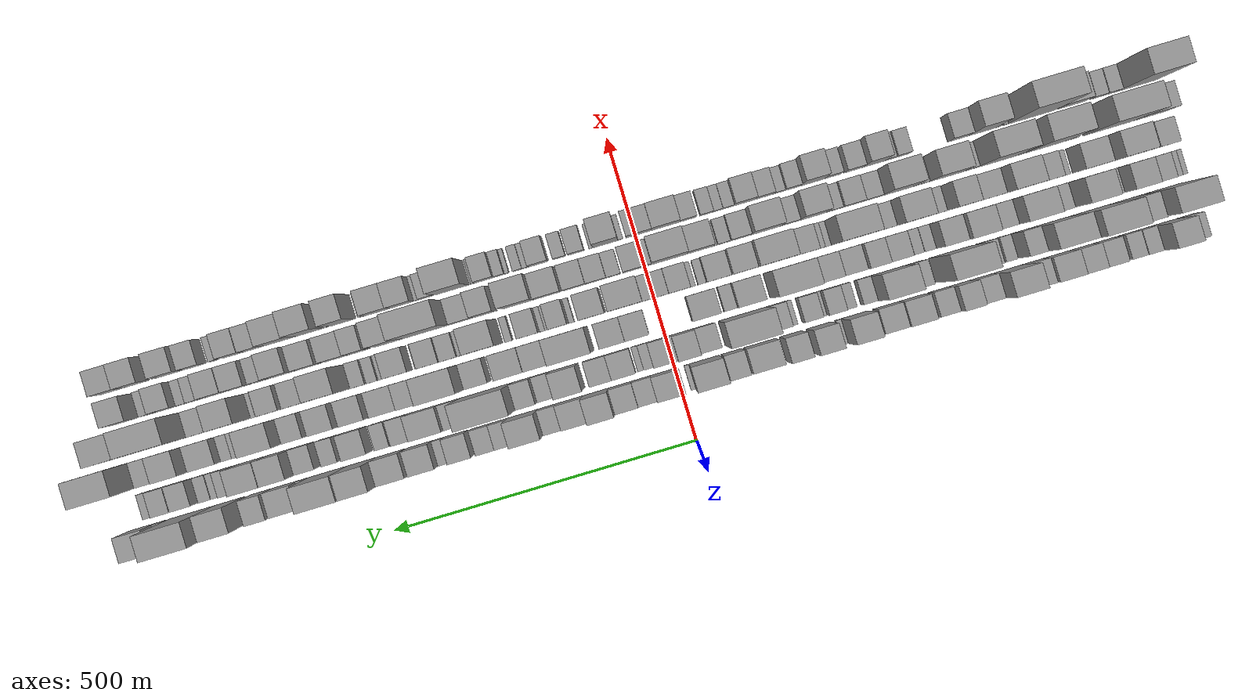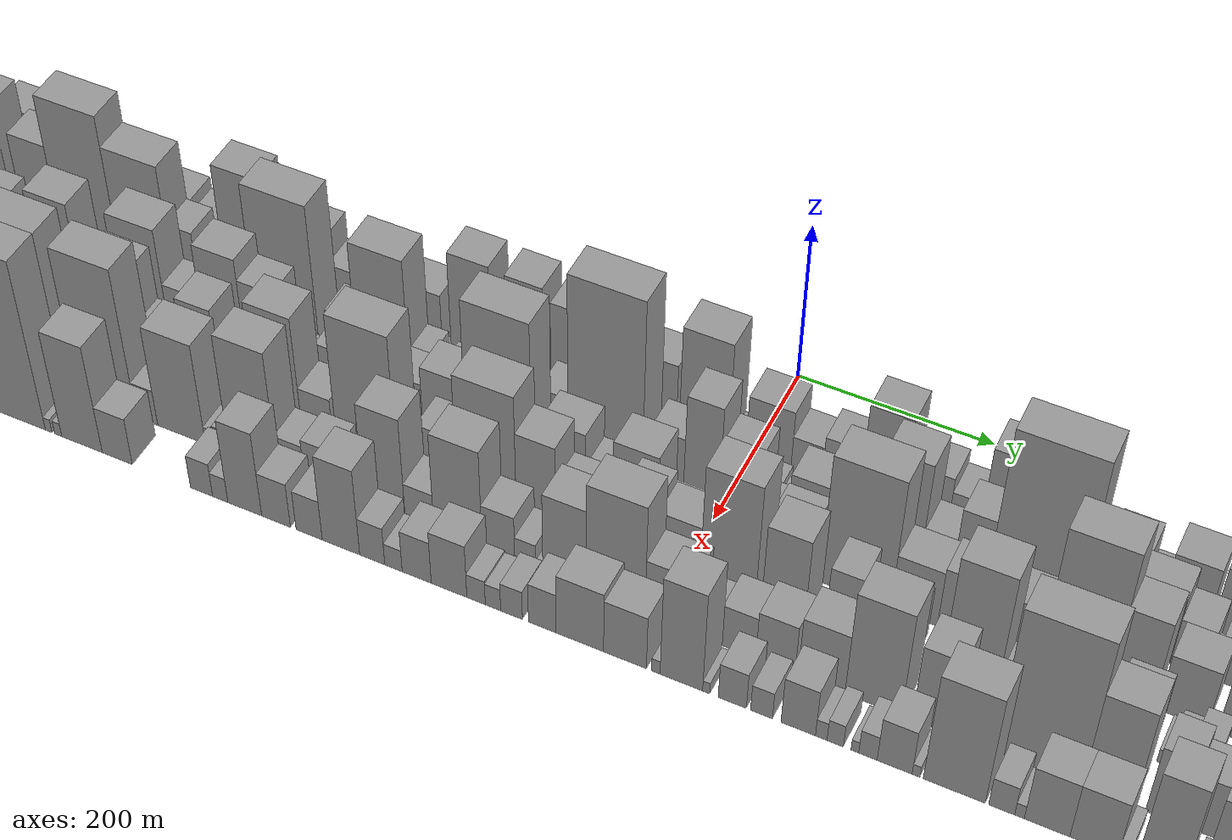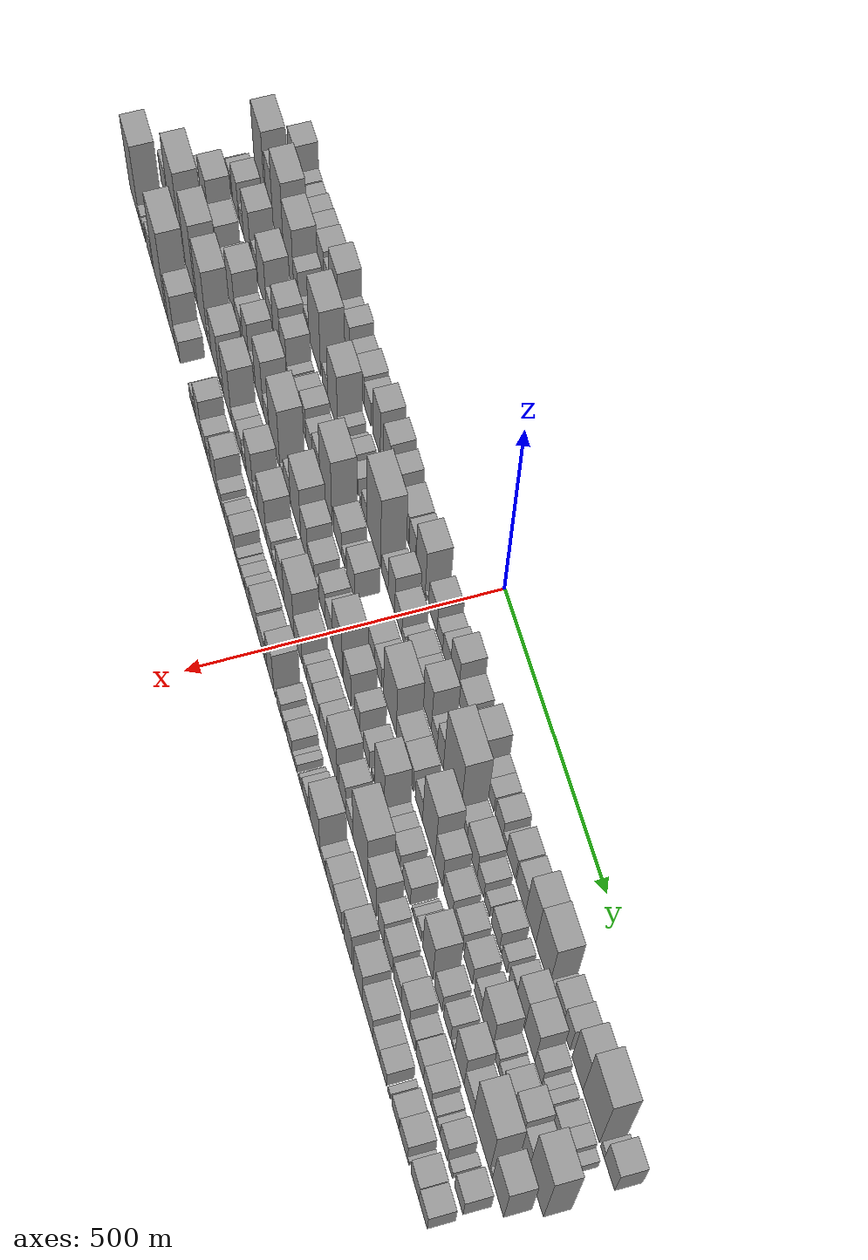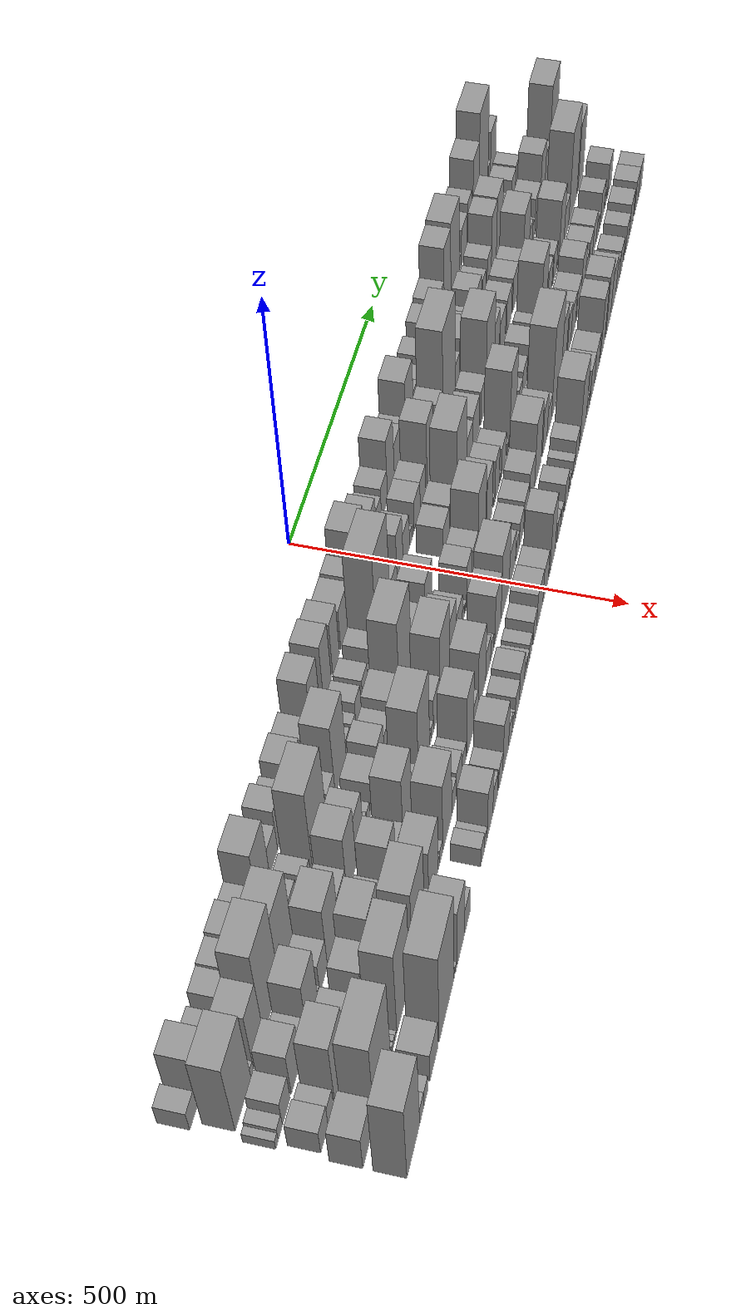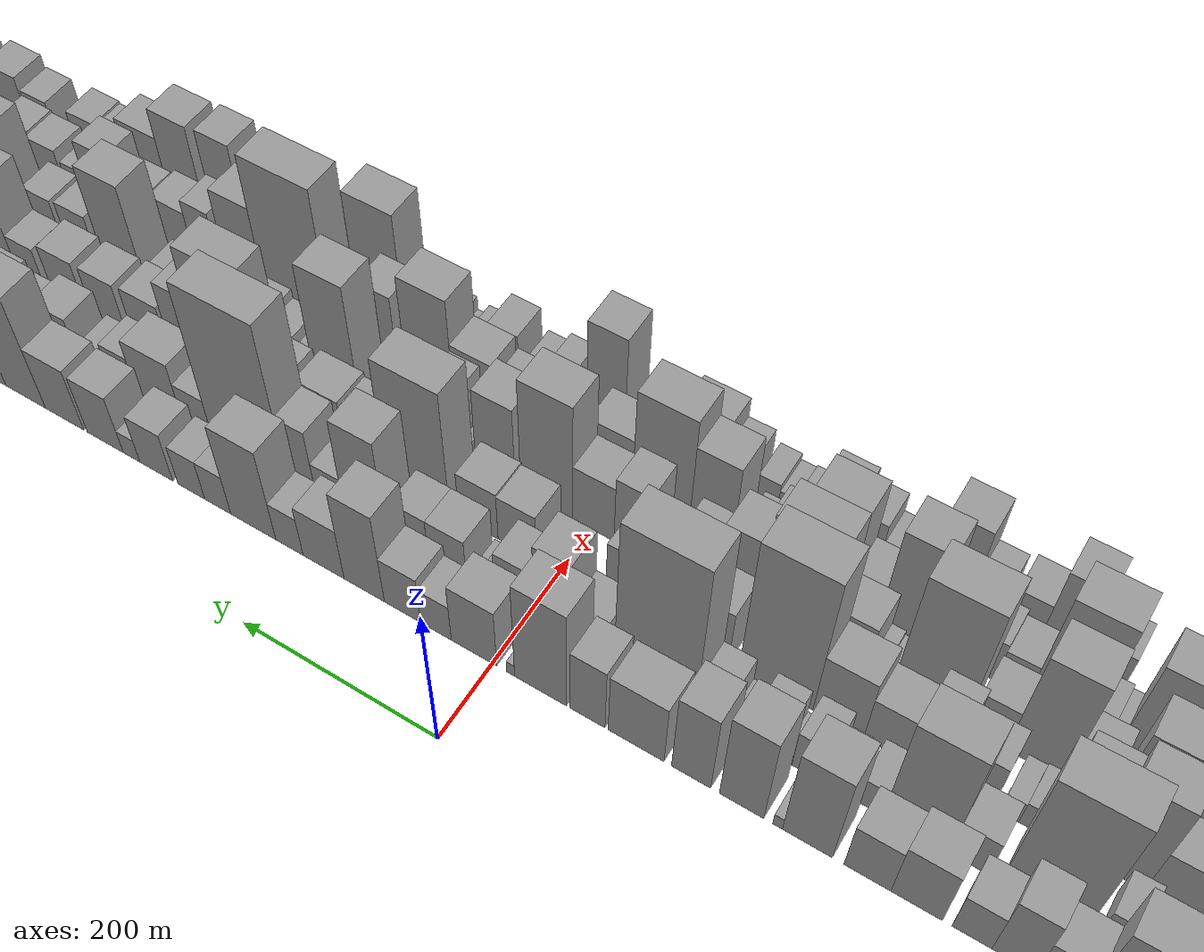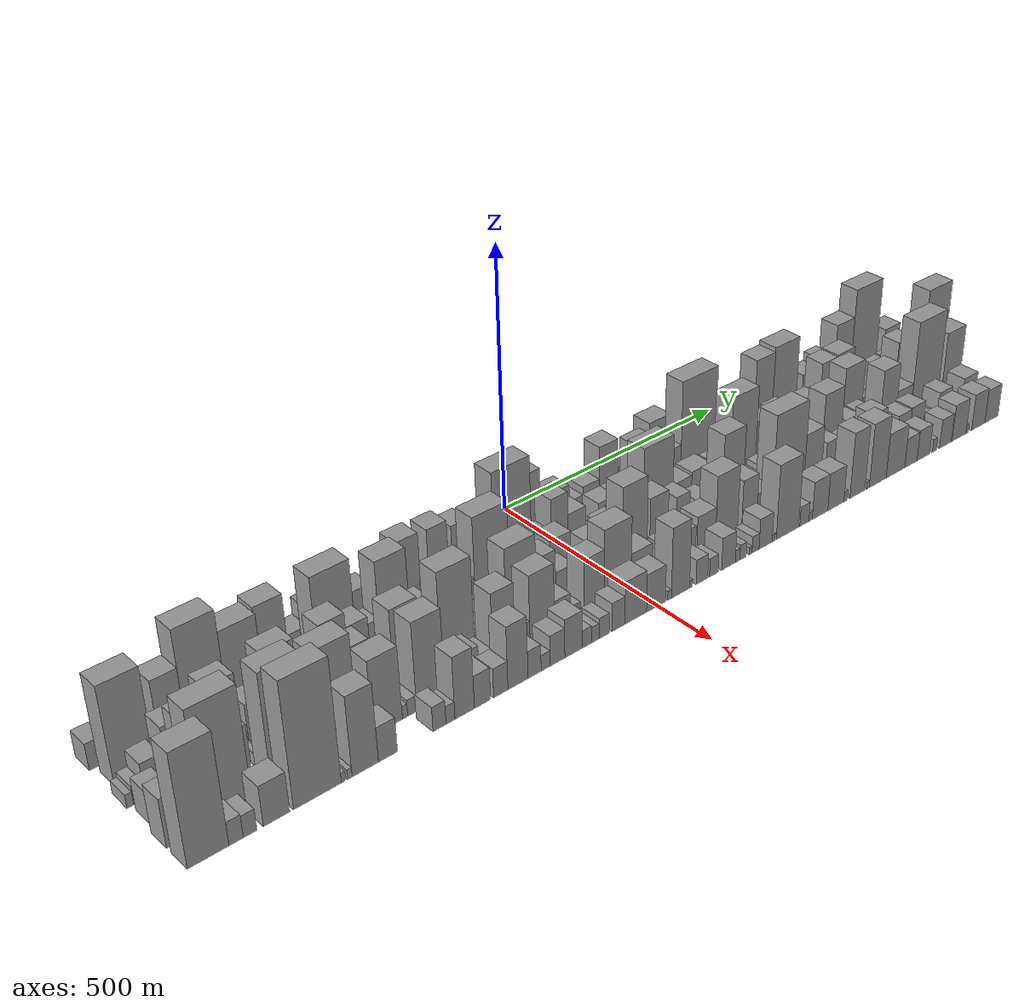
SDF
<sdf version="1.6">
 <world name="default">
  <scene>
   <sky><clouds><speed>12</speed></clouds></sky>
   <ambient>0.4 0.4 0.4 1</ambient>
   <background>0.7 0.7 0.7 1</background>
   <shadows>1</shadows>
  </scene>
  <gravity>0 0 -9.8066</gravity>
  <magnetic_field>6e-06 2.3e-05 -4.2e-05</magnetic_field>
  <physics default="0" name="default_physics" type="ode">
   <ode>
    <solver>
     <type>quick</type>
     <iters>10</iters>
     <sor>1.0</sor>
     <use_dynamic_moi_rescaling>0</use_dynamic_moi_rescaling>
    </solver>
    <constraints>
     <cfm>0</cfm>
     <erp>0.2</erp>
     <contact_max_correcting_vel>100</contact_max_correcting_vel>
     <contact_surface_layer>0.001</contact_surface_layer>
    </constraints>
   </ode>
   <max_step_size>0.004</max_step_size>
   <real_time_factor>1</real_time_factor>
   <real_time_update_rate>250</real_time_update_rate>
  </physics>
  <light name="sun" type="directional">
   <pose>0 0 10 0 0 0</pose>
   <diffuse>0.8 0.8 0.8 1</diffuse>
   <specular>0.2 0.2 0.2 1</specular>
   <attenuation>
    <range>1000</range>
    <constant>0.9</constant>
    <linear>0.01</linear>
    <quadratic>0.001</quadratic>
   </attenuation>
   <direction>-0.5 0.1 -0.9</direction>
  </light>
  <model name="building_1">
   <static>1</static>
   <pose>100.0000 -845.6831 0 0.000000 0.000000 0.000000</pose>
   <link name="link">
    <pose>0 0 24.00 0 0 0</pose>
    <collision name="collision"><geometry><box><size>40.0000 28.6338 48.0000</size></box></geometry></collision>
    <visual name="visual">
     <cast_shadows>0</cast_shadows>
     <geometry><box><size>40.0000 28.6338 48.0000</size></box></geometry>
     <material>
      <script>
       <uri>model://grey_wall/materials/scripts</uri>
       <uri>model://grey_wall/materials/textures</uri>
       <name>vrc/grey_wall</name>
      </script>
     </material>
    </visual>
   </link>
  </model>
  <model name="building_2">
   <static>1</static>
   <pose>100.0000 -804.2069 0 0.000000 0.000000 0.000000</pose>
   <link name="link">
    <pose>0 0 60.00 0 0 0</pose>
    <collision name="collision"><geometry><box><size>40.0000 42.3186 120.0000</size></box></geometry></collision>
    <visual name="visual">
     <cast_shadows>0</cast_shadows>
     <geometry><box><size>40.0000 42.3186 120.0000</size></box></geometry>
     <material>
      <script>
       <uri>model://grey_wall/materials/scripts</uri>
       <uri>model://grey_wall/materials/textures</uri>
       <name>vrc/grey_wall</name>
      </script>
     </material>
    </visual>
   </link>
  </model>
  <model name="building_3">
   <static>1</static>
   <pose>100.0000 -770.7815 0 0.000000 0.000000 0.000000</pose>
   <link name="link">
    <pose>0 0 24.00 0 0 0</pose>
    <collision name="collision"><geometry><box><size>40.0000 24.5322 48.0000</size></box></geometry></collision>
    <visual name="visual">
     <cast_shadows>0</cast_shadows>
     <geometry><box><size>40.0000 24.5322 48.0000</size></box></geometry>
     <material>
      <script>
       <uri>model://grey_wall/materials/scripts</uri>
       <uri>model://grey_wall/materials/textures</uri>
       <name>vrc/grey_wall</name>
      </script>
     </material>
    </visual>
   </link>
  </model>
  <model name="building_4">
   <static>1</static>
   <pose>100.0000 -745.4333 0 0.000000 0.000000 0.000000</pose>
   <link name="link">
    <pose>0 0 22.50 0 0 0</pose>
    <collision name="collision"><geometry><box><size>40.0000 26.1642 45.0000</size></box></geometry></collision>
    <visual name="visual">
     <cast_shadows>0</cast_shadows>
     <geometry><box><size>40.0000 26.1642 45.0000</size></box></geometry>
     <material>
      <script>
       <uri>model://grey_wall/materials/scripts</uri>
       <uri>model://grey_wall/materials/textures</uri>
       <name>vrc/grey_wall</name>
      </script>
     </material>
    </visual>
   </link>
  </model>
  <model name="building_5">
   <static>1</static>
   <pose>100.0000 -726.0575 0 0.000000 0.000000 0.000000</pose>
   <link name="link">
    <pose>0 0 7.50 0 0 0</pose>
    <collision name="collision"><geometry><box><size>40.0000 6.5875 15.0000</size></box></geometry></collision>
    <visual name="visual">
     <cast_shadows>0</cast_shadows>
     <geometry><box><size>40.0000 6.5875 15.0000</size></box></geometry>
     <material>
      <script>
       <uri>model://grey_wall/materials/scripts</uri>
       <uri>model://grey_wall/materials/textures</uri>
       <name>vrc/grey_wall</name>
      </script>
     </material>
    </visual>
   </link>
  </model>
  <model name="building_6">
   <static>1</static>
   <pose>100.0000 -705.3828 0 0.000000 0.000000 0.000000</pose>
   <link name="link">
    <pose>0 0 31.50 0 0 0</pose>
    <collision name="collision"><geometry><box><size>40.0000 34.7618 63.0000</size></box></geometry></collision>
    <visual name="visual">
     <cast_shadows>0</cast_shadows>
     <geometry><box><size>40.0000 34.7618 63.0000</size></box></geometry>
     <material>
      <script>
       <uri>model://grey_wall/materials/scripts</uri>
       <uri>model://grey_wall/materials/textures</uri>
       <name>vrc/grey_wall</name>
      </script>
     </material>
    </visual>
   </link>
  </model>
  <model name="building_7">
   <static>1</static>
   <pose>100.0000 -669.4025 0 0.000000 0.000000 0.000000</pose>
   <link name="link">
    <pose>0 0 34.50 0 0 0</pose>
    <collision name="collision"><geometry><box><size>40.0000 37.1989 69.0000</size></box></geometry></collision>
    <visual name="visual">
     <cast_shadows>0</cast_shadows>
     <geometry><box><size>40.0000 37.1989 69.0000</size></box></geometry>
     <material>
      <script>
       <uri>model://grey_wall/materials/scripts</uri>
       <uri>model://grey_wall/materials/textures</uri>
       <name>vrc/grey_wall</name>
      </script>
     </material>
    </visual>
   </link>
  </model>
  <model name="building_8">
   <static>1</static>
   <pose>100.0000 -628.4915 0 0.000000 0.000000 0.000000</pose>
   <link name="link">
    <pose>0 0 39.00 0 0 0</pose>
    <collision name="collision"><geometry><box><size>40.0000 44.6230 78.0000</size></box></geometry></collision>
    <visual name="visual">
     <cast_shadows>0</cast_shadows>
     <geometry><box><size>40.0000 44.6230 78.0000</size></box></geometry>
     <material>
      <script>
       <uri>model://grey_wall/materials/scripts</uri>
       <uri>model://grey_wall/materials/textures</uri>
       <name>vrc/grey_wall</name>
      </script>
     </material>
    </visual>
   </link>
  </model>
  <model name="building_9">
   <static>1</static>
   <pose>100.0000 -589.9349 0 0.000000 0.000000 0.000000</pose>
   <link name="link">
    <pose>0 0 31.50 0 0 0</pose>
    <collision name="collision"><geometry><box><size>40.0000 32.4903 63.0000</size></box></geometry></collision>
    <visual name="visual">
     <cast_shadows>0</cast_shadows>
     <geometry><box><size>40.0000 32.4903 63.0000</size></box></geometry>
     <material>
      <script>
       <uri>model://grey_wall/materials/scripts</uri>
       <uri>model://grey_wall/materials/textures</uri>
       <name>vrc/grey_wall</name>
      </script>
     </material>
    </visual>
   </link>
  </model>
  <model name="building_10">
   <static>1</static>
   <pose>100.0000 -548.0305 0 0.000000 0.000000 0.000000</pose>
   <link name="link">
    <pose>0 0 70.50 0 0 0</pose>
    <collision name="collision"><geometry><box><size>40.0000 51.3185 141.0000</size></box></geometry></collision>
    <visual name="visual">
     <cast_shadows>0</cast_shadows>
     <geometry><box><size>40.0000 51.3185 141.0000</size></box></geometry>
     <material>
      <script>
       <uri>model://grey_wall/materials/scripts</uri>
       <uri>model://grey_wall/materials/textures</uri>
       <name>vrc/grey_wall</name>
      </script>
     </material>
    </visual>
   </link>
  </model>
  <model name="building_11">
   <static>1</static>
   <pose>100.0000 -503.8620 0 0.000000 0.000000 0.000000</pose>
   <link name="link">
    <pose>0 0 31.50 0 0 0</pose>
    <collision name="collision"><geometry><box><size>40.0000 37.0185 63.0000</size></box></geometry></collision>
    <visual name="visual">
     <cast_shadows>0</cast_shadows>
     <geometry><box><size>40.0000 37.0185 63.0000</size></box></geometry>
     <material>
      <script>
       <uri>model://grey_wall/materials/scripts</uri>
       <uri>model://grey_wall/materials/textures</uri>
       <name>vrc/grey_wall</name>
      </script>
     </material>
    </visual>
   </link>
  </model>
  <model name="building_12">
   <static>1</static>
   <pose>100.0000 -467.8933 0 0.000000 0.000000 0.000000</pose>
   <link name="link">
    <pose>0 0 48.00 0 0 0</pose>
    <collision name="collision"><geometry><box><size>40.0000 34.9190 96.0000</size></box></geometry></collision>
    <visual name="visual">
     <cast_shadows>0</cast_shadows>
     <geometry><box><size>40.0000 34.9190 96.0000</size></box></geometry>
     <material>
      <script>
       <uri>model://grey_wall/materials/scripts</uri>
       <uri>model://grey_wall/materials/textures</uri>
       <name>vrc/grey_wall</name>
      </script>
     </material>
    </visual>
   </link>
  </model>
  <model name="building_13">
   <static>1</static>
   <pose>100.0000 -434.0825 0 0.000000 0.000000 0.000000</pose>
   <link name="link">
    <pose>0 0 30.00 0 0 0</pose>
    <collision name="collision"><geometry><box><size>40.0000 32.7025 60.0000</size></box></geometry></collision>
    <visual name="visual">
     <cast_shadows>0</cast_shadows>
     <geometry><box><size>40.0000 32.7025 60.0000</size></box></geometry>
     <material>
      <script>
       <uri>model://grey_wall/materials/scripts</uri>
       <uri>model://grey_wall/materials/textures</uri>
       <name>vrc/grey_wall</name>
      </script>
     </material>
    </visual>
   </link>
  </model>
  <model name="building_14">
   <static>1</static>
   <pose>100.0000 -388.0605 0 0.000000 0.000000 0.000000</pose>
   <link name="link">
    <pose>0 0 42.00 0 0 0</pose>
    <collision name="collision"><geometry><box><size>40.0000 43.3416 84.0000</size></box></geometry></collision>
    <visual name="visual">
     <cast_shadows>0</cast_shadows>
     <geometry><box><size>40.0000 43.3416 84.0000</size></box></geometry>
     <material>
      <script>
       <uri>model://grey_wall/materials/scripts</uri>
       <uri>model://grey_wall/materials/textures</uri>
       <name>vrc/grey_wall</name>
      </script>
     </material>
    </visual>
   </link>
  </model>
  <model name="building_15">
   <static>1</static>
   <pose>100.0000 -346.2824 0 0.000000 0.000000 0.000000</pose>
   <link name="link">
    <pose>0 0 36.00 0 0 0</pose>
    <collision name="collision"><geometry><box><size>40.0000 40.2146 72.0000</size></box></geometry></collision>
    <visual name="visual">
     <cast_shadows>0</cast_shadows>
     <geometry><box><size>40.0000 40.2146 72.0000</size></box></geometry>
     <material>
      <script>
       <uri>model://grey_wall/materials/scripts</uri>
       <uri>model://grey_wall/materials/textures</uri>
       <name>vrc/grey_wall</name>
      </script>
     </material>
    </visual>
   </link>
  </model>
  <model name="building_16">
   <static>1</static>
   <pose>100.0000 -294.2867 0 0.000000 0.000000 0.000000</pose>
   <link name="link">
    <pose>0 0 67.50 0 0 0</pose>
    <collision name="collision"><geometry><box><size>40.0000 43.7768 135.0000</size></box></geometry></collision>
    <visual name="visual">
     <cast_shadows>0</cast_shadows>
     <geometry><box><size>40.0000 43.7768 135.0000</size></box></geometry>
     <material>
      <script>
       <uri>model://grey_wall/materials/scripts</uri>
       <uri>model://grey_wall/materials/textures</uri>
       <name>vrc/grey_wall</name>
      </script>
     </material>
    </visual>
   </link>
  </model>
  <model name="building_17">
   <static>1</static>
   <pose>100.0000 -268.0724 0 0.000000 0.000000 0.000000</pose>
   <link name="link">
    <pose>0 0 9.00 0 0 0</pose>
    <collision name="collision"><geometry><box><size>40.0000 8.6518 18.0000</size></box></geometry></collision>
    <visual name="visual">
     <cast_shadows>0</cast_shadows>
     <geometry><box><size>40.0000 8.6518 18.0000</size></box></geometry>
     <material>
      <script>
       <uri>model://grey_wall/materials/scripts</uri>
       <uri>model://grey_wall/materials/textures</uri>
       <name>vrc/grey_wall</name>
      </script>
     </material>
    </visual>
   </link>
  </model>
  <model name="building_18">
   <static>1</static>
   <pose>100.0000 -235.8010 0 0.000000 0.000000 0.000000</pose>
   <link name="link">
    <pose>0 0 66.00 0 0 0</pose>
    <collision name="collision"><geometry><box><size>40.0000 39.8909 132.0000</size></box></geometry></collision>
    <visual name="visual">
     <cast_shadows>0</cast_shadows>
     <geometry><box><size>40.0000 39.8909 132.0000</size></box></geometry>
     <material>
      <script>
       <uri>model://grey_wall/materials/scripts</uri>
       <uri>model://grey_wall/materials/textures</uri>
       <name>vrc/grey_wall</name>
      </script>
     </material>
    </visual>
   </link>
  </model>
  <model name="building_19">
   <static>1</static>
   <pose>100.0000 -189.8617 0 0.000000 0.000000 0.000000</pose>
   <link name="link">
    <pose>0 0 58.50 0 0 0</pose>
    <collision name="collision"><geometry><box><size>40.0000 35.9877 117.0000</size></box></geometry></collision>
    <visual name="visual">
     <cast_shadows>0</cast_shadows>
     <geometry><box><size>40.0000 35.9877 117.0000</size></box></geometry>
     <material>
      <script>
       <uri>model://grey_wall/materials/scripts</uri>
       <uri>model://grey_wall/materials/textures</uri>
       <name>vrc/grey_wall</name>
      </script>
     </material>
    </visual>
   </link>
  </model>
  <model name="building_20">
   <static>1</static>
   <pose>100.0000 -138.5964 0 0.000000 0.000000 0.000000</pose>
   <link name="link">
    <pose>0 0 45.00 0 0 0</pose>
    <collision name="collision"><geometry><box><size>40.0000 52.5428 90.0000</size></box></geometry></collision>
    <visual name="visual">
     <cast_shadows>0</cast_shadows>
     <geometry><box><size>40.0000 52.5428 90.0000</size></box></geometry>
     <material>
      <script>
       <uri>model://grey_wall/materials/scripts</uri>
       <uri>model://grey_wall/materials/textures</uri>
       <name>vrc/grey_wall</name>
      </script>
     </material>
    </visual>
   </link>
  </model>
  <model name="building_21">
   <static>1</static>
   <pose>100.0000 -92.4272 0 0.000000 0.000000 0.000000</pose>
   <link name="link">
    <pose>0 0 46.50 0 0 0</pose>
    <collision name="collision"><geometry><box><size>40.0000 33.7957 93.0000</size></box></geometry></collision>
    <visual name="visual">
     <cast_shadows>0</cast_shadows>
     <geometry><box><size>40.0000 33.7957 93.0000</size></box></geometry>
     <material>
      <script>
       <uri>model://grey_wall/materials/scripts</uri>
       <uri>model://grey_wall/materials/textures</uri>
       <name>vrc/grey_wall</name>
      </script>
     </material>
    </visual>
   </link>
  </model>
  <model name="building_22">
   <static>1</static>
   <pose>100.0000 -47.0953 0 0.000000 0.000000 0.000000</pose>
   <link name="link">
    <pose>0 0 73.50 0 0 0</pose>
    <collision name="collision"><geometry><box><size>40.0000 50.8680 147.0000</size></box></geometry></collision>
    <visual name="visual">
     <cast_shadows>0</cast_shadows>
     <geometry><box><size>40.0000 50.8680 147.0000</size></box></geometry>
     <material>
      <script>
       <uri>model://grey_wall/materials/scripts</uri>
       <uri>model://grey_wall/materials/textures</uri>
       <name>vrc/grey_wall</name>
      </script>
     </material>
    </visual>
   </link>
  </model>
  <model name="building_23">
   <static>1</static>
   <pose>100.0000 -17.7952 0 0.000000 0.000000 0.000000</pose>
   <link name="link">
    <pose>0 0 9.00 0 0 0</pose>
    <collision name="collision"><geometry><box><size>40.0000 7.7321 18.0000</size></box></geometry></collision>
    <visual name="visual">
     <cast_shadows>0</cast_shadows>
     <geometry><box><size>40.0000 7.7321 18.0000</size></box></geometry>
     <material>
      <script>
       <uri>model://grey_wall/materials/scripts</uri>
       <uri>model://grey_wall/materials/textures</uri>
       <name>vrc/grey_wall</name>
      </script>
     </material>
    </visual>
   </link>
  </model>
  <model name="building_24">
   <static>1</static>
   <pose>100.0000 18.9389 0 0.000000 0.000000 0.000000</pose>
   <link name="link">
    <pose>0 0 43.50 0 0 0</pose>
    <collision name="collision"><geometry><box><size>40.0000 45.7362 87.0000</size></box></geometry></collision>
    <visual name="visual">
     <cast_shadows>0</cast_shadows>
     <geometry><box><size>40.0000 45.7362 87.0000</size></box></geometry>
     <material>
      <script>
       <uri>model://grey_wall/materials/scripts</uri>
       <uri>model://grey_wall/materials/textures</uri>
       <name>vrc/grey_wall</name>
      </script>
     </material>
    </visual>
   </link>
  </model>
  <model name="building_25">
   <static>1</static>
   <pose>100.0000 57.3838 0 0.000000 0.000000 0.000000</pose>
   <link name="link">
    <pose>0 0 27.00 0 0 0</pose>
    <collision name="collision"><geometry><box><size>40.0000 31.1536 54.0000</size></box></geometry></collision>
    <visual name="visual">
     <cast_shadows>0</cast_shadows>
     <geometry><box><size>40.0000 31.1536 54.0000</size></box></geometry>
     <material>
      <script>
       <uri>model://grey_wall/materials/scripts</uri>
       <uri>model://grey_wall/materials/textures</uri>
       <name>vrc/grey_wall</name>
      </script>
     </material>
    </visual>
   </link>
  </model>
  <model name="building_26">
   <static>1</static>
   <pose>100.0000 91.8761 0 0.000000 0.000000 0.000000</pose>
   <link name="link">
    <pose>0 0 34.50 0 0 0</pose>
    <collision name="collision"><geometry><box><size>40.0000 37.8310 69.0000</size></box></geometry></collision>
    <visual name="visual">
     <cast_shadows>0</cast_shadows>
     <geometry><box><size>40.0000 37.8310 69.0000</size></box></geometry>
     <material>
      <script>
       <uri>model://grey_wall/materials/scripts</uri>
       <uri>model://grey_wall/materials/textures</uri>
       <name>vrc/grey_wall</name>
      </script>
     </material>
    </visual>
   </link>
  </model>
  <model name="building_27">
   <static>1</static>
   <pose>100.0000 132.1035 0 0.000000 0.000000 0.000000</pose>
   <link name="link">
    <pose>0 0 66.00 0 0 0</pose>
    <collision name="collision"><geometry><box><size>40.0000 42.6239 132.0000</size></box></geometry></collision>
    <visual name="visual">
     <cast_shadows>0</cast_shadows>
     <geometry><box><size>40.0000 42.6239 132.0000</size></box></geometry>
     <material>
      <script>
       <uri>model://grey_wall/materials/scripts</uri>
       <uri>model://grey_wall/materials/textures</uri>
       <name>vrc/grey_wall</name>
      </script>
     </material>
    </visual>
   </link>
  </model>
  <model name="building_28">
   <static>1</static>
   <pose>100.0000 175.4105 0 0.000000 0.000000 0.000000</pose>
   <link name="link">
    <pose>0 0 37.50 0 0 0</pose>
    <collision name="collision"><geometry><box><size>40.0000 43.9900 75.0000</size></box></geometry></collision>
    <visual name="visual">
     <cast_shadows>0</cast_shadows>
     <geometry><box><size>40.0000 43.9900 75.0000</size></box></geometry>
     <material>
      <script>
       <uri>model://grey_wall/materials/scripts</uri>
       <uri>model://grey_wall/materials/textures</uri>
       <name>vrc/grey_wall</name>
      </script>
     </material>
    </visual>
   </link>
  </model>
  <model name="building_29">
   <static>1</static>
   <pose>100.0000 212.3059 0 0.000000 0.000000 0.000000</pose>
   <link name="link">
    <pose>0 0 28.50 0 0 0</pose>
    <collision name="collision"><geometry><box><size>40.0000 29.8007 57.0000</size></box></geometry></collision>
    <visual name="visual">
     <cast_shadows>0</cast_shadows>
     <geometry><box><size>40.0000 29.8007 57.0000</size></box></geometry>
     <material>
      <script>
       <uri>model://grey_wall/materials/scripts</uri>
       <uri>model://grey_wall/materials/textures</uri>
       <name>vrc/grey_wall</name>
      </script>
     </material>
    </visual>
   </link>
  </model>
  <model name="building_30">
   <static>1</static>
   <pose>100.0000 252.1668 0 0.000000 0.000000 0.000000</pose>
   <link name="link">
    <pose>0 0 66.00 0 0 0</pose>
    <collision name="collision"><geometry><box><size>40.0000 49.9213 132.0000</size></box></geometry></collision>
    <visual name="visual">
     <cast_shadows>0</cast_shadows>
     <geometry><box><size>40.0000 49.9213 132.0000</size></box></geometry>
     <material>
      <script>
       <uri>model://grey_wall/materials/scripts</uri>
       <uri>model://grey_wall/materials/textures</uri>
       <name>vrc/grey_wall</name>
      </script>
     </material>
    </visual>
   </link>
  </model>
  <model name="building_31">
   <static>1</static>
   <pose>100.0000 291.7930 0 0.000000 0.000000 0.000000</pose>
   <link name="link">
    <pose>0 0 28.50 0 0 0</pose>
    <collision name="collision"><geometry><box><size>40.0000 29.3309 57.0000</size></box></geometry></collision>
    <visual name="visual">
     <cast_shadows>0</cast_shadows>
     <geometry><box><size>40.0000 29.3309 57.0000</size></box></geometry>
     <material>
      <script>
       <uri>model://grey_wall/materials/scripts</uri>
       <uri>model://grey_wall/materials/textures</uri>
       <name>vrc/grey_wall</name>
      </script>
     </material>
    </visual>
   </link>
  </model>
  <model name="building_32">
   <static>1</static>
   <pose>100.0000 321.7604 0 0.000000 0.000000 0.000000</pose>
   <link name="link">
    <pose>0 0 28.50 0 0 0</pose>
    <collision name="collision"><geometry><box><size>40.0000 30.6040 57.0000</size></box></geometry></collision>
    <visual name="visual">
     <cast_shadows>0</cast_shadows>
     <geometry><box><size>40.0000 30.6040 57.0000</size></box></geometry>
     <material>
      <script>
       <uri>model://grey_wall/materials/scripts</uri>
       <uri>model://grey_wall/materials/textures</uri>
       <name>vrc/grey_wall</name>
      </script>
     </material>
    </visual>
   </link>
  </model>
  <model name="building_33">
   <static>1</static>
   <pose>100.0000 362.1022 0 0.000000 0.000000 0.000000</pose>
   <link name="link">
    <pose>0 0 34.50 0 0 0</pose>
    <collision name="collision"><geometry><box><size>40.0000 38.0797 69.0000</size></box></geometry></collision>
    <visual name="visual">
     <cast_shadows>0</cast_shadows>
     <geometry><box><size>40.0000 38.0797 69.0000</size></box></geometry>
     <material>
      <script>
       <uri>model://grey_wall/materials/scripts</uri>
       <uri>model://grey_wall/materials/textures</uri>
       <name>vrc/grey_wall</name>
      </script>
     </material>
    </visual>
   </link>
  </model>
  <model name="building_34">
   <static>1</static>
   <pose>100.0000 390.8431 0 0.000000 0.000000 0.000000</pose>
   <link name="link">
    <pose>0 0 16.50 0 0 0</pose>
    <collision name="collision"><geometry><box><size>40.0000 19.4021 33.0000</size></box></geometry></collision>
    <visual name="visual">
     <cast_shadows>0</cast_shadows>
     <geometry><box><size>40.0000 19.4021 33.0000</size></box></geometry>
     <material>
      <script>
       <uri>model://grey_wall/materials/scripts</uri>
       <uri>model://grey_wall/materials/textures</uri>
       <name>vrc/grey_wall</name>
      </script>
     </material>
    </visual>
   </link>
  </model>
  <model name="building_35">
   <static>1</static>
   <pose>100.0000 422.0208 0 0.000000 0.000000 0.000000</pose>
   <link name="link">
    <pose>0 0 40.50 0 0 0</pose>
    <collision name="collision"><geometry><box><size>40.0000 42.9532 81.0000</size></box></geometry></collision>
    <visual name="visual">
     <cast_shadows>0</cast_shadows>
     <geometry><box><size>40.0000 42.9532 81.0000</size></box></geometry>
     <material>
      <script>
       <uri>model://grey_wall/materials/scripts</uri>
       <uri>model://grey_wall/materials/textures</uri>
       <name>vrc/grey_wall</name>
      </script>
     </material>
    </visual>
   </link>
  </model>
  <model name="building_36">
   <static>1</static>
   <pose>100.0000 470.6741 0 0.000000 0.000000 0.000000</pose>
   <link name="link">
    <pose>0 0 43.50 0 0 0</pose>
    <collision name="collision"><geometry><box><size>40.0000 46.3534 87.0000</size></box></geometry></collision>
    <visual name="visual">
     <cast_shadows>0</cast_shadows>
     <geometry><box><size>40.0000 46.3534 87.0000</size></box></geometry>
     <material>
      <script>
       <uri>model://grey_wall/materials/scripts</uri>
       <uri>model://grey_wall/materials/textures</uri>
       <name>vrc/grey_wall</name>
      </script>
     </material>
    </visual>
   </link>
  </model>
  <model name="building_37">
   <static>1</static>
   <pose>100.0000 518.1306 0 0.000000 0.000000 0.000000</pose>
   <link name="link">
    <pose>0 0 78.00 0 0 0</pose>
    <collision name="collision"><geometry><box><size>40.0000 48.5595 156.0000</size></box></geometry></collision>
    <visual name="visual">
     <cast_shadows>0</cast_shadows>
     <geometry><box><size>40.0000 48.5595 156.0000</size></box></geometry>
     <material>
      <script>
       <uri>model://grey_wall/materials/scripts</uri>
       <uri>model://grey_wall/materials/textures</uri>
       <name>vrc/grey_wall</name>
      </script>
     </material>
    </visual>
   </link>
  </model>
  <model name="building_38">
   <static>1</static>
   <pose>100.0000 574.7804 0 0.000000 0.000000 0.000000</pose>
   <link name="link">
    <pose>0 0 82.50 0 0 0</pose>
    <collision name="collision"><geometry><box><size>40.0000 64.7402 165.0000</size></box></geometry></collision>
    <visual name="visual">
     <cast_shadows>0</cast_shadows>
     <geometry><box><size>40.0000 64.7402 165.0000</size></box></geometry>
     <material>
      <script>
       <uri>model://grey_wall/materials/scripts</uri>
       <uri>model://grey_wall/materials/textures</uri>
       <name>vrc/grey_wall</name>
      </script>
     </material>
    </visual>
   </link>
  </model>
  <model name="building_39">
   <static>1</static>
   <pose>100.0000 615.2542 0 0.000000 0.000000 0.000000</pose>
   <link name="link">
    <pose>0 0 15.00 0 0 0</pose>
    <collision name="collision"><geometry><box><size>40.0000 16.2075 30.0000</size></box></geometry></collision>
    <visual name="visual">
     <cast_shadows>0</cast_shadows>
     <geometry><box><size>40.0000 16.2075 30.0000</size></box></geometry>
     <material>
      <script>
       <uri>model://grey_wall/materials/scripts</uri>
       <uri>model://grey_wall/materials/textures</uri>
       <name>vrc/grey_wall</name>
      </script>
     </material>
    </visual>
   </link>
  </model>
  <model name="building_40">
   <static>1</static>
   <pose>100.0000 645.7013 0 0.000000 0.000000 0.000000</pose>
   <link name="link">
    <pose>0 0 39.00 0 0 0</pose>
    <collision name="collision"><geometry><box><size>40.0000 44.6866 78.0000</size></box></geometry></collision>
    <visual name="visual">
     <cast_shadows>0</cast_shadows>
     <geometry><box><size>40.0000 44.6866 78.0000</size></box></geometry>
     <material>
      <script>
       <uri>model://grey_wall/materials/scripts</uri>
       <uri>model://grey_wall/materials/textures</uri>
       <name>vrc/grey_wall</name>
      </script>
     </material>
    </visual>
   </link>
  </model>
  <model name="building_41">
   <static>1</static>
   <pose>100.0000 685.2776 0 0.000000 0.000000 0.000000</pose>
   <link name="link">
    <pose>0 0 48.00 0 0 0</pose>
    <collision name="collision"><geometry><box><size>40.0000 34.4660 96.0000</size></box></geometry></collision>
    <visual name="visual">
     <cast_shadows>0</cast_shadows>
     <geometry><box><size>40.0000 34.4660 96.0000</size></box></geometry>
     <material>
      <script>
       <uri>model://grey_wall/materials/scripts</uri>
       <uri>model://grey_wall/materials/textures</uri>
       <name>vrc/grey_wall</name>
      </script>
     </material>
    </visual>
   </link>
  </model>
  <model name="building_42">
   <static>1</static>
   <pose>100.0000 737.0859 0 0.000000 0.000000 0.000000</pose>
   <link name="link">
    <pose>0 0 75.00 0 0 0</pose>
    <collision name="collision"><geometry><box><size>40.0000 49.1505 150.0000</size></box></geometry></collision>
    <visual name="visual">
     <cast_shadows>0</cast_shadows>
     <geometry><box><size>40.0000 49.1505 150.0000</size></box></geometry>
     <material>
      <script>
       <uri>model://grey_wall/materials/scripts</uri>
       <uri>model://grey_wall/materials/textures</uri>
       <name>vrc/grey_wall</name>
      </script>
     </material>
    </visual>
   </link>
  </model>
  <model name="building_43">
   <static>1</static>
   <pose>100.0000 799.0678 0 0.000000 0.000000 0.000000</pose>
   <link name="link">
    <pose>0 0 103.50 0 0 0</pose>
    <collision name="collision"><geometry><box><size>40.0000 74.8134 207.0000</size></box></geometry></collision>
    <visual name="visual">
     <cast_shadows>0</cast_shadows>
     <geometry><box><size>40.0000 74.8134 207.0000</size></box></geometry>
     <material>
      <script>
       <uri>model://grey_wall/materials/scripts</uri>
       <uri>model://grey_wall/materials/textures</uri>
       <name>vrc/grey_wall</name>
      </script>
     </material>
    </visual>
   </link>
  </model>
  <model name="building_44">
   <static>1</static>
   <pose>100.0000 849.8463 0 0.000000 0.000000 0.000000</pose>
   <link name="link">
    <pose>0 0 15.00 0 0 0</pose>
    <collision name="collision"><geometry><box><size>40.0000 16.7435 30.0000</size></box></geometry></collision>
    <visual name="visual">
     <cast_shadows>0</cast_shadows>
     <geometry><box><size>40.0000 16.7435 30.0000</size></box></geometry>
     <material>
      <script>
       <uri>model://grey_wall/materials/scripts</uri>
       <uri>model://grey_wall/materials/textures</uri>
       <name>vrc/grey_wall</name>
      </script>
     </material>
    </visual>
   </link>
  </model>
  <model name="building_45">
   <static>1</static>
   <pose>100.0000 881.0753 0 0.000000 0.000000 0.000000</pose>
   <link name="link">
    <pose>0 0 45.00 0 0 0</pose>
    <collision name="collision"><geometry><box><size>40.0000 45.7145 90.0000</size></box></geometry></collision>
    <visual name="visual">
     <cast_shadows>0</cast_shadows>
     <geometry><box><size>40.0000 45.7145 90.0000</size></box></geometry>
     <material>
      <script>
       <uri>model://grey_wall/materials/scripts</uri>
       <uri>model://grey_wall/materials/textures</uri>
       <name>vrc/grey_wall</name>
      </script>
     </material>
    </visual>
   </link>
  </model>
  <model name="building_46">
   <static>1</static>
   <pose>152.0000 -817.2317 0 0.000000 0.000000 0.000000</pose>
   <link name="link">
    <pose>0 0 88.50 0 0 0</pose>
    <collision name="collision"><geometry><box><size>40.0000 65.5365 177.0000</size></box></geometry></collision>
    <visual name="visual">
     <cast_shadows>0</cast_shadows>
     <geometry><box><size>40.0000 65.5365 177.0000</size></box></geometry>
     <material>
      <script>
       <uri>model://grey_wall/materials/scripts</uri>
       <uri>model://grey_wall/materials/textures</uri>
       <name>vrc/grey_wall</name>
      </script>
     </material>
    </visual>
   </link>
  </model>
  <model name="building_47">
   <static>1</static>
   <pose>152.0000 -778.7980 0 0.000000 0.000000 0.000000</pose>
   <link name="link">
    <pose>0 0 12.00 0 0 0</pose>
    <collision name="collision"><geometry><box><size>40.0000 11.3308 24.0000</size></box></geometry></collision>
    <visual name="visual">
     <cast_shadows>0</cast_shadows>
     <geometry><box><size>40.0000 11.3308 24.0000</size></box></geometry>
     <material>
      <script>
       <uri>model://grey_wall/materials/scripts</uri>
       <uri>model://grey_wall/materials/textures</uri>
       <name>vrc/grey_wall</name>
      </script>
     </material>
    </visual>
   </link>
  </model>
  <model name="building_48">
   <static>1</static>
   <pose>152.0000 -751.4504 0 0.000000 0.000000 0.000000</pose>
   <link name="link">
    <pose>0 0 72.00 0 0 0</pose>
    <collision name="collision"><geometry><box><size>40.0000 43.3644 144.0000</size></box></geometry></collision>
    <visual name="visual">
     <cast_shadows>0</cast_shadows>
     <geometry><box><size>40.0000 43.3644 144.0000</size></box></geometry>
     <material>
      <script>
       <uri>model://grey_wall/materials/scripts</uri>
       <uri>model://grey_wall/materials/textures</uri>
       <name>vrc/grey_wall</name>
      </script>
     </material>
    </visual>
   </link>
  </model>
  <model name="building_49">
   <static>1</static>
   <pose>152.0000 -695.3066 0 0.000000 0.000000 0.000000</pose>
   <link name="link">
    <pose>0 0 105.00 0 0 0</pose>
    <collision name="collision"><geometry><box><size>40.0000 68.9232 210.0000</size></box></geometry></collision>
    <visual name="visual">
     <cast_shadows>0</cast_shadows>
     <geometry><box><size>40.0000 68.9232 210.0000</size></box></geometry>
     <material>
      <script>
       <uri>model://grey_wall/materials/scripts</uri>
       <uri>model://grey_wall/materials/textures</uri>
       <name>vrc/grey_wall</name>
      </script>
     </material>
    </visual>
   </link>
  </model>
  <model name="building_50">
   <static>1</static>
   <pose>152.0000 -629.6863 0 0.000000 0.000000 0.000000</pose>
   <link name="link">
    <pose>0 0 85.50 0 0 0</pose>
    <collision name="collision"><geometry><box><size>40.0000 62.3173 171.0000</size></box></geometry></collision>
    <visual name="visual">
     <cast_shadows>0</cast_shadows>
     <geometry><box><size>40.0000 62.3173 171.0000</size></box></geometry>
     <material>
      <script>
       <uri>model://grey_wall/materials/scripts</uri>
       <uri>model://grey_wall/materials/textures</uri>
       <name>vrc/grey_wall</name>
      </script>
     </material>
    </visual>
   </link>
  </model>
  <model name="building_51">
   <static>1</static>
   <pose>152.0000 -583.8461 0 0.000000 0.000000 0.000000</pose>
   <link name="link">
    <pose>0 0 48.00 0 0 0</pose>
    <collision name="collision"><geometry><box><size>40.0000 29.3632 96.0000</size></box></geometry></collision>
    <visual name="visual">
     <cast_shadows>0</cast_shadows>
     <geometry><box><size>40.0000 29.3632 96.0000</size></box></geometry>
     <material>
      <script>
       <uri>model://grey_wall/materials/scripts</uri>
       <uri>model://grey_wall/materials/textures</uri>
       <name>vrc/grey_wall</name>
      </script>
     </material>
    </visual>
   </link>
  </model>
  <model name="building_52">
   <static>1</static>
   <pose>152.0000 -554.6557 0 0.000000 0.000000 0.000000</pose>
   <link name="link">
    <pose>0 0 16.50 0 0 0</pose>
    <collision name="collision"><geometry><box><size>40.0000 19.0176 33.0000</size></box></geometry></collision>
    <visual name="visual">
     <cast_shadows>0</cast_shadows>
     <geometry><box><size>40.0000 19.0176 33.0000</size></box></geometry>
     <material>
      <script>
       <uri>model://grey_wall/materials/scripts</uri>
       <uri>model://grey_wall/materials/textures</uri>
       <name>vrc/grey_wall</name>
      </script>
     </material>
    </visual>
   </link>
  </model>
  <model name="building_53">
   <static>1</static>
   <pose>152.0000 -526.5399 0 0.000000 0.000000 0.000000</pose>
   <link name="link">
    <pose>0 0 24.00 0 0 0</pose>
    <collision name="collision"><geometry><box><size>40.0000 25.2141 48.0000</size></box></geometry></collision>
    <visual name="visual">
     <cast_shadows>0</cast_shadows>
     <geometry><box><size>40.0000 25.2141 48.0000</size></box></geometry>
     <material>
      <script>
       <uri>model://grey_wall/materials/scripts</uri>
       <uri>model://grey_wall/materials/textures</uri>
       <name>vrc/grey_wall</name>
      </script>
     </material>
    </visual>
   </link>
  </model>
  <model name="building_54">
   <static>1</static>
   <pose>152.0000 -469.6547 0 0.000000 0.000000 0.000000</pose>
   <link name="link">
    <pose>0 0 94.50 0 0 0</pose>
    <collision name="collision"><geometry><box><size>40.0000 70.5563 189.0000</size></box></geometry></collision>
    <visual name="visual">
     <cast_shadows>0</cast_shadows>
     <geometry><box><size>40.0000 70.5563 189.0000</size></box></geometry>
     <material>
      <script>
       <uri>model://grey_wall/materials/scripts</uri>
       <uri>model://grey_wall/materials/textures</uri>
       <name>vrc/grey_wall</name>
      </script>
     </material>
    </visual>
   </link>
  </model>
  <model name="building_55">
   <static>1</static>
   <pose>152.0000 -407.8791 0 0.000000 0.000000 0.000000</pose>
   <link name="link">
    <pose>0 0 28.50 0 0 0</pose>
    <collision name="collision"><geometry><box><size>40.0000 32.9948 57.0000</size></box></geometry></collision>
    <visual name="visual">
     <cast_shadows>0</cast_shadows>
     <geometry><box><size>40.0000 32.9948 57.0000</size></box></geometry>
     <material>
      <script>
       <uri>model://grey_wall/materials/scripts</uri>
       <uri>model://grey_wall/materials/textures</uri>
       <name>vrc/grey_wall</name>
      </script>
     </material>
    </visual>
   </link>
  </model>
  <model name="building_56">
   <static>1</static>
   <pose>152.0000 -362.6315 0 0.000000 0.000000 0.000000</pose>
   <link name="link">
    <pose>0 0 81.00 0 0 0</pose>
    <collision name="collision"><geometry><box><size>40.0000 57.5003 162.0000</size></box></geometry></collision>
    <visual name="visual">
     <cast_shadows>0</cast_shadows>
     <geometry><box><size>40.0000 57.5003 162.0000</size></box></geometry>
     <material>
      <script>
       <uri>model://grey_wall/materials/scripts</uri>
       <uri>model://grey_wall/materials/textures</uri>
       <name>vrc/grey_wall</name>
      </script>
     </material>
    </visual>
   </link>
  </model>
  <model name="building_57">
   <static>1</static>
   <pose>152.0000 -322.2955 0 0.000000 0.000000 0.000000</pose>
   <link name="link">
    <pose>0 0 21.00 0 0 0</pose>
    <collision name="collision"><geometry><box><size>40.0000 23.1716 42.0000</size></box></geometry></collision>
    <visual name="visual">
     <cast_shadows>0</cast_shadows>
     <geometry><box><size>40.0000 23.1716 42.0000</size></box></geometry>
     <material>
      <script>
       <uri>model://grey_wall/materials/scripts</uri>
       <uri>model://grey_wall/materials/textures</uri>
       <name>vrc/grey_wall</name>
      </script>
     </material>
    </visual>
   </link>
  </model>
  <model name="building_58">
   <static>1</static>
   <pose>152.0000 -291.6511 0 0.000000 0.000000 0.000000</pose>
   <link name="link">
    <pose>0 0 16.50 0 0 0</pose>
    <collision name="collision"><geometry><box><size>40.0000 18.1173 33.0000</size></box></geometry></collision>
    <visual name="visual">
     <cast_shadows>0</cast_shadows>
     <geometry><box><size>40.0000 18.1173 33.0000</size></box></geometry>
     <material>
      <script>
       <uri>model://grey_wall/materials/scripts</uri>
       <uri>model://grey_wall/materials/textures</uri>
       <name>vrc/grey_wall</name>
      </script>
     </material>
    </visual>
   </link>
  </model>
  <model name="building_59">
   <static>1</static>
   <pose>152.0000 -267.8177 0 0.000000 0.000000 0.000000</pose>
   <link name="link">
    <pose>0 0 28.50 0 0 0</pose>
    <collision name="collision"><geometry><box><size>40.0000 29.5494 57.0000</size></box></geometry></collision>
    <visual name="visual">
     <cast_shadows>0</cast_shadows>
     <geometry><box><size>40.0000 29.5494 57.0000</size></box></geometry>
     <material>
      <script>
       <uri>model://grey_wall/materials/scripts</uri>
       <uri>model://grey_wall/materials/textures</uri>
       <name>vrc/grey_wall</name>
      </script>
     </material>
    </visual>
   </link>
  </model>
  <model name="building_60">
   <static>1</static>
   <pose>152.0000 -248.7675 0 0.000000 0.000000 0.000000</pose>
   <link name="link">
    <pose>0 0 9.00 0 0 0</pose>
    <collision name="collision"><geometry><box><size>40.0000 8.5510 18.0000</size></box></geometry></collision>
    <visual name="visual">
     <cast_shadows>0</cast_shadows>
     <geometry><box><size>40.0000 8.5510 18.0000</size></box></geometry>
     <material>
      <script>
       <uri>model://grey_wall/materials/scripts</uri>
       <uri>model://grey_wall/materials/textures</uri>
       <name>vrc/grey_wall</name>
      </script>
     </material>
    </visual>
   </link>
  </model>
  <model name="building_61">
   <static>1</static>
   <pose>152.0000 -229.0630 0 0.000000 0.000000 0.000000</pose>
   <link name="link">
    <pose>0 0 27.00 0 0 0</pose>
    <collision name="collision"><geometry><box><size>40.0000 30.8581 54.0000</size></box></geometry></collision>
    <visual name="visual">
     <cast_shadows>0</cast_shadows>
     <geometry><box><size>40.0000 30.8581 54.0000</size></box></geometry>
     <material>
      <script>
       <uri>model://grey_wall/materials/scripts</uri>
       <uri>model://grey_wall/materials/textures</uri>
       <name>vrc/grey_wall</name>
      </script>
     </material>
    </visual>
   </link>
  </model>
  <model name="building_62">
   <static>1</static>
   <pose>152.0000 -199.5590 0 0.000000 0.000000 0.000000</pose>
   <link name="link">
    <pose>0 0 12.00 0 0 0</pose>
    <collision name="collision"><geometry><box><size>40.0000 10.1499 24.0000</size></box></geometry></collision>
    <visual name="visual">
     <cast_shadows>0</cast_shadows>
     <geometry><box><size>40.0000 10.1499 24.0000</size></box></geometry>
     <material>
      <script>
       <uri>model://grey_wall/materials/scripts</uri>
       <uri>model://grey_wall/materials/textures</uri>
       <name>vrc/grey_wall</name>
      </script>
     </material>
    </visual>
   </link>
  </model>
  <model name="building_63">
   <static>1</static>
   <pose>152.0000 -179.2771 0 0.000000 0.000000 0.000000</pose>
   <link name="link">
    <pose>0 0 28.50 0 0 0</pose>
    <collision name="collision"><geometry><box><size>40.0000 30.4139 57.0000</size></box></geometry></collision>
    <visual name="visual">
     <cast_shadows>0</cast_shadows>
     <geometry><box><size>40.0000 30.4139 57.0000</size></box></geometry>
     <material>
      <script>
       <uri>model://grey_wall/materials/scripts</uri>
       <uri>model://grey_wall/materials/textures</uri>
       <name>vrc/grey_wall</name>
      </script>
     </material>
    </visual>
   </link>
  </model>
  <model name="building_64">
   <static>1</static>
   <pose>152.0000 -125.0504 0 0.000000 0.000000 0.000000</pose>
   <link name="link">
    <pose>0 0 111.00 0 0 0</pose>
    <collision name="collision"><geometry><box><size>40.0000 78.0395 222.0000</size></box></geometry></collision>
    <visual name="visual">
     <cast_shadows>0</cast_shadows>
     <geometry><box><size>40.0000 78.0395 222.0000</size></box></geometry>
     <material>
      <script>
       <uri>model://grey_wall/materials/scripts</uri>
       <uri>model://grey_wall/materials/textures</uri>
       <name>vrc/grey_wall</name>
      </script>
     </material>
    </visual>
   </link>
  </model>
  <model name="building_65">
   <static>1</static>
   <pose>152.0000 -61.3238 0 0.000000 0.000000 0.000000</pose>
   <link name="link">
    <pose>0 0 30.00 0 0 0</pose>
    <collision name="collision"><geometry><box><size>40.0000 35.4136 60.0000</size></box></geometry></collision>
    <visual name="visual">
     <cast_shadows>0</cast_shadows>
     <geometry><box><size>40.0000 35.4136 60.0000</size></box></geometry>
     <material>
      <script>
       <uri>model://grey_wall/materials/scripts</uri>
       <uri>model://grey_wall/materials/textures</uri>
       <name>vrc/grey_wall</name>
      </script>
     </material>
    </visual>
   </link>
  </model>
  <model name="building_66">
   <static>1</static>
   <pose>152.0000 -25.4433 0 0.000000 0.000000 0.000000</pose>
   <link name="link">
    <pose>0 0 60.00 0 0 0</pose>
    <collision name="collision"><geometry><box><size>40.0000 36.3476 120.0000</size></box></geometry></collision>
    <visual name="visual">
     <cast_shadows>0</cast_shadows>
     <geometry><box><size>40.0000 36.3476 120.0000</size></box></geometry>
     <material>
      <script>
       <uri>model://grey_wall/materials/scripts</uri>
       <uri>model://grey_wall/materials/textures</uri>
       <name>vrc/grey_wall</name>
      </script>
     </material>
    </visual>
   </link>
  </model>
  <model name="building_67">
   <static>1</static>
   <pose>152.0000 12.5162 0 0.000000 0.000000 0.000000</pose>
   <link name="link">
    <pose>0 0 37.50 0 0 0</pose>
    <collision name="collision"><geometry><box><size>40.0000 39.5713 75.0000</size></box></geometry></collision>
    <visual name="visual">
     <cast_shadows>0</cast_shadows>
     <geometry><box><size>40.0000 39.5713 75.0000</size></box></geometry>
     <material>
      <script>
       <uri>model://grey_wall/materials/scripts</uri>
       <uri>model://grey_wall/materials/textures</uri>
       <name>vrc/grey_wall</name>
      </script>
     </material>
    </visual>
   </link>
  </model>
  <model name="building_68">
   <static>1</static>
   <pose>152.0000 40.3705 0 0.000000 0.000000 0.000000</pose>
   <link name="link">
    <pose>0 0 15.00 0 0 0</pose>
    <collision name="collision"><geometry><box><size>40.0000 16.1374 30.0000</size></box></geometry></collision>
    <visual name="visual">
     <cast_shadows>0</cast_shadows>
     <geometry><box><size>40.0000 16.1374 30.0000</size></box></geometry>
     <material>
      <script>
       <uri>model://grey_wall/materials/scripts</uri>
       <uri>model://grey_wall/materials/textures</uri>
       <name>vrc/grey_wall</name>
      </script>
     </material>
    </visual>
   </link>
  </model>
  <model name="building_69">
   <static>1</static>
   <pose>152.0000 53.4373 0 0.000000 0.000000 0.000000</pose>
   <link name="link">
    <pose>0 0 10.50 0 0 0</pose>
    <collision name="collision"><geometry><box><size>40.0000 9.9963 21.0000</size></box></geometry></collision>
    <visual name="visual">
     <cast_shadows>0</cast_shadows>
     <geometry><box><size>40.0000 9.9963 21.0000</size></box></geometry>
     <material>
      <script>
       <uri>model://grey_wall/materials/scripts</uri>
       <uri>model://grey_wall/materials/textures</uri>
       <name>vrc/grey_wall</name>
      </script>
     </material>
    </visual>
   </link>
  </model>
  <model name="building_70">
   <static>1</static>
   <pose>152.0000 81.0825 0 0.000000 0.000000 0.000000</pose>
   <link name="link">
    <pose>0 0 33.00 0 0 0</pose>
    <collision name="collision"><geometry><box><size>40.0000 39.2940 66.0000</size></box></geometry></collision>
    <visual name="visual">
     <cast_shadows>0</cast_shadows>
     <geometry><box><size>40.0000 39.2940 66.0000</size></box></geometry>
     <material>
      <script>
       <uri>model://grey_wall/materials/scripts</uri>
       <uri>model://grey_wall/materials/textures</uri>
       <name>vrc/grey_wall</name>
      </script>
     </material>
    </visual>
   </link>
  </model>
  <model name="building_71">
   <static>1</static>
   <pose>152.0000 118.6534 0 0.000000 0.000000 0.000000</pose>
   <link name="link">
    <pose>0 0 33.00 0 0 0</pose>
    <collision name="collision"><geometry><box><size>40.0000 35.8480 66.0000</size></box></geometry></collision>
    <visual name="visual">
     <cast_shadows>0</cast_shadows>
     <geometry><box><size>40.0000 35.8480 66.0000</size></box></geometry>
     <material>
      <script>
       <uri>model://grey_wall/materials/scripts</uri>
       <uri>model://grey_wall/materials/textures</uri>
       <name>vrc/grey_wall</name>
      </script>
     </material>
    </visual>
   </link>
  </model>
  <model name="building_72">
   <static>1</static>
   <pose>152.0000 167.9534 0 0.000000 0.000000 0.000000</pose>
   <link name="link">
    <pose>0 0 72.00 0 0 0</pose>
    <collision name="collision"><geometry><box><size>40.0000 44.7520 144.0000</size></box></geometry></collision>
    <visual name="visual">
     <cast_shadows>0</cast_shadows>
     <geometry><box><size>40.0000 44.7520 144.0000</size></box></geometry>
     <material>
      <script>
       <uri>model://grey_wall/materials/scripts</uri>
       <uri>model://grey_wall/materials/textures</uri>
       <name>vrc/grey_wall</name>
      </script>
     </material>
    </visual>
   </link>
  </model>
  <model name="building_73">
   <static>1</static>
   <pose>152.0000 205.8561 0 0.000000 0.000000 0.000000</pose>
   <link name="link">
    <pose>0 0 28.50 0 0 0</pose>
    <collision name="collision"><geometry><box><size>40.0000 31.0533 57.0000</size></box></geometry></collision>
    <visual name="visual">
     <cast_shadows>0</cast_shadows>
     <geometry><box><size>40.0000 31.0533 57.0000</size></box></geometry>
     <material>
      <script>
       <uri>model://grey_wall/materials/scripts</uri>
       <uri>model://grey_wall/materials/textures</uri>
       <name>vrc/grey_wall</name>
      </script>
     </material>
    </visual>
   </link>
  </model>
  <model name="building_74">
   <static>1</static>
   <pose>152.0000 237.2640 0 0.000000 0.000000 0.000000</pose>
   <link name="link">
    <pose>0 0 51.00 0 0 0</pose>
    <collision name="collision"><geometry><box><size>40.0000 31.7625 102.0000</size></box></geometry></collision>
    <visual name="visual">
     <cast_shadows>0</cast_shadows>
     <geometry><box><size>40.0000 31.7625 102.0000</size></box></geometry>
     <material>
      <script>
       <uri>model://grey_wall/materials/scripts</uri>
       <uri>model://grey_wall/materials/textures</uri>
       <name>vrc/grey_wall</name>
      </script>
     </material>
    </visual>
   </link>
  </model>
  <model name="building_75">
   <static>1</static>
   <pose>152.0000 295.6963 0 0.000000 0.000000 0.000000</pose>
   <link name="link">
    <pose>0 0 112.50 0 0 0</pose>
    <collision name="collision"><geometry><box><size>40.0000 85.1020 225.0000</size></box></geometry></collision>
    <visual name="visual">
     <cast_shadows>0</cast_shadows>
     <geometry><box><size>40.0000 85.1020 225.0000</size></box></geometry>
     <material>
      <script>
       <uri>model://grey_wall/materials/scripts</uri>
       <uri>model://grey_wall/materials/textures</uri>
       <name>vrc/grey_wall</name>
      </script>
     </material>
    </visual>
   </link>
  </model>
  <model name="building_76">
   <static>1</static>
   <pose>152.0000 355.6056 0 0.000000 0.000000 0.000000</pose>
   <link name="link">
    <pose>0 0 31.50 0 0 0</pose>
    <collision name="collision"><geometry><box><size>40.0000 34.7167 63.0000</size></box></geometry></collision>
    <visual name="visual">
     <cast_shadows>0</cast_shadows>
     <geometry><box><size>40.0000 34.7167 63.0000</size></box></geometry>
     <material>
      <script>
       <uri>model://grey_wall/materials/scripts</uri>
       <uri>model://grey_wall/materials/textures</uri>
       <name>vrc/grey_wall</name>
      </script>
     </material>
    </visual>
   </link>
  </model>
  <model name="building_77">
   <static>1</static>
   <pose>152.0000 399.3563 0 0.000000 0.000000 0.000000</pose>
   <link name="link">
    <pose>0 0 45.00 0 0 0</pose>
    <collision name="collision"><geometry><box><size>40.0000 52.7846 90.0000</size></box></geometry></collision>
    <visual name="visual">
     <cast_shadows>0</cast_shadows>
     <geometry><box><size>40.0000 52.7846 90.0000</size></box></geometry>
     <material>
      <script>
       <uri>model://grey_wall/materials/scripts</uri>
       <uri>model://grey_wall/materials/textures</uri>
       <name>vrc/grey_wall</name>
      </script>
     </material>
    </visual>
   </link>
  </model>
  <model name="building_78">
   <static>1</static>
   <pose>152.0000 441.9000 0 0.000000 0.000000 0.000000</pose>
   <link name="link">
    <pose>0 0 31.50 0 0 0</pose>
    <collision name="collision"><geometry><box><size>40.0000 32.3029 63.0000</size></box></geometry></collision>
    <visual name="visual">
     <cast_shadows>0</cast_shadows>
     <geometry><box><size>40.0000 32.3029 63.0000</size></box></geometry>
     <material>
      <script>
       <uri>model://grey_wall/materials/scripts</uri>
       <uri>model://grey_wall/materials/textures</uri>
       <name>vrc/grey_wall</name>
      </script>
     </material>
    </visual>
   </link>
  </model>
  <model name="building_79">
   <static>1</static>
   <pose>152.0000 475.0976 0 0.000000 0.000000 0.000000</pose>
   <link name="link">
    <pose>0 0 22.50 0 0 0</pose>
    <collision name="collision"><geometry><box><size>40.0000 24.0922 45.0000</size></box></geometry></collision>
    <visual name="visual">
     <cast_shadows>0</cast_shadows>
     <geometry><box><size>40.0000 24.0922 45.0000</size></box></geometry>
     <material>
      <script>
       <uri>model://grey_wall/materials/scripts</uri>
       <uri>model://grey_wall/materials/textures</uri>
       <name>vrc/grey_wall</name>
      </script>
     </material>
    </visual>
   </link>
  </model>
  <model name="building_80">
   <static>1</static>
   <pose>152.0000 516.3188 0 0.000000 0.000000 0.000000</pose>
   <link name="link">
    <pose>0 0 36.00 0 0 0</pose>
    <collision name="collision"><geometry><box><size>40.0000 40.3503 72.0000</size></box></geometry></collision>
    <visual name="visual">
     <cast_shadows>0</cast_shadows>
     <geometry><box><size>40.0000 40.3503 72.0000</size></box></geometry>
     <material>
      <script>
       <uri>model://grey_wall/materials/scripts</uri>
       <uri>model://grey_wall/materials/textures</uri>
       <name>vrc/grey_wall</name>
      </script>
     </material>
    </visual>
   </link>
  </model>
  <model name="building_81">
   <static>1</static>
   <pose>152.0000 539.9436 0 0.000000 0.000000 0.000000</pose>
   <link name="link">
    <pose>0 0 7.50 0 0 0</pose>
    <collision name="collision"><geometry><box><size>40.0000 6.8993 15.0000</size></box></geometry></collision>
    <visual name="visual">
     <cast_shadows>0</cast_shadows>
     <geometry><box><size>40.0000 6.8993 15.0000</size></box></geometry>
     <material>
      <script>
       <uri>model://grey_wall/materials/scripts</uri>
       <uri>model://grey_wall/materials/textures</uri>
       <name>vrc/grey_wall</name>
      </script>
     </material>
    </visual>
   </link>
  </model>
  <model name="building_82">
   <static>1</static>
   <pose>152.0000 559.5300 0 0.000000 0.000000 0.000000</pose>
   <link name="link">
    <pose>0 0 25.50 0 0 0</pose>
    <collision name="collision"><geometry><box><size>40.0000 26.2735 51.0000</size></box></geometry></collision>
    <visual name="visual">
     <cast_shadows>0</cast_shadows>
     <geometry><box><size>40.0000 26.2735 51.0000</size></box></geometry>
     <material>
      <script>
       <uri>model://grey_wall/materials/scripts</uri>
       <uri>model://grey_wall/materials/textures</uri>
       <name>vrc/grey_wall</name>
      </script>
     </material>
    </visual>
   </link>
  </model>
  <model name="building_83">
   <static>1</static>
   <pose>152.0000 598.1043 0 0.000000 0.000000 0.000000</pose>
   <link name="link">
    <pose>0 0 31.50 0 0 0</pose>
    <collision name="collision"><geometry><box><size>40.0000 32.8750 63.0000</size></box></geometry></collision>
    <visual name="visual">
     <cast_shadows>0</cast_shadows>
     <geometry><box><size>40.0000 32.8750 63.0000</size></box></geometry>
     <material>
      <script>
       <uri>model://grey_wall/materials/scripts</uri>
       <uri>model://grey_wall/materials/textures</uri>
       <name>vrc/grey_wall</name>
      </script>
     </material>
    </visual>
   </link>
  </model>
  <model name="building_84">
   <static>1</static>
   <pose>152.0000 635.3992 0 0.000000 0.000000 0.000000</pose>
   <link name="link">
    <pose>0 0 63.00 0 0 0</pose>
    <collision name="collision"><geometry><box><size>40.0000 41.7149 126.0000</size></box></geometry></collision>
    <visual name="visual">
     <cast_shadows>0</cast_shadows>
     <geometry><box><size>40.0000 41.7149 126.0000</size></box></geometry>
     <material>
      <script>
       <uri>model://grey_wall/materials/scripts</uri>
       <uri>model://grey_wall/materials/textures</uri>
       <name>vrc/grey_wall</name>
      </script>
     </material>
    </visual>
   </link>
  </model>
  <model name="building_85">
   <static>1</static>
   <pose>152.0000 680.5668 0 0.000000 0.000000 0.000000</pose>
   <link name="link">
    <pose>0 0 64.50 0 0 0</pose>
    <collision name="collision"><geometry><box><size>40.0000 48.6203 129.0000</size></box></geometry></collision>
    <visual name="visual">
     <cast_shadows>0</cast_shadows>
     <geometry><box><size>40.0000 48.6203 129.0000</size></box></geometry>
     <material>
      <script>
       <uri>model://grey_wall/materials/scripts</uri>
       <uri>model://grey_wall/materials/textures</uri>
       <name>vrc/grey_wall</name>
      </script>
     </material>
    </visual>
   </link>
  </model>
  <model name="building_86">
   <static>1</static>
   <pose>152.0000 721.2533 0 0.000000 0.000000 0.000000</pose>
   <link name="link">
    <pose>0 0 31.50 0 0 0</pose>
    <collision name="collision"><geometry><box><size>40.0000 32.7527 63.0000</size></box></geometry></collision>
    <visual name="visual">
     <cast_shadows>0</cast_shadows>
     <geometry><box><size>40.0000 32.7527 63.0000</size></box></geometry>
     <material>
      <script>
       <uri>model://grey_wall/materials/scripts</uri>
       <uri>model://grey_wall/materials/textures</uri>
       <name>vrc/grey_wall</name>
      </script>
     </material>
    </visual>
   </link>
  </model>
  <model name="building_87">
   <static>1</static>
   <pose>152.0000 747.0359 0 0.000000 0.000000 0.000000</pose>
   <link name="link">
    <pose>0 0 16.50 0 0 0</pose>
    <collision name="collision"><geometry><box><size>40.0000 18.8125 33.0000</size></box></geometry></collision>
    <visual name="visual">
     <cast_shadows>0</cast_shadows>
     <geometry><box><size>40.0000 18.8125 33.0000</size></box></geometry>
     <material>
      <script>
       <uri>model://grey_wall/materials/scripts</uri>
       <uri>model://grey_wall/materials/textures</uri>
       <name>vrc/grey_wall</name>
      </script>
     </material>
    </visual>
   </link>
  </model>
  <model name="building_88">
   <static>1</static>
   <pose>152.0000 766.4454 0 0.000000 0.000000 0.000000</pose>
   <link name="link">
    <pose>0 0 18.00 0 0 0</pose>
    <collision name="collision"><geometry><box><size>40.0000 20.0063 36.0000</size></box></geometry></collision>
    <visual name="visual">
     <cast_shadows>0</cast_shadows>
     <geometry><box><size>40.0000 20.0063 36.0000</size></box></geometry>
     <material>
      <script>
       <uri>model://grey_wall/materials/scripts</uri>
       <uri>model://grey_wall/materials/textures</uri>
       <name>vrc/grey_wall</name>
      </script>
     </material>
    </visual>
   </link>
  </model>
  <model name="building_89">
   <static>1</static>
   <pose>152.0000 800.3809 0 0.000000 0.000000 0.000000</pose>
   <link name="link">
    <pose>0 0 28.50 0 0 0</pose>
    <collision name="collision"><geometry><box><size>40.0000 33.8649 57.0000</size></box></geometry></collision>
    <visual name="visual">
     <cast_shadows>0</cast_shadows>
     <geometry><box><size>40.0000 33.8649 57.0000</size></box></geometry>
     <material>
      <script>
       <uri>model://grey_wall/materials/scripts</uri>
       <uri>model://grey_wall/materials/textures</uri>
       <name>vrc/grey_wall</name>
      </script>
     </material>
    </visual>
   </link>
  </model>
  <model name="building_90">
   <static>1</static>
   <pose>152.0000 832.4794 0 0.000000 0.000000 0.000000</pose>
   <link name="link">
    <pose>0 0 30.00 0 0 0</pose>
    <collision name="collision"><geometry><box><size>40.0000 30.3319 60.0000</size></box></geometry></collision>
    <visual name="visual">
     <cast_shadows>0</cast_shadows>
     <geometry><box><size>40.0000 30.3319 60.0000</size></box></geometry>
     <material>
      <script>
       <uri>model://grey_wall/materials/scripts</uri>
       <uri>model://grey_wall/materials/textures</uri>
       <name>vrc/grey_wall</name>
      </script>
     </material>
    </visual>
   </link>
  </model>
  <model name="building_91">
   <static>1</static>
   <pose>152.0000 857.3833 0 0.000000 0.000000 0.000000</pose>
   <link name="link">
    <pose>0 0 18.00 0 0 0</pose>
    <collision name="collision"><geometry><box><size>40.0000 19.4759 36.0000</size></box></geometry></collision>
    <visual name="visual">
     <cast_shadows>0</cast_shadows>
     <geometry><box><size>40.0000 19.4759 36.0000</size></box></geometry>
     <material>
      <script>
       <uri>model://grey_wall/materials/scripts</uri>
       <uri>model://grey_wall/materials/textures</uri>
       <name>vrc/grey_wall</name>
      </script>
     </material>
    </visual>
   </link>
  </model>
  <model name="building_92">
   <static>1</static>
   <pose>204.0000 -854.7028 0 0.000000 0.000000 0.000000</pose>
   <link name="link">
    <pose>0 0 12.00 0 0 0</pose>
    <collision name="collision"><geometry><box><size>40.0000 10.5945 24.0000</size></box></geometry></collision>
    <visual name="visual">
     <cast_shadows>0</cast_shadows>
     <geometry><box><size>40.0000 10.5945 24.0000</size></box></geometry>
     <material>
      <script>
       <uri>model://grey_wall/materials/scripts</uri>
       <uri>model://grey_wall/materials/textures</uri>
       <name>vrc/grey_wall</name>
      </script>
     </material>
    </visual>
   </link>
  </model>
  <model name="building_93">
   <static>1</static>
   <pose>204.0000 -840.3989 0 0.000000 0.000000 0.000000</pose>
   <link name="link">
    <pose>0 0 16.50 0 0 0</pose>
    <collision name="collision"><geometry><box><size>40.0000 18.0133 33.0000</size></box></geometry></collision>
    <visual name="visual">
     <cast_shadows>0</cast_shadows>
     <geometry><box><size>40.0000 18.0133 33.0000</size></box></geometry>
     <material>
      <script>
       <uri>model://grey_wall/materials/scripts</uri>
       <uri>model://grey_wall/materials/textures</uri>
       <name>vrc/grey_wall</name>
      </script>
     </material>
    </visual>
   </link>
  </model>
  <model name="building_94">
   <static>1</static>
   <pose>204.0000 -814.5689 0 0.000000 0.000000 0.000000</pose>
   <link name="link">
    <pose>0 0 31.50 0 0 0</pose>
    <collision name="collision"><geometry><box><size>40.0000 33.6467 63.0000</size></box></geometry></collision>
    <visual name="visual">
     <cast_shadows>0</cast_shadows>
     <geometry><box><size>40.0000 33.6467 63.0000</size></box></geometry>
     <material>
      <script>
       <uri>model://grey_wall/materials/scripts</uri>
       <uri>model://grey_wall/materials/textures</uri>
       <name>vrc/grey_wall</name>
      </script>
     </material>
    </visual>
   </link>
  </model>
  <model name="building_95">
   <static>1</static>
   <pose>204.0000 -772.2413 0 0.000000 0.000000 0.000000</pose>
   <link name="link">
    <pose>0 0 52.50 0 0 0</pose>
    <collision name="collision"><geometry><box><size>40.0000 41.0087 105.0000</size></box></geometry></collision>
    <visual name="visual">
     <cast_shadows>0</cast_shadows>
     <geometry><box><size>40.0000 41.0087 105.0000</size></box></geometry>
     <material>
      <script>
       <uri>model://grey_wall/materials/scripts</uri>
       <uri>model://grey_wall/materials/textures</uri>
       <name>vrc/grey_wall</name>
      </script>
     </material>
    </visual>
   </link>
  </model>
  <model name="building_96">
   <static>1</static>
   <pose>204.0000 -734.2336 0 0.000000 0.000000 0.000000</pose>
   <link name="link">
    <pose>0 0 27.00 0 0 0</pose>
    <collision name="collision"><geometry><box><size>40.0000 27.0066 54.0000</size></box></geometry></collision>
    <visual name="visual">
     <cast_shadows>0</cast_shadows>
     <geometry><box><size>40.0000 27.0066 54.0000</size></box></geometry>
     <material>
      <script>
       <uri>model://grey_wall/materials/scripts</uri>
       <uri>model://grey_wall/materials/textures</uri>
       <name>vrc/grey_wall</name>
      </script>
     </material>
    </visual>
   </link>
  </model>
  <model name="building_97">
   <static>1</static>
   <pose>204.0000 -696.5128 0 0.000000 0.000000 0.000000</pose>
   <link name="link">
    <pose>0 0 67.50 0 0 0</pose>
    <collision name="collision"><geometry><box><size>40.0000 48.4351 135.0000</size></box></geometry></collision>
    <visual name="visual">
     <cast_shadows>0</cast_shadows>
     <geometry><box><size>40.0000 48.4351 135.0000</size></box></geometry>
     <material>
      <script>
       <uri>model://grey_wall/materials/scripts</uri>
       <uri>model://grey_wall/materials/textures</uri>
       <name>vrc/grey_wall</name>
      </script>
     </material>
    </visual>
   </link>
  </model>
  <model name="building_98">
   <static>1</static>
   <pose>204.0000 -667.6608 0 0.000000 0.000000 0.000000</pose>
   <link name="link">
    <pose>0 0 10.50 0 0 0</pose>
    <collision name="collision"><geometry><box><size>40.0000 9.2688 21.0000</size></box></geometry></collision>
    <visual name="visual">
     <cast_shadows>0</cast_shadows>
     <geometry><box><size>40.0000 9.2688 21.0000</size></box></geometry>
     <material>
      <script>
       <uri>model://grey_wall/materials/scripts</uri>
       <uri>model://grey_wall/materials/textures</uri>
       <name>vrc/grey_wall</name>
      </script>
     </material>
    </visual>
   </link>
  </model>
  <model name="building_99">
   <static>1</static>
   <pose>204.0000 -645.0148 0 0.000000 0.000000 0.000000</pose>
   <link name="link">
    <pose>0 0 36.00 0 0 0</pose>
    <collision name="collision"><geometry><box><size>40.0000 36.0233 72.0000</size></box></geometry></collision>
    <visual name="visual">
     <cast_shadows>0</cast_shadows>
     <geometry><box><size>40.0000 36.0233 72.0000</size></box></geometry>
     <material>
      <script>
       <uri>model://grey_wall/materials/scripts</uri>
       <uri>model://grey_wall/materials/textures</uri>
       <name>vrc/grey_wall</name>
      </script>
     </material>
    </visual>
   </link>
  </model>
  <model name="building_100">
   <static>1</static>
   <pose>204.0000 -599.8391 0 0.000000 0.000000 0.000000</pose>
   <link name="link">
    <pose>0 0 72.00 0 0 0</pose>
    <collision name="collision"><geometry><box><size>40.0000 54.3282 144.0000</size></box></geometry></collision>
    <visual name="visual">
     <cast_shadows>0</cast_shadows>
     <geometry><box><size>40.0000 54.3282 144.0000</size></box></geometry>
     <material>
      <script>
       <uri>model://grey_wall/materials/scripts</uri>
       <uri>model://grey_wall/materials/textures</uri>
       <name>vrc/grey_wall</name>
      </script>
     </material>
    </visual>
   </link>
  </model>
  <model name="building_101">
   <static>1</static>
   <pose>204.0000 -551.5008 0 0.000000 0.000000 0.000000</pose>
   <link name="link">
    <pose>0 0 36.00 0 0 0</pose>
    <collision name="collision"><geometry><box><size>40.0000 42.3483 72.0000</size></box></geometry></collision>
    <visual name="visual">
     <cast_shadows>0</cast_shadows>
     <geometry><box><size>40.0000 42.3483 72.0000</size></box></geometry>
     <material>
      <script>
       <uri>model://grey_wall/materials/scripts</uri>
       <uri>model://grey_wall/materials/textures</uri>
       <name>vrc/grey_wall</name>
      </script>
     </material>
    </visual>
   </link>
  </model>
  <model name="building_102">
   <static>1</static>
   <pose>204.0000 -507.3100 0 0.000000 0.000000 0.000000</pose>
   <link name="link">
    <pose>0 0 72.00 0 0 0</pose>
    <collision name="collision"><geometry><box><size>40.0000 46.0333 144.0000</size></box></geometry></collision>
    <visual name="visual">
     <cast_shadows>0</cast_shadows>
     <geometry><box><size>40.0000 46.0333 144.0000</size></box></geometry>
     <material>
      <script>
       <uri>model://grey_wall/materials/scripts</uri>
       <uri>model://grey_wall/materials/textures</uri>
       <name>vrc/grey_wall</name>
      </script>
     </material>
    </visual>
   </link>
  </model>
  <model name="building_103">
   <static>1</static>
   <pose>204.0000 -464.7483 0 0.000000 0.000000 0.000000</pose>
   <link name="link">
    <pose>0 0 58.50 0 0 0</pose>
    <collision name="collision"><geometry><box><size>40.0000 39.0902 117.0000</size></box></geometry></collision>
    <visual name="visual">
     <cast_shadows>0</cast_shadows>
     <geometry><box><size>40.0000 39.0902 117.0000</size></box></geometry>
     <material>
      <script>
       <uri>model://grey_wall/materials/scripts</uri>
       <uri>model://grey_wall/materials/textures</uri>
       <name>vrc/grey_wall</name>
      </script>
     </material>
    </visual>
   </link>
  </model>
  <model name="building_104">
   <static>1</static>
   <pose>204.0000 -435.9084 0 0.000000 0.000000 0.000000</pose>
   <link name="link">
    <pose>0 0 18.00 0 0 0</pose>
    <collision name="collision"><geometry><box><size>40.0000 18.5894 36.0000</size></box></geometry></collision>
    <visual name="visual">
     <cast_shadows>0</cast_shadows>
     <geometry><box><size>40.0000 18.5894 36.0000</size></box></geometry>
     <material>
      <script>
       <uri>model://grey_wall/materials/scripts</uri>
       <uri>model://grey_wall/materials/textures</uri>
       <name>vrc/grey_wall</name>
      </script>
     </material>
    </visual>
   </link>
  </model>
  <model name="building_105">
   <static>1</static>
   <pose>204.0000 -418.3568 0 0.000000 0.000000 0.000000</pose>
   <link name="link">
    <pose>0 0 16.50 0 0 0</pose>
    <collision name="collision"><geometry><box><size>40.0000 16.5139 33.0000</size></box></geometry></collision>
    <visual name="visual">
     <cast_shadows>0</cast_shadows>
     <geometry><box><size>40.0000 16.5139 33.0000</size></box></geometry>
     <material>
      <script>
       <uri>model://grey_wall/materials/scripts</uri>
       <uri>model://grey_wall/materials/textures</uri>
       <name>vrc/grey_wall</name>
      </script>
     </material>
    </visual>
   </link>
  </model>
  <model name="building_106">
   <static>1</static>
   <pose>204.0000 -384.1839 0 0.000000 0.000000 0.000000</pose>
   <link name="link">
    <pose>0 0 34.50 0 0 0</pose>
    <collision name="collision"><geometry><box><size>40.0000 39.8319 69.0000</size></box></geometry></collision>
    <visual name="visual">
     <cast_shadows>0</cast_shadows>
     <geometry><box><size>40.0000 39.8319 69.0000</size></box></geometry>
     <material>
      <script>
       <uri>model://grey_wall/materials/scripts</uri>
       <uri>model://grey_wall/materials/textures</uri>
       <name>vrc/grey_wall</name>
      </script>
     </material>
    </visual>
   </link>
  </model>
  <model name="building_107">
   <static>1</static>
   <pose>204.0000 -347.3707 0 0.000000 0.000000 0.000000</pose>
   <link name="link">
    <pose>0 0 48.00 0 0 0</pose>
    <collision name="collision"><geometry><box><size>40.0000 33.7944 96.0000</size></box></geometry></collision>
    <visual name="visual">
     <cast_shadows>0</cast_shadows>
     <geometry><box><size>40.0000 33.7944 96.0000</size></box></geometry>
     <material>
      <script>
       <uri>model://grey_wall/materials/scripts</uri>
       <uri>model://grey_wall/materials/textures</uri>
       <name>vrc/grey_wall</name>
      </script>
     </material>
    </visual>
   </link>
  </model>
  <model name="building_108">
   <static>1</static>
   <pose>204.0000 -310.7097 0 0.000000 0.000000 0.000000</pose>
   <link name="link">
    <pose>0 0 33.00 0 0 0</pose>
    <collision name="collision"><geometry><box><size>40.0000 39.5278 66.0000</size></box></geometry></collision>
    <visual name="visual">
     <cast_shadows>0</cast_shadows>
     <geometry><box><size>40.0000 39.5278 66.0000</size></box></geometry>
     <material>
      <script>
       <uri>model://grey_wall/materials/scripts</uri>
       <uri>model://grey_wall/materials/textures</uri>
       <name>vrc/grey_wall</name>
      </script>
     </material>
    </visual>
   </link>
  </model>
  <model name="building_109">
   <static>1</static>
   <pose>204.0000 -267.8749 0 0.000000 0.000000 0.000000</pose>
   <link name="link">
    <pose>0 0 45.00 0 0 0</pose>
    <collision name="collision"><geometry><box><size>40.0000 46.1417 90.0000</size></box></geometry></collision>
    <visual name="visual">
     <cast_shadows>0</cast_shadows>
     <geometry><box><size>40.0000 46.1417 90.0000</size></box></geometry>
     <material>
      <script>
       <uri>model://grey_wall/materials/scripts</uri>
       <uri>model://grey_wall/materials/textures</uri>
       <name>vrc/grey_wall</name>
      </script>
     </material>
    </visual>
   </link>
  </model>
  <model name="building_110">
   <static>1</static>
   <pose>204.0000 -210.2616 0 0.000000 0.000000 0.000000</pose>
   <link name="link">
    <pose>0 0 100.50 0 0 0</pose>
    <collision name="collision"><geometry><box><size>40.0000 69.0849 201.0000</size></box></geometry></collision>
    <visual name="visual">
     <cast_shadows>0</cast_shadows>
     <geometry><box><size>40.0000 69.0849 201.0000</size></box></geometry>
     <material>
      <script>
       <uri>model://grey_wall/materials/scripts</uri>
       <uri>model://grey_wall/materials/textures</uri>
       <name>vrc/grey_wall</name>
      </script>
     </material>
    </visual>
   </link>
  </model>
  <model name="building_111">
   <static>1</static>
   <pose>204.0000 -142.9102 0 0.000000 0.000000 0.000000</pose>
   <link name="link">
    <pose>0 0 40.50 0 0 0</pose>
    <collision name="collision"><geometry><box><size>40.0000 45.6178 81.0000</size></box></geometry></collision>
    <visual name="visual">
     <cast_shadows>0</cast_shadows>
     <geometry><box><size>40.0000 45.6178 81.0000</size></box></geometry>
     <material>
      <script>
       <uri>model://grey_wall/materials/scripts</uri>
       <uri>model://grey_wall/materials/textures</uri>
       <name>vrc/grey_wall</name>
      </script>
     </material>
    </visual>
   </link>
  </model>
  <model name="building_112">
   <static>1</static>
   <pose>204.0000 -109.4882 0 0.000000 0.000000 0.000000</pose>
   <link name="link">
    <pose>0 0 19.50 0 0 0</pose>
    <collision name="collision"><geometry><box><size>40.0000 21.2263 39.0000</size></box></geometry></collision>
    <visual name="visual">
     <cast_shadows>0</cast_shadows>
     <geometry><box><size>40.0000 21.2263 39.0000</size></box></geometry>
     <material>
      <script>
       <uri>model://grey_wall/materials/scripts</uri>
       <uri>model://grey_wall/materials/textures</uri>
       <name>vrc/grey_wall</name>
      </script>
     </material>
    </visual>
   </link>
  </model>
  <model name="building_113">
   <static>1</static>
   <pose>204.0000 -68.9966 0 0.000000 0.000000 0.000000</pose>
   <link name="link">
    <pose>0 0 43.50 0 0 0</pose>
    <collision name="collision"><geometry><box><size>40.0000 45.7568 87.0000</size></box></geometry></collision>
    <visual name="visual">
     <cast_shadows>0</cast_shadows>
     <geometry><box><size>40.0000 45.7568 87.0000</size></box></geometry>
     <material>
      <script>
       <uri>model://grey_wall/materials/scripts</uri>
       <uri>model://grey_wall/materials/textures</uri>
       <name>vrc/grey_wall</name>
      </script>
     </material>
    </visual>
   </link>
  </model>
  <model name="building_114">
   <static>1</static>
   <pose>204.0000 44.0211 0 0.000000 0.000000 0.000000</pose>
   <link name="link">
    <pose>0 0 33.00 0 0 0</pose>
    <collision name="collision"><geometry><box><size>40.0000 39.4262 66.0000</size></box></geometry></collision>
    <visual name="visual">
     <cast_shadows>0</cast_shadows>
     <geometry><box><size>40.0000 39.4262 66.0000</size></box></geometry>
     <material>
      <script>
       <uri>model://grey_wall/materials/scripts</uri>
       <uri>model://grey_wall/materials/textures</uri>
       <name>vrc/grey_wall</name>
      </script>
     </material>
    </visual>
   </link>
  </model>
  <model name="building_115">
   <static>1</static>
   <pose>204.0000 84.3707 0 0.000000 0.000000 0.000000</pose>
   <link name="link">
    <pose>0 0 34.50 0 0 0</pose>
    <collision name="collision"><geometry><box><size>40.0000 41.2730 69.0000</size></box></geometry></collision>
    <visual name="visual">
     <cast_shadows>0</cast_shadows>
     <geometry><box><size>40.0000 41.2730 69.0000</size></box></geometry>
     <material>
      <script>
       <uri>model://grey_wall/materials/scripts</uri>
       <uri>model://grey_wall/materials/textures</uri>
       <name>vrc/grey_wall</name>
      </script>
     </material>
    </visual>
   </link>
  </model>
  <model name="building_116">
   <static>1</static>
   <pose>204.0000 149.1762 0 0.000000 0.000000 0.000000</pose>
   <link name="link">
    <pose>0 0 87.00 0 0 0</pose>
    <collision name="collision"><geometry><box><size>40.0000 68.3380 174.0000</size></box></geometry></collision>
    <visual name="visual">
     <cast_shadows>0</cast_shadows>
     <geometry><box><size>40.0000 68.3380 174.0000</size></box></geometry>
     <material>
      <script>
       <uri>model://grey_wall/materials/scripts</uri>
       <uri>model://grey_wall/materials/textures</uri>
       <name>vrc/grey_wall</name>
      </script>
     </material>
    </visual>
   </link>
  </model>
  <model name="building_117">
   <static>1</static>
   <pose>204.0000 205.6104 0 0.000000 0.000000 0.000000</pose>
   <link name="link">
    <pose>0 0 37.50 0 0 0</pose>
    <collision name="collision"><geometry><box><size>40.0000 44.5305 75.0000</size></box></geometry></collision>
    <visual name="visual">
     <cast_shadows>0</cast_shadows>
     <geometry><box><size>40.0000 44.5305 75.0000</size></box></geometry>
     <material>
      <script>
       <uri>model://grey_wall/materials/scripts</uri>
       <uri>model://grey_wall/materials/textures</uri>
       <name>vrc/grey_wall</name>
      </script>
     </material>
    </visual>
   </link>
  </model>
  <model name="building_118">
   <static>1</static>
   <pose>204.0000 251.3839 0 0.000000 0.000000 0.000000</pose>
   <link name="link">
    <pose>0 0 40.50 0 0 0</pose>
    <collision name="collision"><geometry><box><size>40.0000 47.0164 81.0000</size></box></geometry></collision>
    <visual name="visual">
     <cast_shadows>0</cast_shadows>
     <geometry><box><size>40.0000 47.0164 81.0000</size></box></geometry>
     <material>
      <script>
       <uri>model://grey_wall/materials/scripts</uri>
       <uri>model://grey_wall/materials/textures</uri>
       <name>vrc/grey_wall</name>
      </script>
     </material>
    </visual>
   </link>
  </model>
  <model name="building_119">
   <static>1</static>
   <pose>204.0000 303.8186 0 0.000000 0.000000 0.000000</pose>
   <link name="link">
    <pose>0 0 37.50 0 0 0</pose>
    <collision name="collision"><geometry><box><size>40.0000 37.8530 75.0000</size></box></geometry></collision>
    <visual name="visual">
     <cast_shadows>0</cast_shadows>
     <geometry><box><size>40.0000 37.8530 75.0000</size></box></geometry>
     <material>
      <script>
       <uri>model://grey_wall/materials/scripts</uri>
       <uri>model://grey_wall/materials/textures</uri>
       <name>vrc/grey_wall</name>
      </script>
     </material>
    </visual>
   </link>
  </model>
  <model name="building_120">
   <static>1</static>
   <pose>204.0000 354.7901 0 0.000000 0.000000 0.000000</pose>
   <link name="link">
    <pose>0 0 94.50 0 0 0</pose>
    <collision name="collision"><geometry><box><size>40.0000 64.0901 189.0000</size></box></geometry></collision>
    <visual name="visual">
     <cast_shadows>0</cast_shadows>
     <geometry><box><size>40.0000 64.0901 189.0000</size></box></geometry>
     <material>
      <script>
       <uri>model://grey_wall/materials/scripts</uri>
       <uri>model://grey_wall/materials/textures</uri>
       <name>vrc/grey_wall</name>
      </script>
     </material>
    </visual>
   </link>
  </model>
  <model name="building_121">
   <static>1</static>
   <pose>204.0000 406.4677 0 0.000000 0.000000 0.000000</pose>
   <link name="link">
    <pose>0 0 58.50 0 0 0</pose>
    <collision name="collision"><geometry><box><size>40.0000 39.2651 117.0000</size></box></geometry></collision>
    <visual name="visual">
     <cast_shadows>0</cast_shadows>
     <geometry><box><size>40.0000 39.2651 117.0000</size></box></geometry>
     <material>
      <script>
       <uri>model://grey_wall/materials/scripts</uri>
       <uri>model://grey_wall/materials/textures</uri>
       <name>vrc/grey_wall</name>
      </script>
     </material>
    </visual>
   </link>
  </model>
  <model name="building_122">
   <static>1</static>
   <pose>204.0000 453.1643 0 0.000000 0.000000 0.000000</pose>
   <link name="link">
    <pose>0 0 39.00 0 0 0</pose>
    <collision name="collision"><geometry><box><size>40.0000 44.1281 78.0000</size></box></geometry></collision>
    <visual name="visual">
     <cast_shadows>0</cast_shadows>
     <geometry><box><size>40.0000 44.1281 78.0000</size></box></geometry>
     <material>
      <script>
       <uri>model://grey_wall/materials/scripts</uri>
       <uri>model://grey_wall/materials/textures</uri>
       <name>vrc/grey_wall</name>
      </script>
     </material>
    </visual>
   </link>
  </model>
  <model name="building_123">
   <static>1</static>
   <pose>204.0000 504.6536 0 0.000000 0.000000 0.000000</pose>
   <link name="link">
    <pose>0 0 37.50 0 0 0</pose>
    <collision name="collision"><geometry><box><size>40.0000 40.8504 75.0000</size></box></geometry></collision>
    <visual name="visual">
     <cast_shadows>0</cast_shadows>
     <geometry><box><size>40.0000 40.8504 75.0000</size></box></geometry>
     <material>
      <script>
       <uri>model://grey_wall/materials/scripts</uri>
       <uri>model://grey_wall/materials/textures</uri>
       <name>vrc/grey_wall</name>
      </script>
     </material>
    </visual>
   </link>
  </model>
  <model name="building_124">
   <static>1</static>
   <pose>204.0000 554.7654 0 0.000000 0.000000 0.000000</pose>
   <link name="link">
    <pose>0 0 37.50 0 0 0</pose>
    <collision name="collision"><geometry><box><size>40.0000 41.3731 75.0000</size></box></geometry></collision>
    <visual name="visual">
     <cast_shadows>0</cast_shadows>
     <geometry><box><size>40.0000 41.3731 75.0000</size></box></geometry>
     <material>
      <script>
       <uri>model://grey_wall/materials/scripts</uri>
       <uri>model://grey_wall/materials/textures</uri>
       <name>vrc/grey_wall</name>
      </script>
     </material>
    </visual>
   </link>
  </model>
  <model name="building_125">
   <static>1</static>
   <pose>204.0000 602.3839 0 0.000000 0.000000 0.000000</pose>
   <link name="link">
    <pose>0 0 31.50 0 0 0</pose>
    <collision name="collision"><geometry><box><size>40.0000 33.8640 63.0000</size></box></geometry></collision>
    <visual name="visual">
     <cast_shadows>0</cast_shadows>
     <geometry><box><size>40.0000 33.8640 63.0000</size></box></geometry>
     <material>
      <script>
       <uri>model://grey_wall/materials/scripts</uri>
       <uri>model://grey_wall/materials/textures</uri>
       <name>vrc/grey_wall</name>
      </script>
     </material>
    </visual>
   </link>
  </model>
  <model name="building_126">
   <static>1</static>
   <pose>204.0000 646.3026 0 0.000000 0.000000 0.000000</pose>
   <link name="link">
    <pose>0 0 67.50 0 0 0</pose>
    <collision name="collision"><geometry><box><size>40.0000 53.9734 135.0000</size></box></geometry></collision>
    <visual name="visual">
     <cast_shadows>0</cast_shadows>
     <geometry><box><size>40.0000 53.9734 135.0000</size></box></geometry>
     <material>
      <script>
       <uri>model://grey_wall/materials/scripts</uri>
       <uri>model://grey_wall/materials/textures</uri>
       <name>vrc/grey_wall</name>
      </script>
     </material>
    </visual>
   </link>
  </model>
  <model name="building_127">
   <static>1</static>
   <pose>204.0000 687.3481 0 0.000000 0.000000 0.000000</pose>
   <link name="link">
    <pose>0 0 27.00 0 0 0</pose>
    <collision name="collision"><geometry><box><size>40.0000 28.1176 54.0000</size></box></geometry></collision>
    <visual name="visual">
     <cast_shadows>0</cast_shadows>
     <geometry><box><size>40.0000 28.1176 54.0000</size></box></geometry>
     <material>
      <script>
       <uri>model://grey_wall/materials/scripts</uri>
       <uri>model://grey_wall/materials/textures</uri>
       <name>vrc/grey_wall</name>
      </script>
     </material>
    </visual>
   </link>
  </model>
  <model name="building_128">
   <static>1</static>
   <pose>204.0000 712.2546 0 0.000000 0.000000 0.000000</pose>
   <link name="link">
    <pose>0 0 19.50 0 0 0</pose>
    <collision name="collision"><geometry><box><size>40.0000 21.6954 39.0000</size></box></geometry></collision>
    <visual name="visual">
     <cast_shadows>0</cast_shadows>
     <geometry><box><size>40.0000 21.6954 39.0000</size></box></geometry>
     <material>
      <script>
       <uri>model://grey_wall/materials/scripts</uri>
       <uri>model://grey_wall/materials/textures</uri>
       <name>vrc/grey_wall</name>
      </script>
     </material>
    </visual>
   </link>
  </model>
  <model name="building_129">
   <static>1</static>
   <pose>204.0000 745.1408 0 0.000000 0.000000 0.000000</pose>
   <link name="link">
    <pose>0 0 39.00 0 0 0</pose>
    <collision name="collision"><geometry><box><size>40.0000 44.0769 78.0000</size></box></geometry></collision>
    <visual name="visual">
     <cast_shadows>0</cast_shadows>
     <geometry><box><size>40.0000 44.0769 78.0000</size></box></geometry>
     <material>
      <script>
       <uri>model://grey_wall/materials/scripts</uri>
       <uri>model://grey_wall/materials/textures</uri>
       <name>vrc/grey_wall</name>
      </script>
     </material>
    </visual>
   </link>
  </model>
  <model name="building_130">
   <static>1</static>
   <pose>204.0000 788.3259 0 0.000000 0.000000 0.000000</pose>
   <link name="link">
    <pose>0 0 67.50 0 0 0</pose>
    <collision name="collision"><geometry><box><size>40.0000 42.2933 135.0000</size></box></geometry></collision>
    <visual name="visual">
     <cast_shadows>0</cast_shadows>
     <geometry><box><size>40.0000 42.2933 135.0000</size></box></geometry>
     <material>
      <script>
       <uri>model://grey_wall/materials/scripts</uri>
       <uri>model://grey_wall/materials/textures</uri>
       <name>vrc/grey_wall</name>
      </script>
     </material>
    </visual>
   </link>
  </model>
  <model name="building_131">
   <static>1</static>
   <pose>204.0000 826.9525 0 0.000000 0.000000 0.000000</pose>
   <link name="link">
    <pose>0 0 51.00 0 0 0</pose>
    <collision name="collision"><geometry><box><size>40.0000 34.9600 102.0000</size></box></geometry></collision>
    <visual name="visual">
     <cast_shadows>0</cast_shadows>
     <geometry><box><size>40.0000 34.9600 102.0000</size></box></geometry>
     <material>
      <script>
       <uri>model://grey_wall/materials/scripts</uri>
       <uri>model://grey_wall/materials/textures</uri>
       <name>vrc/grey_wall</name>
      </script>
     </material>
    </visual>
   </link>
  </model>
  <model name="building_132">
   <static>1</static>
   <pose>204.0000 878.0598 0 0.000000 0.000000 0.000000</pose>
   <link name="link">
    <pose>0 0 108.00 0 0 0</pose>
    <collision name="collision"><geometry><box><size>40.0000 67.2545 216.0000</size></box></geometry></collision>
    <visual name="visual">
     <cast_shadows>0</cast_shadows>
     <geometry><box><size>40.0000 67.2545 216.0000</size></box></geometry>
     <material>
      <script>
       <uri>model://grey_wall/materials/scripts</uri>
       <uri>model://grey_wall/materials/textures</uri>
       <name>vrc/grey_wall</name>
      </script>
     </material>
    </visual>
   </link>
  </model>
  <model name="building_133">
   <static>1</static>
   <pose>256.0000 -836.5902 0 0.000000 0.000000 0.000000</pose>
   <link name="link">
    <pose>0 0 30.00 0 0 0</pose>
    <collision name="collision"><geometry><box><size>40.0000 32.8195 60.0000</size></box></geometry></collision>
    <visual name="visual">
     <cast_shadows>0</cast_shadows>
     <geometry><box><size>40.0000 32.8195 60.0000</size></box></geometry>
     <material>
      <script>
       <uri>model://grey_wall/materials/scripts</uri>
       <uri>model://grey_wall/materials/textures</uri>
       <name>vrc/grey_wall</name>
      </script>
     </material>
    </visual>
   </link>
  </model>
  <model name="building_134">
   <static>1</static>
   <pose>256.0000 -807.7808 0 0.000000 0.000000 0.000000</pose>
   <link name="link">
    <pose>0 0 24.00 0 0 0</pose>
    <collision name="collision"><geometry><box><size>40.0000 24.7993 48.0000</size></box></geometry></collision>
    <visual name="visual">
     <cast_shadows>0</cast_shadows>
     <geometry><box><size>40.0000 24.7993 48.0000</size></box></geometry>
     <material>
      <script>
       <uri>model://grey_wall/materials/scripts</uri>
       <uri>model://grey_wall/materials/textures</uri>
       <name>vrc/grey_wall</name>
      </script>
     </material>
    </visual>
   </link>
  </model>
  <model name="building_135">
   <static>1</static>
   <pose>256.0000 -764.3240 0 0.000000 0.000000 0.000000</pose>
   <link name="link">
    <pose>0 0 75.00 0 0 0</pose>
    <collision name="collision"><geometry><box><size>40.0000 52.1144 150.0000</size></box></geometry></collision>
    <visual name="visual">
     <cast_shadows>0</cast_shadows>
     <geometry><box><size>40.0000 52.1144 150.0000</size></box></geometry>
     <material>
      <script>
       <uri>model://grey_wall/materials/scripts</uri>
       <uri>model://grey_wall/materials/textures</uri>
       <name>vrc/grey_wall</name>
      </script>
     </material>
    </visual>
   </link>
  </model>
  <model name="building_136">
   <static>1</static>
   <pose>256.0000 -715.2983 0 0.000000 0.000000 0.000000</pose>
   <link name="link">
    <pose>0 0 43.50 0 0 0</pose>
    <collision name="collision"><geometry><box><size>40.0000 45.9370 87.0000</size></box></geometry></collision>
    <visual name="visual">
     <cast_shadows>0</cast_shadows>
     <geometry><box><size>40.0000 45.9370 87.0000</size></box></geometry>
     <material>
      <script>
       <uri>model://grey_wall/materials/scripts</uri>
       <uri>model://grey_wall/materials/textures</uri>
       <name>vrc/grey_wall</name>
      </script>
     </material>
    </visual>
   </link>
  </model>
  <model name="building_137">
   <static>1</static>
   <pose>256.0000 -678.1243 0 0.000000 0.000000 0.000000</pose>
   <link name="link">
    <pose>0 0 12.00 0 0 0</pose>
    <collision name="collision"><geometry><box><size>40.0000 10.4109 24.0000</size></box></geometry></collision>
    <visual name="visual">
     <cast_shadows>0</cast_shadows>
     <geometry><box><size>40.0000 10.4109 24.0000</size></box></geometry>
     <material>
      <script>
       <uri>model://grey_wall/materials/scripts</uri>
       <uri>model://grey_wall/materials/textures</uri>
       <name>vrc/grey_wall</name>
      </script>
     </material>
    </visual>
   </link>
  </model>
  <model name="building_138">
   <static>1</static>
   <pose>256.0000 -669.3909 0 0.000000 0.000000 0.000000</pose>
   <link name="link">
    <pose>0 0 7.50 0 0 0</pose>
    <collision name="collision"><geometry><box><size>40.0000 7.0561 15.0000</size></box></geometry></collision>
    <visual name="visual">
     <cast_shadows>0</cast_shadows>
     <geometry><box><size>40.0000 7.0561 15.0000</size></box></geometry>
     <material>
      <script>
       <uri>model://grey_wall/materials/scripts</uri>
       <uri>model://grey_wall/materials/textures</uri>
       <name>vrc/grey_wall</name>
      </script>
     </material>
    </visual>
   </link>
  </model>
  <model name="building_139">
   <static>1</static>
   <pose>256.0000 -641.2112 0 0.000000 0.000000 0.000000</pose>
   <link name="link">
    <pose>0 0 37.50 0 0 0</pose>
    <collision name="collision"><geometry><box><size>40.0000 41.3033 75.0000</size></box></geometry></collision>
    <visual name="visual">
     <cast_shadows>0</cast_shadows>
     <geometry><box><size>40.0000 41.3033 75.0000</size></box></geometry>
     <material>
      <script>
       <uri>model://grey_wall/materials/scripts</uri>
       <uri>model://grey_wall/materials/textures</uri>
       <name>vrc/grey_wall</name>
      </script>
     </material>
    </visual>
   </link>
  </model>
  <model name="building_140">
   <static>1</static>
   <pose>256.0000 -595.4396 0 0.000000 0.000000 0.000000</pose>
   <link name="link">
    <pose>0 0 67.50 0 0 0</pose>
    <collision name="collision"><geometry><box><size>40.0000 50.2399 135.0000</size></box></geometry></collision>
    <visual name="visual">
     <cast_shadows>0</cast_shadows>
     <geometry><box><size>40.0000 50.2399 135.0000</size></box></geometry>
     <material>
      <script>
       <uri>model://grey_wall/materials/scripts</uri>
       <uri>model://grey_wall/materials/textures</uri>
       <name>vrc/grey_wall</name>
      </script>
     </material>
    </visual>
   </link>
  </model>
  <model name="building_141">
   <static>1</static>
   <pose>256.0000 -550.9892 0 0.000000 0.000000 0.000000</pose>
   <link name="link">
    <pose>0 0 33.00 0 0 0</pose>
    <collision name="collision"><geometry><box><size>40.0000 38.6608 66.0000</size></box></geometry></collision>
    <visual name="visual">
     <cast_shadows>0</cast_shadows>
     <geometry><box><size>40.0000 38.6608 66.0000</size></box></geometry>
     <material>
      <script>
       <uri>model://grey_wall/materials/scripts</uri>
       <uri>model://grey_wall/materials/textures</uri>
       <name>vrc/grey_wall</name>
      </script>
     </material>
    </visual>
   </link>
  </model>
  <model name="building_142">
   <static>1</static>
   <pose>256.0000 -525.3052 0 0.000000 0.000000 0.000000</pose>
   <link name="link">
    <pose>0 0 13.50 0 0 0</pose>
    <collision name="collision"><geometry><box><size>40.0000 12.7072 27.0000</size></box></geometry></collision>
    <visual name="visual">
     <cast_shadows>0</cast_shadows>
     <geometry><box><size>40.0000 12.7072 27.0000</size></box></geometry>
     <material>
      <script>
       <uri>model://grey_wall/materials/scripts</uri>
       <uri>model://grey_wall/materials/textures</uri>
       <name>vrc/grey_wall</name>
      </script>
     </material>
    </visual>
   </link>
  </model>
  <model name="building_143">
   <static>1</static>
   <pose>256.0000 -500.0141 0 0.000000 0.000000 0.000000</pose>
   <link name="link">
    <pose>0 0 63.00 0 0 0</pose>
    <collision name="collision"><geometry><box><size>40.0000 37.8748 126.0000</size></box></geometry></collision>
    <visual name="visual">
     <cast_shadows>0</cast_shadows>
     <geometry><box><size>40.0000 37.8748 126.0000</size></box></geometry>
     <material>
      <script>
       <uri>model://grey_wall/materials/scripts</uri>
       <uri>model://grey_wall/materials/textures</uri>
       <name>vrc/grey_wall</name>
      </script>
     </material>
    </visual>
   </link>
  </model>
  <model name="building_144">
   <static>1</static>
   <pose>256.0000 -458.7169 0 0.000000 0.000000 0.000000</pose>
   <link name="link">
    <pose>0 0 28.50 0 0 0</pose>
    <collision name="collision"><geometry><box><size>40.0000 32.7196 57.0000</size></box></geometry></collision>
    <visual name="visual">
     <cast_shadows>0</cast_shadows>
     <geometry><box><size>40.0000 32.7196 57.0000</size></box></geometry>
     <material>
      <script>
       <uri>model://grey_wall/materials/scripts</uri>
       <uri>model://grey_wall/materials/textures</uri>
       <name>vrc/grey_wall</name>
      </script>
     </material>
    </visual>
   </link>
  </model>
  <model name="building_145">
   <static>1</static>
   <pose>256.0000 -417.5612 0 0.000000 0.000000 0.000000</pose>
   <link name="link">
    <pose>0 0 78.00 0 0 0</pose>
    <collision name="collision"><geometry><box><size>40.0000 49.5918 156.0000</size></box></geometry></collision>
    <visual name="visual">
     <cast_shadows>0</cast_shadows>
     <geometry><box><size>40.0000 49.5918 156.0000</size></box></geometry>
     <material>
      <script>
       <uri>model://grey_wall/materials/scripts</uri>
       <uri>model://grey_wall/materials/textures</uri>
       <name>vrc/grey_wall</name>
      </script>
     </material>
    </visual>
   </link>
  </model>
  <model name="building_146">
   <static>1</static>
   <pose>256.0000 -375.8326 0 0.000000 0.000000 0.000000</pose>
   <link name="link">
    <pose>0 0 31.50 0 0 0</pose>
    <collision name="collision"><geometry><box><size>40.0000 33.8653 63.0000</size></box></geometry></collision>
    <visual name="visual">
     <cast_shadows>0</cast_shadows>
     <geometry><box><size>40.0000 33.8653 63.0000</size></box></geometry>
     <material>
      <script>
       <uri>model://grey_wall/materials/scripts</uri>
       <uri>model://grey_wall/materials/textures</uri>
       <name>vrc/grey_wall</name>
      </script>
     </material>
    </visual>
   </link>
  </model>
  <model name="building_147">
   <static>1</static>
   <pose>256.0000 -322.7735 0 0.000000 0.000000 0.000000</pose>
   <link name="link">
    <pose>0 0 90.00 0 0 0</pose>
    <collision name="collision"><geometry><box><size>40.0000 64.2529 180.0000</size></box></geometry></collision>
    <visual name="visual">
     <cast_shadows>0</cast_shadows>
     <geometry><box><size>40.0000 64.2529 180.0000</size></box></geometry>
     <material>
      <script>
       <uri>model://grey_wall/materials/scripts</uri>
       <uri>model://grey_wall/materials/textures</uri>
       <name>vrc/grey_wall</name>
      </script>
     </material>
    </visual>
   </link>
  </model>
  <model name="building_148">
   <static>1</static>
   <pose>256.0000 -285.5866 0 0.000000 0.000000 0.000000</pose>
   <link name="link">
    <pose>0 0 10.50 0 0 0</pose>
    <collision name="collision"><geometry><box><size>40.0000 10.1209 21.0000</size></box></geometry></collision>
    <visual name="visual">
     <cast_shadows>0</cast_shadows>
     <geometry><box><size>40.0000 10.1209 21.0000</size></box></geometry>
     <material>
      <script>
       <uri>model://grey_wall/materials/scripts</uri>
       <uri>model://grey_wall/materials/textures</uri>
       <name>vrc/grey_wall</name>
      </script>
     </material>
    </visual>
   </link>
  </model>
  <model name="building_149">
   <static>1</static>
   <pose>256.0000 -273.9454 0 0.000000 0.000000 0.000000</pose>
   <link name="link">
    <pose>0 0 13.50 0 0 0</pose>
    <collision name="collision"><geometry><box><size>40.0000 13.1614 27.0000</size></box></geometry></collision>
    <visual name="visual">
     <cast_shadows>0</cast_shadows>
     <geometry><box><size>40.0000 13.1614 27.0000</size></box></geometry>
     <material>
      <script>
       <uri>model://grey_wall/materials/scripts</uri>
       <uri>model://grey_wall/materials/textures</uri>
       <name>vrc/grey_wall</name>
      </script>
     </material>
    </visual>
   </link>
  </model>
  <model name="building_150">
   <static>1</static>
   <pose>256.0000 -247.1239 0 0.000000 0.000000 0.000000</pose>
   <link name="link">
    <pose>0 0 37.50 0 0 0</pose>
    <collision name="collision"><geometry><box><size>40.0000 40.4817 75.0000</size></box></geometry></collision>
    <visual name="visual">
     <cast_shadows>0</cast_shadows>
     <geometry><box><size>40.0000 40.4817 75.0000</size></box></geometry>
     <material>
      <script>
       <uri>model://grey_wall/materials/scripts</uri>
       <uri>model://grey_wall/materials/textures</uri>
       <name>vrc/grey_wall</name>
      </script>
     </material>
    </visual>
   </link>
  </model>
  <model name="building_151">
   <static>1</static>
   <pose>256.0000 -196.0660 0 0.000000 0.000000 0.000000</pose>
   <link name="link">
    <pose>0 0 81.00 0 0 0</pose>
    <collision name="collision"><geometry><box><size>40.0000 61.6339 162.0000</size></box></geometry></collision>
    <visual name="visual">
     <cast_shadows>0</cast_shadows>
     <geometry><box><size>40.0000 61.6339 162.0000</size></box></geometry>
     <material>
      <script>
       <uri>model://grey_wall/materials/scripts</uri>
       <uri>model://grey_wall/materials/textures</uri>
       <name>vrc/grey_wall</name>
      </script>
     </material>
    </visual>
   </link>
  </model>
  <model name="building_152">
   <static>1</static>
   <pose>256.0000 -145.1368 0 0.000000 0.000000 0.000000</pose>
   <link name="link">
    <pose>0 0 57.00 0 0 0</pose>
    <collision name="collision"><geometry><box><size>40.0000 40.2247 114.0000</size></box></geometry></collision>
    <visual name="visual">
     <cast_shadows>0</cast_shadows>
     <geometry><box><size>40.0000 40.2247 114.0000</size></box></geometry>
     <material>
      <script>
       <uri>model://grey_wall/materials/scripts</uri>
       <uri>model://grey_wall/materials/textures</uri>
       <name>vrc/grey_wall</name>
      </script>
     </material>
    </visual>
   </link>
  </model>
  <model name="building_153">
   <static>1</static>
   <pose>256.0000 -105.1034 0 0.000000 0.000000 0.000000</pose>
   <link name="link">
    <pose>0 0 34.50 0 0 0</pose>
    <collision name="collision"><geometry><box><size>40.0000 39.8420 69.0000</size></box></geometry></collision>
    <visual name="visual">
     <cast_shadows>0</cast_shadows>
     <geometry><box><size>40.0000 39.8420 69.0000</size></box></geometry>
     <material>
      <script>
       <uri>model://grey_wall/materials/scripts</uri>
       <uri>model://grey_wall/materials/textures</uri>
       <name>vrc/grey_wall</name>
      </script>
     </material>
    </visual>
   </link>
  </model>
  <model name="building_154">
   <static>1</static>
   <pose>256.0000 -78.4515 0 0.000000 0.000000 0.000000</pose>
   <link name="link">
    <pose>0 0 13.50 0 0 0</pose>
    <collision name="collision"><geometry><box><size>40.0000 13.4618 27.0000</size></box></geometry></collision>
    <visual name="visual">
     <cast_shadows>0</cast_shadows>
     <geometry><box><size>40.0000 13.4618 27.0000</size></box></geometry>
     <material>
      <script>
       <uri>model://grey_wall/materials/scripts</uri>
       <uri>model://grey_wall/materials/textures</uri>
       <name>vrc/grey_wall</name>
      </script>
     </material>
    </visual>
   </link>
  </model>
  <model name="building_155">
   <static>1</static>
   <pose>256.0000 -62.7500 0 0.000000 0.000000 0.000000</pose>
   <link name="link">
    <pose>0 0 10.50 0 0 0</pose>
    <collision name="collision"><geometry><box><size>40.0000 9.9412 21.0000</size></box></geometry></collision>
    <visual name="visual">
     <cast_shadows>0</cast_shadows>
     <geometry><box><size>40.0000 9.9412 21.0000</size></box></geometry>
     <material>
      <script>
       <uri>model://grey_wall/materials/scripts</uri>
       <uri>model://grey_wall/materials/textures</uri>
       <name>vrc/grey_wall</name>
      </script>
     </material>
    </visual>
   </link>
  </model>
  <model name="building_156">
   <static>1</static>
   <pose>256.0000 -40.3011 0 0.000000 0.000000 0.000000</pose>
   <link name="link">
    <pose>0 0 48.00 0 0 0</pose>
    <collision name="collision"><geometry><box><size>40.0000 34.9567 96.0000</size></box></geometry></collision>
    <visual name="visual">
     <cast_shadows>0</cast_shadows>
     <geometry><box><size>40.0000 34.9567 96.0000</size></box></geometry>
     <material>
      <script>
       <uri>model://grey_wall/materials/scripts</uri>
       <uri>model://grey_wall/materials/textures</uri>
       <name>vrc/grey_wall</name>
      </script>
     </material>
    </visual>
   </link>
  </model>
  <model name="building_157">
   <static>1</static>
   <pose>256.0000 -1.5483 0 0.000000 0.000000 0.000000</pose>
   <link name="link">
    <pose>0 0 40.50 0 0 0</pose>
    <collision name="collision"><geometry><box><size>40.0000 42.5487 81.0000</size></box></geometry></collision>
    <visual name="visual">
     <cast_shadows>0</cast_shadows>
     <geometry><box><size>40.0000 42.5487 81.0000</size></box></geometry>
     <material>
      <script>
       <uri>model://grey_wall/materials/scripts</uri>
       <uri>model://grey_wall/materials/textures</uri>
       <name>vrc/grey_wall</name>
      </script>
     </material>
    </visual>
   </link>
  </model>
  <model name="building_158">
   <static>1</static>
   <pose>256.0000 46.8867 0 0.000000 0.000000 0.000000</pose>
   <link name="link">
    <pose>0 0 82.50 0 0 0</pose>
    <collision name="collision"><geometry><box><size>40.0000 54.3212 165.0000</size></box></geometry></collision>
    <visual name="visual">
     <cast_shadows>0</cast_shadows>
     <geometry><box><size>40.0000 54.3212 165.0000</size></box></geometry>
     <material>
      <script>
       <uri>model://grey_wall/materials/scripts</uri>
       <uri>model://grey_wall/materials/textures</uri>
       <name>vrc/grey_wall</name>
      </script>
     </material>
    </visual>
   </link>
  </model>
  <model name="building_159">
   <static>1</static>
   <pose>256.0000 100.8843 0 0.000000 0.000000 0.000000</pose>
   <link name="link">
    <pose>0 0 58.50 0 0 0</pose>
    <collision name="collision"><geometry><box><size>40.0000 41.6742 117.0000</size></box></geometry></collision>
    <visual name="visual">
     <cast_shadows>0</cast_shadows>
     <geometry><box><size>40.0000 41.6742 117.0000</size></box></geometry>
     <material>
      <script>
       <uri>model://grey_wall/materials/scripts</uri>
       <uri>model://grey_wall/materials/textures</uri>
       <name>vrc/grey_wall</name>
      </script>
     </material>
    </visual>
   </link>
  </model>
  <model name="building_160">
   <static>1</static>
   <pose>256.0000 136.2108 0 0.000000 0.000000 0.000000</pose>
   <link name="link">
    <pose>0 0 10.50 0 0 0</pose>
    <collision name="collision"><geometry><box><size>40.0000 8.9787 21.0000</size></box></geometry></collision>
    <visual name="visual">
     <cast_shadows>0</cast_shadows>
     <geometry><box><size>40.0000 8.9787 21.0000</size></box></geometry>
     <material>
      <script>
       <uri>model://grey_wall/materials/scripts</uri>
       <uri>model://grey_wall/materials/textures</uri>
       <name>vrc/grey_wall</name>
      </script>
     </material>
    </visual>
   </link>
  </model>
  <model name="building_161">
   <static>1</static>
   <pose>256.0000 156.1587 0 0.000000 0.000000 0.000000</pose>
   <link name="link">
    <pose>0 0 46.50 0 0 0</pose>
    <collision name="collision"><geometry><box><size>40.0000 30.9172 93.0000</size></box></geometry></collision>
    <visual name="visual">
     <cast_shadows>0</cast_shadows>
     <geometry><box><size>40.0000 30.9172 93.0000</size></box></geometry>
     <material>
      <script>
       <uri>model://grey_wall/materials/scripts</uri>
       <uri>model://grey_wall/materials/textures</uri>
       <name>vrc/grey_wall</name>
      </script>
     </material>
    </visual>
   </link>
  </model>
  <model name="building_162">
   <static>1</static>
   <pose>256.0000 175.9211 0 0.000000 0.000000 0.000000</pose>
   <link name="link">
    <pose>0 0 9.00 0 0 0</pose>
    <collision name="collision"><geometry><box><size>40.0000 8.6076 18.0000</size></box></geometry></collision>
    <visual name="visual">
     <cast_shadows>0</cast_shadows>
     <geometry><box><size>40.0000 8.6076 18.0000</size></box></geometry>
     <material>
      <script>
       <uri>model://grey_wall/materials/scripts</uri>
       <uri>model://grey_wall/materials/textures</uri>
       <name>vrc/grey_wall</name>
      </script>
     </material>
    </visual>
   </link>
  </model>
  <model name="building_163">
   <static>1</static>
   <pose>256.0000 184.5144 0 0.000000 0.000000 0.000000</pose>
   <link name="link">
    <pose>0 0 9.00 0 0 0</pose>
    <collision name="collision"><geometry><box><size>40.0000 8.5790 18.0000</size></box></geometry></collision>
    <visual name="visual">
     <cast_shadows>0</cast_shadows>
     <geometry><box><size>40.0000 8.5790 18.0000</size></box></geometry>
     <material>
      <script>
       <uri>model://grey_wall/materials/scripts</uri>
       <uri>model://grey_wall/materials/textures</uri>
       <name>vrc/grey_wall</name>
      </script>
     </material>
    </visual>
   </link>
  </model>
  <model name="building_164">
   <static>1</static>
   <pose>256.0000 206.1398 0 0.000000 0.000000 0.000000</pose>
   <link name="link">
    <pose>0 0 33.00 0 0 0</pose>
    <collision name="collision"><geometry><box><size>40.0000 34.6718 66.0000</size></box></geometry></collision>
    <visual name="visual">
     <cast_shadows>0</cast_shadows>
     <geometry><box><size>40.0000 34.6718 66.0000</size></box></geometry>
     <material>
      <script>
       <uri>model://grey_wall/materials/scripts</uri>
       <uri>model://grey_wall/materials/textures</uri>
       <name>vrc/grey_wall</name>
      </script>
     </material>
    </visual>
   </link>
  </model>
  <model name="building_165">
   <static>1</static>
   <pose>256.0000 239.3837 0 0.000000 0.000000 0.000000</pose>
   <link name="link">
    <pose>0 0 13.50 0 0 0</pose>
    <collision name="collision"><geometry><box><size>40.0000 11.8160 27.0000</size></box></geometry></collision>
    <visual name="visual">
     <cast_shadows>0</cast_shadows>
     <geometry><box><size>40.0000 11.8160 27.0000</size></box></geometry>
     <material>
      <script>
       <uri>model://grey_wall/materials/scripts</uri>
       <uri>model://grey_wall/materials/textures</uri>
       <name>vrc/grey_wall</name>
      </script>
     </material>
    </visual>
   </link>
  </model>
  <model name="building_166">
   <static>1</static>
   <pose>256.0000 275.8806 0 0.000000 0.000000 0.000000</pose>
   <link name="link">
    <pose>0 0 84.00 0 0 0</pose>
    <collision name="collision"><geometry><box><size>40.0000 51.1778 168.0000</size></box></geometry></collision>
    <visual name="visual">
     <cast_shadows>0</cast_shadows>
     <geometry><box><size>40.0000 51.1778 168.0000</size></box></geometry>
     <material>
      <script>
       <uri>model://grey_wall/materials/scripts</uri>
       <uri>model://grey_wall/materials/textures</uri>
       <name>vrc/grey_wall</name>
      </script>
     </material>
    </visual>
   </link>
  </model>
  <model name="building_167">
   <static>1</static>
   <pose>256.0000 311.9198 0 0.000000 0.000000 0.000000</pose>
   <link name="link">
    <pose>0 0 18.00 0 0 0</pose>
    <collision name="collision"><geometry><box><size>40.0000 20.9005 36.0000</size></box></geometry></collision>
    <visual name="visual">
     <cast_shadows>0</cast_shadows>
     <geometry><box><size>40.0000 20.9005 36.0000</size></box></geometry>
     <material>
      <script>
       <uri>model://grey_wall/materials/scripts</uri>
       <uri>model://grey_wall/materials/textures</uri>
       <name>vrc/grey_wall</name>
      </script>
     </material>
    </visual>
   </link>
  </model>
  <model name="building_168">
   <static>1</static>
   <pose>256.0000 336.3967 0 0.000000 0.000000 0.000000</pose>
   <link name="link">
    <pose>0 0 25.50 0 0 0</pose>
    <collision name="collision"><geometry><box><size>40.0000 28.0534 51.0000</size></box></geometry></collision>
    <visual name="visual">
     <cast_shadows>0</cast_shadows>
     <geometry><box><size>40.0000 28.0534 51.0000</size></box></geometry>
     <material>
      <script>
       <uri>model://grey_wall/materials/scripts</uri>
       <uri>model://grey_wall/materials/textures</uri>
       <name>vrc/grey_wall</name>
      </script>
     </material>
    </visual>
   </link>
  </model>
  <model name="building_169">
   <static>1</static>
   <pose>256.0000 368.3785 0 0.000000 0.000000 0.000000</pose>
   <link name="link">
    <pose>0 0 31.50 0 0 0</pose>
    <collision name="collision"><geometry><box><size>40.0000 35.9102 63.0000</size></box></geometry></collision>
    <visual name="visual">
     <cast_shadows>0</cast_shadows>
     <geometry><box><size>40.0000 35.9102 63.0000</size></box></geometry>
     <material>
      <script>
       <uri>model://grey_wall/materials/scripts</uri>
       <uri>model://grey_wall/materials/textures</uri>
       <name>vrc/grey_wall</name>
      </script>
     </material>
    </visual>
   </link>
  </model>
  <model name="building_170">
   <static>1</static>
   <pose>256.0000 390.0633 0 0.000000 0.000000 0.000000</pose>
   <link name="link">
    <pose>0 0 9.00 0 0 0</pose>
    <collision name="collision"><geometry><box><size>40.0000 7.4593 18.0000</size></box></geometry></collision>
    <visual name="visual">
     <cast_shadows>0</cast_shadows>
     <geometry><box><size>40.0000 7.4593 18.0000</size></box></geometry>
     <material>
      <script>
       <uri>model://grey_wall/materials/scripts</uri>
       <uri>model://grey_wall/materials/textures</uri>
       <name>vrc/grey_wall</name>
      </script>
     </material>
    </visual>
   </link>
  </model>
  <model name="building_171">
   <static>1</static>
   <pose>256.0000 419.8210 0 0.000000 0.000000 0.000000</pose>
   <link name="link">
    <pose>0 0 36.00 0 0 0</pose>
    <collision name="collision"><geometry><box><size>40.0000 40.0562 72.0000</size></box></geometry></collision>
    <visual name="visual">
     <cast_shadows>0</cast_shadows>
     <geometry><box><size>40.0000 40.0562 72.0000</size></box></geometry>
     <material>
      <script>
       <uri>model://grey_wall/materials/scripts</uri>
       <uri>model://grey_wall/materials/textures</uri>
       <name>vrc/grey_wall</name>
      </script>
     </material>
    </visual>
   </link>
  </model>
  <model name="building_172">
   <static>1</static>
   <pose>256.0000 450.6323 0 0.000000 0.000000 0.000000</pose>
   <link name="link">
    <pose>0 0 9.00 0 0 0</pose>
    <collision name="collision"><geometry><box><size>40.0000 7.5662 18.0000</size></box></geometry></collision>
    <visual name="visual">
     <cast_shadows>0</cast_shadows>
     <geometry><box><size>40.0000 7.5662 18.0000</size></box></geometry>
     <material>
      <script>
       <uri>model://grey_wall/materials/scripts</uri>
       <uri>model://grey_wall/materials/textures</uri>
       <name>vrc/grey_wall</name>
      </script>
     </material>
    </visual>
   </link>
  </model>
  <model name="building_173">
   <static>1</static>
   <pose>256.0000 463.2901 0 0.000000 0.000000 0.000000</pose>
   <link name="link">
    <pose>0 0 15.00 0 0 0</pose>
    <collision name="collision"><geometry><box><size>40.0000 17.7495 30.0000</size></box></geometry></collision>
    <visual name="visual">
     <cast_shadows>0</cast_shadows>
     <geometry><box><size>40.0000 17.7495 30.0000</size></box></geometry>
     <material>
      <script>
       <uri>model://grey_wall/materials/scripts</uri>
       <uri>model://grey_wall/materials/textures</uri>
       <name>vrc/grey_wall</name>
      </script>
     </material>
    </visual>
   </link>
  </model>
  <model name="building_174">
   <static>1</static>
   <pose>256.0000 483.9079 0 0.000000 0.000000 0.000000</pose>
   <link name="link">
    <pose>0 0 22.50 0 0 0</pose>
    <collision name="collision"><geometry><box><size>40.0000 23.4860 45.0000</size></box></geometry></collision>
    <visual name="visual">
     <cast_shadows>0</cast_shadows>
     <geometry><box><size>40.0000 23.4860 45.0000</size></box></geometry>
     <material>
      <script>
       <uri>model://grey_wall/materials/scripts</uri>
       <uri>model://grey_wall/materials/textures</uri>
       <name>vrc/grey_wall</name>
      </script>
     </material>
    </visual>
   </link>
  </model>
  <model name="building_175">
   <static>1</static>
   <pose>256.0000 528.8921 0 0.000000 0.000000 0.000000</pose>
   <link name="link">
    <pose>0 0 73.50 0 0 0</pose>
    <collision name="collision"><geometry><box><size>40.0000 50.4824 147.0000</size></box></geometry></collision>
    <visual name="visual">
     <cast_shadows>0</cast_shadows>
     <geometry><box><size>40.0000 50.4824 147.0000</size></box></geometry>
     <material>
      <script>
       <uri>model://grey_wall/materials/scripts</uri>
       <uri>model://grey_wall/materials/textures</uri>
       <name>vrc/grey_wall</name>
      </script>
     </material>
    </visual>
   </link>
  </model>
  <model name="building_176">
   <static>1</static>
   <pose>256.0000 582.8409 0 0.000000 0.000000 0.000000</pose>
   <link name="link">
    <pose>0 0 36.00 0 0 0</pose>
    <collision name="collision"><geometry><box><size>40.0000 37.4152 72.0000</size></box></geometry></collision>
    <visual name="visual">
     <cast_shadows>0</cast_shadows>
     <geometry><box><size>40.0000 37.4152 72.0000</size></box></geometry>
     <material>
      <script>
       <uri>model://grey_wall/materials/scripts</uri>
       <uri>model://grey_wall/materials/textures</uri>
       <name>vrc/grey_wall</name>
      </script>
     </material>
    </visual>
   </link>
  </model>
  <model name="building_177">
   <static>1</static>
   <pose>256.0000 626.1542 0 0.000000 0.000000 0.000000</pose>
   <link name="link">
    <pose>0 0 34.50 0 0 0</pose>
    <collision name="collision"><geometry><box><size>40.0000 35.2115 69.0000</size></box></geometry></collision>
    <visual name="visual">
     <cast_shadows>0</cast_shadows>
     <geometry><box><size>40.0000 35.2115 69.0000</size></box></geometry>
     <material>
      <script>
       <uri>model://grey_wall/materials/scripts</uri>
       <uri>model://grey_wall/materials/textures</uri>
       <name>vrc/grey_wall</name>
      </script>
     </material>
    </visual>
   </link>
  </model>
  <model name="building_178">
   <static>1</static>
   <pose>256.0000 652.1336 0 0.000000 0.000000 0.000000</pose>
   <link name="link">
    <pose>0 0 9.00 0 0 0</pose>
    <collision name="collision"><geometry><box><size>40.0000 8.7474 18.0000</size></box></geometry></collision>
    <visual name="visual">
     <cast_shadows>0</cast_shadows>
     <geometry><box><size>40.0000 8.7474 18.0000</size></box></geometry>
     <material>
      <script>
       <uri>model://grey_wall/materials/scripts</uri>
       <uri>model://grey_wall/materials/textures</uri>
       <name>vrc/grey_wall</name>
      </script>
     </material>
    </visual>
   </link>
  </model>
  <model name="building_179">
   <static>1</static>
   <pose>256.0000 660.2756 0 0.000000 0.000000 0.000000</pose>
   <link name="link">
    <pose>0 0 9.00 0 0 0</pose>
    <collision name="collision"><geometry><box><size>40.0000 7.5365 18.0000</size></box></geometry></collision>
    <visual name="visual">
     <cast_shadows>0</cast_shadows>
     <geometry><box><size>40.0000 7.5365 18.0000</size></box></geometry>
     <material>
      <script>
       <uri>model://grey_wall/materials/scripts</uri>
       <uri>model://grey_wall/materials/textures</uri>
       <name>vrc/grey_wall</name>
      </script>
     </material>
    </visual>
   </link>
  </model>
  <model name="building_180">
   <static>1</static>
   <pose>256.0000 686.7437 0 0.000000 0.000000 0.000000</pose>
   <link name="link">
    <pose>0 0 67.50 0 0 0</pose>
    <collision name="collision"><geometry><box><size>40.0000 45.3997 135.0000</size></box></geometry></collision>
    <visual name="visual">
     <cast_shadows>0</cast_shadows>
     <geometry><box><size>40.0000 45.3997 135.0000</size></box></geometry>
     <material>
      <script>
       <uri>model://grey_wall/materials/scripts</uri>
       <uri>model://grey_wall/materials/textures</uri>
       <name>vrc/grey_wall</name>
      </script>
     </material>
    </visual>
   </link>
  </model>
  <model name="building_181">
   <static>1</static>
   <pose>256.0000 731.9020 0 0.000000 0.000000 0.000000</pose>
   <link name="link">
    <pose>0 0 37.50 0 0 0</pose>
    <collision name="collision"><geometry><box><size>40.0000 44.9168 75.0000</size></box></geometry></collision>
    <visual name="visual">
     <cast_shadows>0</cast_shadows>
     <geometry><box><size>40.0000 44.9168 75.0000</size></box></geometry>
     <material>
      <script>
       <uri>model://grey_wall/materials/scripts</uri>
       <uri>model://grey_wall/materials/textures</uri>
       <name>vrc/grey_wall</name>
      </script>
     </material>
    </visual>
   </link>
  </model>
  <model name="building_182">
   <static>1</static>
   <pose>256.0000 793.6255 0 0.000000 0.000000 0.000000</pose>
   <link name="link">
    <pose>0 0 100.50 0 0 0</pose>
    <collision name="collision"><geometry><box><size>40.0000 78.5302 201.0000</size></box></geometry></collision>
    <visual name="visual">
     <cast_shadows>0</cast_shadows>
     <geometry><box><size>40.0000 78.5302 201.0000</size></box></geometry>
     <material>
      <script>
       <uri>model://grey_wall/materials/scripts</uri>
       <uri>model://grey_wall/materials/textures</uri>
       <name>vrc/grey_wall</name>
      </script>
     </material>
    </visual>
   </link>
  </model>
  <model name="building_183">
   <static>1</static>
   <pose>256.0000 838.4542 0 0.000000 0.000000 0.000000</pose>
   <link name="link">
    <pose>0 0 13.50 0 0 0</pose>
    <collision name="collision"><geometry><box><size>40.0000 11.1271 27.0000</size></box></geometry></collision>
    <visual name="visual">
     <cast_shadows>0</cast_shadows>
     <geometry><box><size>40.0000 11.1271 27.0000</size></box></geometry>
     <material>
      <script>
       <uri>model://grey_wall/materials/scripts</uri>
       <uri>model://grey_wall/materials/textures</uri>
       <name>vrc/grey_wall</name>
      </script>
     </material>
    </visual>
   </link>
  </model>
  <model name="building_184">
   <static>1</static>
   <pose>256.0000 870.8990 0 0.000000 0.000000 0.000000</pose>
   <link name="link">
    <pose>0 0 73.50 0 0 0</pose>
    <collision name="collision"><geometry><box><size>40.0000 53.7626 147.0000</size></box></geometry></collision>
    <visual name="visual">
     <cast_shadows>0</cast_shadows>
     <geometry><box><size>40.0000 53.7626 147.0000</size></box></geometry>
     <material>
      <script>
       <uri>model://grey_wall/materials/scripts</uri>
       <uri>model://grey_wall/materials/textures</uri>
       <name>vrc/grey_wall</name>
      </script>
     </material>
    </visual>
   </link>
  </model>
  <model name="building_185">
   <static>1</static>
   <pose>308.0000 -834.7288 0 0.000000 0.000000 0.000000</pose>
   <link name="link">
    <pose>0 0 43.50 0 0 0</pose>
    <collision name="collision"><geometry><box><size>40.0000 50.5424 87.0000</size></box></geometry></collision>
    <visual name="visual">
     <cast_shadows>0</cast_shadows>
     <geometry><box><size>40.0000 50.5424 87.0000</size></box></geometry>
     <material>
      <script>
       <uri>model://grey_wall/materials/scripts</uri>
       <uri>model://grey_wall/materials/textures</uri>
       <name>vrc/grey_wall</name>
      </script>
     </material>
    </visual>
   </link>
  </model>
  <model name="building_186">
   <static>1</static>
   <pose>308.0000 -764.8006 0 0.000000 0.000000 0.000000</pose>
   <link name="link">
    <pose>0 0 103.50 0 0 0</pose>
    <collision name="collision"><geometry><box><size>40.0000 79.3139 207.0000</size></box></geometry></collision>
    <visual name="visual">
     <cast_shadows>0</cast_shadows>
     <geometry><box><size>40.0000 79.3139 207.0000</size></box></geometry>
     <material>
      <script>
       <uri>model://grey_wall/materials/scripts</uri>
       <uri>model://grey_wall/materials/textures</uri>
       <name>vrc/grey_wall</name>
      </script>
     </material>
    </visual>
   </link>
  </model>
  <model name="building_187">
   <static>1</static>
   <pose>308.0000 -713.9949 0 0.000000 0.000000 0.000000</pose>
   <link name="link">
    <pose>0 0 7.50 0 0 0</pose>
    <collision name="collision"><geometry><box><size>40.0000 6.2975 15.0000</size></box></geometry></collision>
    <visual name="visual">
     <cast_shadows>0</cast_shadows>
     <geometry><box><size>40.0000 6.2975 15.0000</size></box></geometry>
     <material>
      <script>
       <uri>model://grey_wall/materials/scripts</uri>
       <uri>model://grey_wall/materials/textures</uri>
       <name>vrc/grey_wall</name>
      </script>
     </material>
    </visual>
   </link>
  </model>
  <model name="building_188">
   <static>1</static>
   <pose>308.0000 -706.9867 0 0.000000 0.000000 0.000000</pose>
   <link name="link">
    <pose>0 0 9.00 0 0 0</pose>
    <collision name="collision"><geometry><box><size>40.0000 7.7189 18.0000</size></box></geometry></collision>
    <visual name="visual">
     <cast_shadows>0</cast_shadows>
     <geometry><box><size>40.0000 7.7189 18.0000</size></box></geometry>
     <material>
      <script>
       <uri>model://grey_wall/materials/scripts</uri>
       <uri>model://grey_wall/materials/textures</uri>
       <name>vrc/grey_wall</name>
      </script>
     </material>
    </visual>
   </link>
  </model>
  <model name="building_189">
   <static>1</static>
   <pose>308.0000 -699.5756 0 0.000000 0.000000 0.000000</pose>
   <link name="link">
    <pose>0 0 7.50 0 0 0</pose>
    <collision name="collision"><geometry><box><size>40.0000 7.1034 15.0000</size></box></geometry></collision>
    <visual name="visual">
     <cast_shadows>0</cast_shadows>
     <geometry><box><size>40.0000 7.1034 15.0000</size></box></geometry>
     <material>
      <script>
       <uri>model://grey_wall/materials/scripts</uri>
       <uri>model://grey_wall/materials/textures</uri>
       <name>vrc/grey_wall</name>
      </script>
     </material>
    </visual>
   </link>
  </model>
  <model name="building_190">
   <static>1</static>
   <pose>308.0000 -659.3480 0 0.000000 0.000000 0.000000</pose>
   <link name="link">
    <pose>0 0 103.50 0 0 0</pose>
    <collision name="collision"><geometry><box><size>40.0000 67.3518 207.0000</size></box></geometry></collision>
    <visual name="visual">
     <cast_shadows>0</cast_shadows>
     <geometry><box><size>40.0000 67.3518 207.0000</size></box></geometry>
     <material>
      <script>
       <uri>model://grey_wall/materials/scripts</uri>
       <uri>model://grey_wall/materials/textures</uri>
       <name>vrc/grey_wall</name>
      </script>
     </material>
    </visual>
   </link>
  </model>
  <model name="building_191">
   <static>1</static>
   <pose>308.0000 -618.1017 0 0.000000 0.000000 0.000000</pose>
   <link name="link">
    <pose>0 0 15.00 0 0 0</pose>
    <collision name="collision"><geometry><box><size>40.0000 15.1408 30.0000</size></box></geometry></collision>
    <visual name="visual">
     <cast_shadows>0</cast_shadows>
     <geometry><box><size>40.0000 15.1408 30.0000</size></box></geometry>
     <material>
      <script>
       <uri>model://grey_wall/materials/scripts</uri>
       <uri>model://grey_wall/materials/textures</uri>
       <name>vrc/grey_wall</name>
      </script>
     </material>
    </visual>
   </link>
  </model>
  <model name="building_192">
   <static>1</static>
   <pose>308.0000 -577.8447 0 0.000000 0.000000 0.000000</pose>
   <link name="link">
    <pose>0 0 99.00 0 0 0</pose>
    <collision name="collision"><geometry><box><size>40.0000 65.3731 198.0000</size></box></geometry></collision>
    <visual name="visual">
     <cast_shadows>0</cast_shadows>
     <geometry><box><size>40.0000 65.3731 198.0000</size></box></geometry>
     <material>
      <script>
       <uri>model://grey_wall/materials/scripts</uri>
       <uri>model://grey_wall/materials/textures</uri>
       <name>vrc/grey_wall</name>
      </script>
     </material>
    </visual>
   </link>
  </model>
  <model name="building_193">
   <static>1</static>
   <pose>308.0000 -533.1354 0 0.000000 0.000000 0.000000</pose>
   <link name="link">
    <pose>0 0 24.00 0 0 0</pose>
    <collision name="collision"><geometry><box><size>40.0000 24.0455 48.0000</size></box></geometry></collision>
    <visual name="visual">
     <cast_shadows>0</cast_shadows>
     <geometry><box><size>40.0000 24.0455 48.0000</size></box></geometry>
     <material>
      <script>
       <uri>model://grey_wall/materials/scripts</uri>
       <uri>model://grey_wall/materials/textures</uri>
       <name>vrc/grey_wall</name>
      </script>
     </material>
    </visual>
   </link>
  </model>
  <model name="building_194">
   <static>1</static>
   <pose>308.0000 -494.6844 0 0.000000 0.000000 0.000000</pose>
   <link name="link">
    <pose>0 0 67.50 0 0 0</pose>
    <collision name="collision"><geometry><box><size>40.0000 52.8565 135.0000</size></box></geometry></collision>
    <visual name="visual">
     <cast_shadows>0</cast_shadows>
     <geometry><box><size>40.0000 52.8565 135.0000</size></box></geometry>
     <material>
      <script>
       <uri>model://grey_wall/materials/scripts</uri>
       <uri>model://grey_wall/materials/textures</uri>
       <name>vrc/grey_wall</name>
      </script>
     </material>
    </visual>
   </link>
  </model>
  <model name="building_195">
   <static>1</static>
   <pose>308.0000 -463.4058 0 0.000000 0.000000 0.000000</pose>
   <link name="link">
    <pose>0 0 12.00 0 0 0</pose>
    <collision name="collision"><geometry><box><size>40.0000 9.7008 24.0000</size></box></geometry></collision>
    <visual name="visual">
     <cast_shadows>0</cast_shadows>
     <geometry><box><size>40.0000 9.7008 24.0000</size></box></geometry>
     <material>
      <script>
       <uri>model://grey_wall/materials/scripts</uri>
       <uri>model://grey_wall/materials/textures</uri>
       <name>vrc/grey_wall</name>
      </script>
     </material>
    </visual>
   </link>
  </model>
  <model name="building_196">
   <static>1</static>
   <pose>308.0000 -450.2427 0 0.000000 0.000000 0.000000</pose>
   <link name="link">
    <pose>0 0 15.00 0 0 0</pose>
    <collision name="collision"><geometry><box><size>40.0000 16.6254 30.0000</size></box></geometry></collision>
    <visual name="visual">
     <cast_shadows>0</cast_shadows>
     <geometry><box><size>40.0000 16.6254 30.0000</size></box></geometry>
     <material>
      <script>
       <uri>model://grey_wall/materials/scripts</uri>
       <uri>model://grey_wall/materials/textures</uri>
       <name>vrc/grey_wall</name>
      </script>
     </material>
    </visual>
   </link>
  </model>
  <model name="building_197">
   <static>1</static>
   <pose>308.0000 -415.4524 0 0.000000 0.000000 0.000000</pose>
   <link name="link">
    <pose>0 0 81.00 0 0 0</pose>
    <collision name="collision"><geometry><box><size>40.0000 52.9553 162.0000</size></box></geometry></collision>
    <visual name="visual">
     <cast_shadows>0</cast_shadows>
     <geometry><box><size>40.0000 52.9553 162.0000</size></box></geometry>
     <material>
      <script>
       <uri>model://grey_wall/materials/scripts</uri>
       <uri>model://grey_wall/materials/textures</uri>
       <name>vrc/grey_wall</name>
      </script>
     </material>
    </visual>
   </link>
  </model>
  <model name="building_198">
   <static>1</static>
   <pose>308.0000 -374.4124 0 0.000000 0.000000 0.000000</pose>
   <link name="link">
    <pose>0 0 25.50 0 0 0</pose>
    <collision name="collision"><geometry><box><size>40.0000 29.1248 51.0000</size></box></geometry></collision>
    <visual name="visual">
     <cast_shadows>0</cast_shadows>
     <geometry><box><size>40.0000 29.1248 51.0000</size></box></geometry>
     <material>
      <script>
       <uri>model://grey_wall/materials/scripts</uri>
       <uri>model://grey_wall/materials/textures</uri>
       <name>vrc/grey_wall</name>
      </script>
     </material>
    </visual>
   </link>
  </model>
  <model name="building_199">
   <static>1</static>
   <pose>308.0000 -342.0502 0 0.000000 0.000000 0.000000</pose>
   <link name="link">
    <pose>0 0 30.00 0 0 0</pose>
    <collision name="collision"><geometry><box><size>40.0000 35.5996 60.0000</size></box></geometry></collision>
    <visual name="visual">
     <cast_shadows>0</cast_shadows>
     <geometry><box><size>40.0000 35.5996 60.0000</size></box></geometry>
     <material>
      <script>
       <uri>model://grey_wall/materials/scripts</uri>
       <uri>model://grey_wall/materials/textures</uri>
       <name>vrc/grey_wall</name>
      </script>
     </material>
    </visual>
   </link>
  </model>
  <model name="building_200">
   <static>1</static>
   <pose>308.0000 -311.9660 0 0.000000 0.000000 0.000000</pose>
   <link name="link">
    <pose>0 0 21.00 0 0 0</pose>
    <collision name="collision"><geometry><box><size>40.0000 24.5689 42.0000</size></box></geometry></collision>
    <visual name="visual">
     <cast_shadows>0</cast_shadows>
     <geometry><box><size>40.0000 24.5689 42.0000</size></box></geometry>
     <material>
      <script>
       <uri>model://grey_wall/materials/scripts</uri>
       <uri>model://grey_wall/materials/textures</uri>
       <name>vrc/grey_wall</name>
      </script>
     </material>
    </visual>
   </link>
  </model>
  <model name="building_201">
   <static>1</static>
   <pose>308.0000 -274.9047 0 0.000000 0.000000 0.000000</pose>
   <link name="link">
    <pose>0 0 70.50 0 0 0</pose>
    <collision name="collision"><geometry><box><size>40.0000 43.5536 141.0000</size></box></geometry></collision>
    <visual name="visual">
     <cast_shadows>0</cast_shadows>
     <geometry><box><size>40.0000 43.5536 141.0000</size></box></geometry>
     <material>
      <script>
       <uri>model://grey_wall/materials/scripts</uri>
       <uri>model://grey_wall/materials/textures</uri>
       <name>vrc/grey_wall</name>
      </script>
     </material>
    </visual>
   </link>
  </model>
  <model name="building_202">
   <static>1</static>
   <pose>308.0000 -238.1974 0 0.000000 0.000000 0.000000</pose>
   <link name="link">
    <pose>0 0 27.00 0 0 0</pose>
    <collision name="collision"><geometry><box><size>40.0000 29.8611 54.0000</size></box></geometry></collision>
    <visual name="visual">
     <cast_shadows>0</cast_shadows>
     <geometry><box><size>40.0000 29.8611 54.0000</size></box></geometry>
     <material>
      <script>
       <uri>model://grey_wall/materials/scripts</uri>
       <uri>model://grey_wall/materials/textures</uri>
       <name>vrc/grey_wall</name>
      </script>
     </material>
    </visual>
   </link>
  </model>
  <model name="building_203">
   <static>1</static>
   <pose>308.0000 -198.3952 0 0.000000 0.000000 0.000000</pose>
   <link name="link">
    <pose>0 0 69.00 0 0 0</pose>
    <collision name="collision"><geometry><box><size>40.0000 49.7432 138.0000</size></box></geometry></collision>
    <visual name="visual">
     <cast_shadows>0</cast_shadows>
     <geometry><box><size>40.0000 49.7432 138.0000</size></box></geometry>
     <material>
      <script>
       <uri>model://grey_wall/materials/scripts</uri>
       <uri>model://grey_wall/materials/textures</uri>
       <name>vrc/grey_wall</name>
      </script>
     </material>
    </visual>
   </link>
  </model>
  <model name="building_204">
   <static>1</static>
   <pose>308.0000 -156.8942 0 0.000000 0.000000 0.000000</pose>
   <link name="link">
    <pose>0 0 33.00 0 0 0</pose>
    <collision name="collision"><geometry><box><size>40.0000 33.2589 66.0000</size></box></geometry></collision>
    <visual name="visual">
     <cast_shadows>0</cast_shadows>
     <geometry><box><size>40.0000 33.2589 66.0000</size></box></geometry>
     <material>
      <script>
       <uri>model://grey_wall/materials/scripts</uri>
       <uri>model://grey_wall/materials/textures</uri>
       <name>vrc/grey_wall</name>
      </script>
     </material>
    </visual>
   </link>
  </model>
  <model name="building_205">
   <static>1</static>
   <pose>308.0000 -129.6795 0 0.000000 0.000000 0.000000</pose>
   <link name="link">
    <pose>0 0 19.50 0 0 0</pose>
    <collision name="collision"><geometry><box><size>40.0000 21.1705 39.0000</size></box></geometry></collision>
    <visual name="visual">
     <cast_shadows>0</cast_shadows>
     <geometry><box><size>40.0000 21.1705 39.0000</size></box></geometry>
     <material>
      <script>
       <uri>model://grey_wall/materials/scripts</uri>
       <uri>model://grey_wall/materials/textures</uri>
       <name>vrc/grey_wall</name>
      </script>
     </material>
    </visual>
   </link>
  </model>
  <model name="building_206">
   <static>1</static>
   <pose>308.0000 -115.4622 0 0.000000 0.000000 0.000000</pose>
   <link name="link">
    <pose>0 0 9.00 0 0 0</pose>
    <collision name="collision"><geometry><box><size>40.0000 7.2640 18.0000</size></box></geometry></collision>
    <visual name="visual">
     <cast_shadows>0</cast_shadows>
     <geometry><box><size>40.0000 7.2640 18.0000</size></box></geometry>
     <material>
      <script>
       <uri>model://grey_wall/materials/scripts</uri>
       <uri>model://grey_wall/materials/textures</uri>
       <name>vrc/grey_wall</name>
      </script>
     </material>
    </visual>
   </link>
  </model>
  <model name="building_207">
   <static>1</static>
   <pose>308.0000 -90.2560 0 0.000000 0.000000 0.000000</pose>
   <link name="link">
    <pose>0 0 57.00 0 0 0</pose>
    <collision name="collision"><geometry><box><size>40.0000 43.1484 114.0000</size></box></geometry></collision>
    <visual name="visual">
     <cast_shadows>0</cast_shadows>
     <geometry><box><size>40.0000 43.1484 114.0000</size></box></geometry>
     <material>
      <script>
       <uri>model://grey_wall/materials/scripts</uri>
       <uri>model://grey_wall/materials/textures</uri>
       <name>vrc/grey_wall</name>
      </script>
     </material>
    </visual>
   </link>
  </model>
  <model name="building_208">
   <static>1</static>
   <pose>308.0000 -39.4222 0 0.000000 0.000000 0.000000</pose>
   <link name="link">
    <pose>0 0 75.00 0 0 0</pose>
    <collision name="collision"><geometry><box><size>40.0000 58.5192 150.0000</size></box></geometry></collision>
    <visual name="visual">
     <cast_shadows>0</cast_shadows>
     <geometry><box><size>40.0000 58.5192 150.0000</size></box></geometry>
     <material>
      <script>
       <uri>model://grey_wall/materials/scripts</uri>
       <uri>model://grey_wall/materials/textures</uri>
       <name>vrc/grey_wall</name>
      </script>
     </material>
    </visual>
   </link>
  </model>
  <model name="building_209">
   <static>1</static>
   <pose>308.0000 12.9727 0 0.000000 0.000000 0.000000</pose>
   <link name="link">
    <pose>0 0 39.00 0 0 0</pose>
    <collision name="collision"><geometry><box><size>40.0000 46.2706 78.0000</size></box></geometry></collision>
    <visual name="visual">
     <cast_shadows>0</cast_shadows>
     <geometry><box><size>40.0000 46.2706 78.0000</size></box></geometry>
     <material>
      <script>
       <uri>model://grey_wall/materials/scripts</uri>
       <uri>model://grey_wall/materials/textures</uri>
       <name>vrc/grey_wall</name>
      </script>
     </material>
    </visual>
   </link>
  </model>
  <model name="building_210">
   <static>1</static>
   <pose>308.0000 51.8835 0 0.000000 0.000000 0.000000</pose>
   <link name="link">
    <pose>0 0 21.00 0 0 0</pose>
    <collision name="collision"><geometry><box><size>40.0000 23.5510 42.0000</size></box></geometry></collision>
    <visual name="visual">
     <cast_shadows>0</cast_shadows>
     <geometry><box><size>40.0000 23.5510 42.0000</size></box></geometry>
     <material>
      <script>
       <uri>model://grey_wall/materials/scripts</uri>
       <uri>model://grey_wall/materials/textures</uri>
       <name>vrc/grey_wall</name>
      </script>
     </material>
    </visual>
   </link>
  </model>
  <model name="building_211">
   <static>1</static>
   <pose>308.0000 80.5681 0 0.000000 0.000000 0.000000</pose>
   <link name="link">
    <pose>0 0 28.50 0 0 0</pose>
    <collision name="collision"><geometry><box><size>40.0000 33.8182 57.0000</size></box></geometry></collision>
    <visual name="visual">
     <cast_shadows>0</cast_shadows>
     <geometry><box><size>40.0000 33.8182 57.0000</size></box></geometry>
     <material>
      <script>
       <uri>model://grey_wall/materials/scripts</uri>
       <uri>model://grey_wall/materials/textures</uri>
       <name>vrc/grey_wall</name>
      </script>
     </material>
    </visual>
   </link>
  </model>
  <model name="building_212">
   <static>1</static>
   <pose>308.0000 116.1345 0 0.000000 0.000000 0.000000</pose>
   <link name="link">
    <pose>0 0 33.00 0 0 0</pose>
    <collision name="collision"><geometry><box><size>40.0000 37.3147 66.0000</size></box></geometry></collision>
    <visual name="visual">
     <cast_shadows>0</cast_shadows>
     <geometry><box><size>40.0000 37.3147 66.0000</size></box></geometry>
     <material>
      <script>
       <uri>model://grey_wall/materials/scripts</uri>
       <uri>model://grey_wall/materials/textures</uri>
       <name>vrc/grey_wall</name>
      </script>
     </material>
    </visual>
   </link>
  </model>
  <model name="building_213">
   <static>1</static>
   <pose>308.0000 159.8506 0 0.000000 0.000000 0.000000</pose>
   <link name="link">
    <pose>0 0 40.50 0 0 0</pose>
    <collision name="collision"><geometry><box><size>40.0000 44.1175 81.0000</size></box></geometry></collision>
    <visual name="visual">
     <cast_shadows>0</cast_shadows>
     <geometry><box><size>40.0000 44.1175 81.0000</size></box></geometry>
     <material>
      <script>
       <uri>model://grey_wall/materials/scripts</uri>
       <uri>model://grey_wall/materials/textures</uri>
       <name>vrc/grey_wall</name>
      </script>
     </material>
    </visual>
   </link>
  </model>
  <model name="building_214">
   <static>1</static>
   <pose>308.0000 208.1776 0 0.000000 0.000000 0.000000</pose>
   <link name="link">
    <pose>0 0 70.50 0 0 0</pose>
    <collision name="collision"><geometry><box><size>40.0000 52.5364 141.0000</size></box></geometry></collision>
    <visual name="visual">
     <cast_shadows>0</cast_shadows>
     <geometry><box><size>40.0000 52.5364 141.0000</size></box></geometry>
     <material>
      <script>
       <uri>model://grey_wall/materials/scripts</uri>
       <uri>model://grey_wall/materials/textures</uri>
       <name>vrc/grey_wall</name>
      </script>
     </material>
    </visual>
   </link>
  </model>
  <model name="building_215">
   <static>1</static>
   <pose>308.0000 263.0836 0 0.000000 0.000000 0.000000</pose>
   <link name="link">
    <pose>0 0 52.50 0 0 0</pose>
    <collision name="collision"><geometry><box><size>40.0000 37.2755 105.0000</size></box></geometry></collision>
    <visual name="visual">
     <cast_shadows>0</cast_shadows>
     <geometry><box><size>40.0000 37.2755 105.0000</size></box></geometry>
     <material>
      <script>
       <uri>model://grey_wall/materials/scripts</uri>
       <uri>model://grey_wall/materials/textures</uri>
       <name>vrc/grey_wall</name>
      </script>
     </material>
    </visual>
   </link>
  </model>
  <model name="building_216">
   <static>1</static>
   <pose>308.0000 300.5353 0 0.000000 0.000000 0.000000</pose>
   <link name="link">
    <pose>0 0 31.50 0 0 0</pose>
    <collision name="collision"><geometry><box><size>40.0000 37.6280 63.0000</size></box></geometry></collision>
    <visual name="visual">
     <cast_shadows>0</cast_shadows>
     <geometry><box><size>40.0000 37.6280 63.0000</size></box></geometry>
     <material>
      <script>
       <uri>model://grey_wall/materials/scripts</uri>
       <uri>model://grey_wall/materials/textures</uri>
       <name>vrc/grey_wall</name>
      </script>
     </material>
    </visual>
   </link>
  </model>
  <model name="building_217">
   <static>1</static>
   <pose>308.0000 358.7256 0 0.000000 0.000000 0.000000</pose>
   <link name="link">
    <pose>0 0 100.50 0 0 0</pose>
    <collision name="collision"><geometry><box><size>40.0000 78.7526 201.0000</size></box></geometry></collision>
    <visual name="visual">
     <cast_shadows>0</cast_shadows>
     <geometry><box><size>40.0000 78.7526 201.0000</size></box></geometry>
     <material>
      <script>
       <uri>model://grey_wall/materials/scripts</uri>
       <uri>model://grey_wall/materials/textures</uri>
       <name>vrc/grey_wall</name>
      </script>
     </material>
    </visual>
   </link>
  </model>
  <model name="building_218">
   <static>1</static>
   <pose>308.0000 420.8518 0 0.000000 0.000000 0.000000</pose>
   <link name="link">
    <pose>0 0 66.00 0 0 0</pose>
    <collision name="collision"><geometry><box><size>40.0000 45.4997 132.0000</size></box></geometry></collision>
    <visual name="visual">
     <cast_shadows>0</cast_shadows>
     <geometry><box><size>40.0000 45.4997 132.0000</size></box></geometry>
     <material>
      <script>
       <uri>model://grey_wall/materials/scripts</uri>
       <uri>model://grey_wall/materials/textures</uri>
       <name>vrc/grey_wall</name>
      </script>
     </material>
    </visual>
   </link>
  </model>
  <model name="building_219">
   <static>1</static>
   <pose>308.0000 469.7020 0 0.000000 0.000000 0.000000</pose>
   <link name="link">
    <pose>0 0 46.50 0 0 0</pose>
    <collision name="collision"><geometry><box><size>40.0000 32.2006 93.0000</size></box></geometry></collision>
    <visual name="visual">
     <cast_shadows>0</cast_shadows>
     <geometry><box><size>40.0000 32.2006 93.0000</size></box></geometry>
     <material>
      <script>
       <uri>model://grey_wall/materials/scripts</uri>
       <uri>model://grey_wall/materials/textures</uri>
       <name>vrc/grey_wall</name>
      </script>
     </material>
    </visual>
   </link>
  </model>
  <model name="building_220">
   <static>1</static>
   <pose>308.0000 507.3337 0 0.000000 0.000000 0.000000</pose>
   <link name="link">
    <pose>0 0 37.50 0 0 0</pose>
    <collision name="collision"><geometry><box><size>40.0000 43.0629 75.0000</size></box></geometry></collision>
    <visual name="visual">
     <cast_shadows>0</cast_shadows>
     <geometry><box><size>40.0000 43.0629 75.0000</size></box></geometry>
     <material>
      <script>
       <uri>model://grey_wall/materials/scripts</uri>
       <uri>model://grey_wall/materials/textures</uri>
       <name>vrc/grey_wall</name>
      </script>
     </material>
    </visual>
   </link>
  </model>
  <model name="building_221">
   <static>1</static>
   <pose>308.0000 554.7240 0 0.000000 0.000000 0.000000</pose>
   <link name="link">
    <pose>0 0 34.50 0 0 0</pose>
    <collision name="collision"><geometry><box><size>40.0000 39.7176 69.0000</size></box></geometry></collision>
    <visual name="visual">
     <cast_shadows>0</cast_shadows>
     <geometry><box><size>40.0000 39.7176 69.0000</size></box></geometry>
     <material>
      <script>
       <uri>model://grey_wall/materials/scripts</uri>
       <uri>model://grey_wall/materials/textures</uri>
       <name>vrc/grey_wall</name>
      </script>
     </material>
    </visual>
   </link>
  </model>
  <model name="building_222">
   <static>1</static>
   <pose>308.0000 594.8753 0 0.000000 0.000000 0.000000</pose>
   <link name="link">
    <pose>0 0 51.00 0 0 0</pose>
    <collision name="collision"><geometry><box><size>40.0000 40.5850 102.0000</size></box></geometry></collision>
    <visual name="visual">
     <cast_shadows>0</cast_shadows>
     <geometry><box><size>40.0000 40.5850 102.0000</size></box></geometry>
     <material>
      <script>
       <uri>model://grey_wall/materials/scripts</uri>
       <uri>model://grey_wall/materials/textures</uri>
       <name>vrc/grey_wall</name>
      </script>
     </material>
    </visual>
   </link>
  </model>
  <model name="building_223">
   <static>1</static>
   <pose>308.0000 630.3229 0 0.000000 0.000000 0.000000</pose>
   <link name="link">
    <pose>0 0 28.50 0 0 0</pose>
    <collision name="collision"><geometry><box><size>40.0000 30.3102 57.0000</size></box></geometry></collision>
    <visual name="visual">
     <cast_shadows>0</cast_shadows>
     <geometry><box><size>40.0000 30.3102 57.0000</size></box></geometry>
     <material>
      <script>
       <uri>model://grey_wall/materials/scripts</uri>
       <uri>model://grey_wall/materials/textures</uri>
       <name>vrc/grey_wall</name>
      </script>
     </material>
    </visual>
   </link>
  </model>
  <model name="building_224">
   <static>1</static>
   <pose>308.0000 668.1729 0 0.000000 0.000000 0.000000</pose>
   <link name="link">
    <pose>0 0 34.50 0 0 0</pose>
    <collision name="collision"><geometry><box><size>40.0000 37.3899 69.0000</size></box></geometry></collision>
    <visual name="visual">
     <cast_shadows>0</cast_shadows>
     <geometry><box><size>40.0000 37.3899 69.0000</size></box></geometry>
     <material>
      <script>
       <uri>model://grey_wall/materials/scripts</uri>
       <uri>model://grey_wall/materials/textures</uri>
       <name>vrc/grey_wall</name>
      </script>
     </material>
    </visual>
   </link>
  </model>
  <model name="building_225">
   <static>1</static>
   <pose>308.0000 706.2412 0 0.000000 0.000000 0.000000</pose>
   <link name="link">
    <pose>0 0 36.00 0 0 0</pose>
    <collision name="collision"><geometry><box><size>40.0000 38.7467 72.0000</size></box></geometry></collision>
    <visual name="visual">
     <cast_shadows>0</cast_shadows>
     <geometry><box><size>40.0000 38.7467 72.0000</size></box></geometry>
     <material>
      <script>
       <uri>model://grey_wall/materials/scripts</uri>
       <uri>model://grey_wall/materials/textures</uri>
       <name>vrc/grey_wall</name>
      </script>
     </material>
    </visual>
   </link>
  </model>
  <model name="building_226">
   <static>1</static>
   <pose>308.0000 738.0550 0 0.000000 0.000000 0.000000</pose>
   <link name="link">
    <pose>0 0 21.00 0 0 0</pose>
    <collision name="collision"><geometry><box><size>40.0000 24.8809 42.0000</size></box></geometry></collision>
    <visual name="visual">
     <cast_shadows>0</cast_shadows>
     <geometry><box><size>40.0000 24.8809 42.0000</size></box></geometry>
     <material>
      <script>
       <uri>model://grey_wall/materials/scripts</uri>
       <uri>model://grey_wall/materials/textures</uri>
       <name>vrc/grey_wall</name>
      </script>
     </material>
    </visual>
   </link>
  </model>
  <model name="building_227">
   <static>1</static>
   <pose>308.0000 759.2062 0 0.000000 0.000000 0.000000</pose>
   <link name="link">
    <pose>0 0 16.50 0 0 0</pose>
    <collision name="collision"><geometry><box><size>40.0000 17.4214 33.0000</size></box></geometry></collision>
    <visual name="visual">
     <cast_shadows>0</cast_shadows>
     <geometry><box><size>40.0000 17.4214 33.0000</size></box></geometry>
     <material>
      <script>
       <uri>model://grey_wall/materials/scripts</uri>
       <uri>model://grey_wall/materials/textures</uri>
       <name>vrc/grey_wall</name>
      </script>
     </material>
    </visual>
   </link>
  </model>
  <model name="building_228">
   <static>1</static>
   <pose>308.0000 786.1084 0 0.000000 0.000000 0.000000</pose>
   <link name="link">
    <pose>0 0 36.00 0 0 0</pose>
    <collision name="collision"><geometry><box><size>40.0000 36.3830 72.0000</size></box></geometry></collision>
    <visual name="visual">
     <cast_shadows>0</cast_shadows>
     <geometry><box><size>40.0000 36.3830 72.0000</size></box></geometry>
     <material>
      <script>
       <uri>model://grey_wall/materials/scripts</uri>
       <uri>model://grey_wall/materials/textures</uri>
       <name>vrc/grey_wall</name>
      </script>
     </material>
    </visual>
   </link>
  </model>
  <model name="building_229">
   <static>1</static>
   <pose>308.0000 819.0224 0 0.000000 0.000000 0.000000</pose>
   <link name="link">
    <pose>0 0 16.50 0 0 0</pose>
    <collision name="collision"><geometry><box><size>40.0000 19.4449 33.0000</size></box></geometry></collision>
    <visual name="visual">
     <cast_shadows>0</cast_shadows>
     <geometry><box><size>40.0000 19.4449 33.0000</size></box></geometry>
     <material>
      <script>
       <uri>model://grey_wall/materials/scripts</uri>
       <uri>model://grey_wall/materials/textures</uri>
       <name>vrc/grey_wall</name>
      </script>
     </material>
    </visual>
   </link>
  </model>
  <model name="building_230">
   <static>1</static>
   <pose>308.0000 859.1237 0 0.000000 0.000000 0.000000</pose>
   <link name="link">
    <pose>0 0 37.50 0 0 0</pose>
    <collision name="collision"><geometry><box><size>40.0000 40.7578 75.0000</size></box></geometry></collision>
    <visual name="visual">
     <cast_shadows>0</cast_shadows>
     <geometry><box><size>40.0000 40.7578 75.0000</size></box></geometry>
     <material>
      <script>
       <uri>model://grey_wall/materials/scripts</uri>
       <uri>model://grey_wall/materials/textures</uri>
       <name>vrc/grey_wall</name>
      </script>
     </material>
    </visual>
   </link>
  </model>
  <model name="building_231">
   <static>1</static>
   <pose>360.0000 -827.9781 0 0.000000 0.000000 0.000000</pose>
   <link name="link">
    <pose>0 0 100.50 0 0 0</pose>
    <collision name="collision"><geometry><box><size>40.0000 64.0439 201.0000</size></box></geometry></collision>
    <visual name="visual">
     <cast_shadows>0</cast_shadows>
     <geometry><box><size>40.0000 64.0439 201.0000</size></box></geometry>
     <material>
      <script>
       <uri>model://grey_wall/materials/scripts</uri>
       <uri>model://grey_wall/materials/textures</uri>
       <name>vrc/grey_wall</name>
      </script>
     </material>
    </visual>
   </link>
  </model>
  <model name="building_232">
   <static>1</static>
   <pose>360.0000 -784.6877 0 0.000000 0.000000 0.000000</pose>
   <link name="link">
    <pose>0 0 21.00 0 0 0</pose>
    <collision name="collision"><geometry><box><size>40.0000 22.5368 42.0000</size></box></geometry></collision>
    <visual name="visual">
     <cast_shadows>0</cast_shadows>
     <geometry><box><size>40.0000 22.5368 42.0000</size></box></geometry>
     <material>
      <script>
       <uri>model://grey_wall/materials/scripts</uri>
       <uri>model://grey_wall/materials/textures</uri>
       <name>vrc/grey_wall</name>
      </script>
     </material>
    </visual>
   </link>
  </model>
  <model name="building_233">
   <static>1</static>
   <pose>360.0000 -762.6487 0 0.000000 0.000000 0.000000</pose>
   <link name="link">
    <pose>0 0 19.50 0 0 0</pose>
    <collision name="collision"><geometry><box><size>40.0000 21.5413 39.0000</size></box></geometry></collision>
    <visual name="visual">
     <cast_shadows>0</cast_shadows>
     <geometry><box><size>40.0000 21.5413 39.0000</size></box></geometry>
     <material>
      <script>
       <uri>model://grey_wall/materials/scripts</uri>
       <uri>model://grey_wall/materials/textures</uri>
       <name>vrc/grey_wall</name>
      </script>
     </material>
    </visual>
   </link>
  </model>
  <model name="building_234">
   <static>1</static>
   <pose>360.0000 -720.4749 0 0.000000 0.000000 0.000000</pose>
   <link name="link">
    <pose>0 0 36.00 0 0 0</pose>
    <collision name="collision"><geometry><box><size>40.0000 42.8063 72.0000</size></box></geometry></collision>
    <visual name="visual">
     <cast_shadows>0</cast_shadows>
     <geometry><box><size>40.0000 42.8063 72.0000</size></box></geometry>
     <material>
      <script>
       <uri>model://grey_wall/materials/scripts</uri>
       <uri>model://grey_wall/materials/textures</uri>
       <name>vrc/grey_wall</name>
      </script>
     </material>
    </visual>
   </link>
  </model>
  <model name="building_235">
   <static>1</static>
   <pose>360.0000 -653.2944 0 0.000000 0.000000 0.000000</pose>
   <link name="link">
    <pose>0 0 112.50 0 0 0</pose>
    <collision name="collision"><geometry><box><size>40.0000 79.5546 225.0000</size></box></geometry></collision>
    <visual name="visual">
     <cast_shadows>0</cast_shadows>
     <geometry><box><size>40.0000 79.5546 225.0000</size></box></geometry>
     <material>
      <script>
       <uri>model://grey_wall/materials/scripts</uri>
       <uri>model://grey_wall/materials/textures</uri>
       <name>vrc/grey_wall</name>
      </script>
     </material>
    </visual>
   </link>
  </model>
  <model name="building_236">
   <static>1</static>
   <pose>360.0000 -609.7808 0 0.000000 0.000000 0.000000</pose>
   <link name="link">
    <pose>0 0 9.00 0 0 0</pose>
    <collision name="collision"><geometry><box><size>40.0000 7.4725 18.0000</size></box></geometry></collision>
    <visual name="visual">
     <cast_shadows>0</cast_shadows>
     <geometry><box><size>40.0000 7.4725 18.0000</size></box></geometry>
     <material>
      <script>
       <uri>model://grey_wall/materials/scripts</uri>
       <uri>model://grey_wall/materials/textures</uri>
       <name>vrc/grey_wall</name>
      </script>
     </material>
    </visual>
   </link>
  </model>
  <model name="building_237">
   <static>1</static>
   <pose>360.0000 -599.0339 0 0.000000 0.000000 0.000000</pose>
   <link name="link">
    <pose>0 0 9.00 0 0 0</pose>
    <collision name="collision"><geometry><box><size>40.0000 8.0213 18.0000</size></box></geometry></collision>
    <visual name="visual">
     <cast_shadows>0</cast_shadows>
     <geometry><box><size>40.0000 8.0213 18.0000</size></box></geometry>
     <material>
      <script>
       <uri>model://grey_wall/materials/scripts</uri>
       <uri>model://grey_wall/materials/textures</uri>
       <name>vrc/grey_wall</name>
      </script>
     </material>
    </visual>
   </link>
  </model>
  <model name="building_238">
   <static>1</static>
   <pose>360.0000 -572.2987 0 0.000000 0.000000 0.000000</pose>
   <link name="link">
    <pose>0 0 72.00 0 0 0</pose>
    <collision name="collision"><geometry><box><size>40.0000 45.4492 144.0000</size></box></geometry></collision>
    <visual name="visual">
     <cast_shadows>0</cast_shadows>
     <geometry><box><size>40.0000 45.4492 144.0000</size></box></geometry>
     <material>
      <script>
       <uri>model://grey_wall/materials/scripts</uri>
       <uri>model://grey_wall/materials/textures</uri>
       <name>vrc/grey_wall</name>
      </script>
     </material>
    </visual>
   </link>
  </model>
  <model name="building_239">
   <static>1</static>
   <pose>360.0000 -532.8726 0 0.000000 0.000000 0.000000</pose>
   <link name="link">
    <pose>0 0 31.50 0 0 0</pose>
    <collision name="collision"><geometry><box><size>40.0000 33.4030 63.0000</size></box></geometry></collision>
    <visual name="visual">
     <cast_shadows>0</cast_shadows>
     <geometry><box><size>40.0000 33.4030 63.0000</size></box></geometry>
     <material>
      <script>
       <uri>model://grey_wall/materials/scripts</uri>
       <uri>model://grey_wall/materials/textures</uri>
       <name>vrc/grey_wall</name>
      </script>
     </material>
    </visual>
   </link>
  </model>
  <model name="building_240">
   <static>1</static>
   <pose>360.0000 -440.3239 0 0.000000 0.000000 0.000000</pose>
   <link name="link">
    <pose>0 0 22.50 0 0 0</pose>
    <collision name="collision"><geometry><box><size>40.0000 23.8981 45.0000</size></box></geometry></collision>
    <visual name="visual">
     <cast_shadows>0</cast_shadows>
     <geometry><box><size>40.0000 23.8981 45.0000</size></box></geometry>
     <material>
      <script>
       <uri>model://grey_wall/materials/scripts</uri>
       <uri>model://grey_wall/materials/textures</uri>
       <name>vrc/grey_wall</name>
      </script>
     </material>
    </visual>
   </link>
  </model>
  <model name="building_241">
   <static>1</static>
   <pose>360.0000 -420.1004 0 0.000000 0.000000 0.000000</pose>
   <link name="link">
    <pose>0 0 16.50 0 0 0</pose>
    <collision name="collision"><geometry><box><size>40.0000 16.5488 33.0000</size></box></geometry></collision>
    <visual name="visual">
     <cast_shadows>0</cast_shadows>
     <geometry><box><size>40.0000 16.5488 33.0000</size></box></geometry>
     <material>
      <script>
       <uri>model://grey_wall/materials/scripts</uri>
       <uri>model://grey_wall/materials/textures</uri>
       <name>vrc/grey_wall</name>
      </script>
     </material>
    </visual>
   </link>
  </model>
  <model name="building_242">
   <static>1</static>
   <pose>360.0000 -393.6719 0 0.000000 0.000000 0.000000</pose>
   <link name="link">
    <pose>0 0 57.00 0 0 0</pose>
    <collision name="collision"><geometry><box><size>40.0000 36.3082 114.0000</size></box></geometry></collision>
    <visual name="visual">
     <cast_shadows>0</cast_shadows>
     <geometry><box><size>40.0000 36.3082 114.0000</size></box></geometry>
     <material>
      <script>
       <uri>model://grey_wall/materials/scripts</uri>
       <uri>model://grey_wall/materials/textures</uri>
       <name>vrc/grey_wall</name>
      </script>
     </material>
    </visual>
   </link>
  </model>
  <model name="building_243">
   <static>1</static>
   <pose>360.0000 -360.2094 0 0.000000 0.000000 0.000000</pose>
   <link name="link">
    <pose>0 0 30.00 0 0 0</pose>
    <collision name="collision"><geometry><box><size>40.0000 30.6168 60.0000</size></box></geometry></collision>
    <visual name="visual">
     <cast_shadows>0</cast_shadows>
     <geometry><box><size>40.0000 30.6168 60.0000</size></box></geometry>
     <material>
      <script>
       <uri>model://grey_wall/materials/scripts</uri>
       <uri>model://grey_wall/materials/textures</uri>
       <name>vrc/grey_wall</name>
      </script>
     </material>
    </visual>
   </link>
  </model>
  <model name="building_244">
   <static>1</static>
   <pose>360.0000 -325.1033 0 0.000000 0.000000 0.000000</pose>
   <link name="link">
    <pose>0 0 27.00 0 0 0</pose>
    <collision name="collision"><geometry><box><size>40.0000 27.5955 54.0000</size></box></geometry></collision>
    <visual name="visual">
     <cast_shadows>0</cast_shadows>
     <geometry><box><size>40.0000 27.5955 54.0000</size></box></geometry>
     <material>
      <script>
       <uri>model://grey_wall/materials/scripts</uri>
       <uri>model://grey_wall/materials/textures</uri>
       <name>vrc/grey_wall</name>
      </script>
     </material>
    </visual>
   </link>
  </model>
  <model name="building_245">
   <static>1</static>
   <pose>360.0000 -291.6907 0 0.000000 0.000000 0.000000</pose>
   <link name="link">
    <pose>0 0 58.50 0 0 0</pose>
    <collision name="collision"><geometry><box><size>40.0000 39.2296 117.0000</size></box></geometry></collision>
    <visual name="visual">
     <cast_shadows>0</cast_shadows>
     <geometry><box><size>40.0000 39.2296 117.0000</size></box></geometry>
     <material>
      <script>
       <uri>model://grey_wall/materials/scripts</uri>
       <uri>model://grey_wall/materials/textures</uri>
       <name>vrc/grey_wall</name>
      </script>
     </material>
    </visual>
   </link>
  </model>
  <model name="building_246">
   <static>1</static>
   <pose>360.0000 -259.0665 0 0.000000 0.000000 0.000000</pose>
   <link name="link">
    <pose>0 0 25.50 0 0 0</pose>
    <collision name="collision"><geometry><box><size>40.0000 26.0189 51.0000</size></box></geometry></collision>
    <visual name="visual">
     <cast_shadows>0</cast_shadows>
     <geometry><box><size>40.0000 26.0189 51.0000</size></box></geometry>
     <material>
      <script>
       <uri>model://grey_wall/materials/scripts</uri>
       <uri>model://grey_wall/materials/textures</uri>
       <name>vrc/grey_wall</name>
      </script>
     </material>
    </visual>
   </link>
  </model>
  <model name="building_247">
   <static>1</static>
   <pose>360.0000 -237.0692 0 0.000000 0.000000 0.000000</pose>
   <link name="link">
    <pose>0 0 15.00 0 0 0</pose>
    <collision name="collision"><geometry><box><size>40.0000 17.9757 30.0000</size></box></geometry></collision>
    <visual name="visual">
     <cast_shadows>0</cast_shadows>
     <geometry><box><size>40.0000 17.9757 30.0000</size></box></geometry>
     <material>
      <script>
       <uri>model://grey_wall/materials/scripts</uri>
       <uri>model://grey_wall/materials/textures</uri>
       <name>vrc/grey_wall</name>
      </script>
     </material>
    </visual>
   </link>
  </model>
  <model name="building_248">
   <static>1</static>
   <pose>360.0000 -213.1837 0 0.000000 0.000000 0.000000</pose>
   <link name="link">
    <pose>0 0 28.50 0 0 0</pose>
    <collision name="collision"><geometry><box><size>40.0000 29.7954 57.0000</size></box></geometry></collision>
    <visual name="visual">
     <cast_shadows>0</cast_shadows>
     <geometry><box><size>40.0000 29.7954 57.0000</size></box></geometry>
     <material>
      <script>
       <uri>model://grey_wall/materials/scripts</uri>
       <uri>model://grey_wall/materials/textures</uri>
       <name>vrc/grey_wall</name>
      </script>
     </material>
    </visual>
   </link>
  </model>
  <model name="building_249">
   <static>1</static>
   <pose>360.0000 -180.1747 0 0.000000 0.000000 0.000000</pose>
   <link name="link">
    <pose>0 0 36.00 0 0 0</pose>
    <collision name="collision"><geometry><box><size>40.0000 36.2227 72.0000</size></box></geometry></collision>
    <visual name="visual">
     <cast_shadows>0</cast_shadows>
     <geometry><box><size>40.0000 36.2227 72.0000</size></box></geometry>
     <material>
      <script>
       <uri>model://grey_wall/materials/scripts</uri>
       <uri>model://grey_wall/materials/textures</uri>
       <name>vrc/grey_wall</name>
      </script>
     </material>
    </visual>
   </link>
  </model>
  <model name="building_250">
   <static>1</static>
   <pose>360.0000 -152.7293 0 0.000000 0.000000 0.000000</pose>
   <link name="link">
    <pose>0 0 16.50 0 0 0</pose>
    <collision name="collision"><geometry><box><size>40.0000 18.6681 33.0000</size></box></geometry></collision>
    <visual name="visual">
     <cast_shadows>0</cast_shadows>
     <geometry><box><size>40.0000 18.6681 33.0000</size></box></geometry>
     <material>
      <script>
       <uri>model://grey_wall/materials/scripts</uri>
       <uri>model://grey_wall/materials/textures</uri>
       <name>vrc/grey_wall</name>
      </script>
     </material>
    </visual>
   </link>
  </model>
  <model name="building_251">
   <static>1</static>
   <pose>360.0000 -135.6664 0 0.000000 0.000000 0.000000</pose>
   <link name="link">
    <pose>0 0 15.00 0 0 0</pose>
    <collision name="collision"><geometry><box><size>40.0000 15.4576 30.0000</size></box></geometry></collision>
    <visual name="visual">
     <cast_shadows>0</cast_shadows>
     <geometry><box><size>40.0000 15.4576 30.0000</size></box></geometry>
     <material>
      <script>
       <uri>model://grey_wall/materials/scripts</uri>
       <uri>model://grey_wall/materials/textures</uri>
       <name>vrc/grey_wall</name>
      </script>
     </material>
    </visual>
   </link>
  </model>
  <model name="building_252">
   <static>1</static>
   <pose>360.0000 -117.0274 0 0.000000 0.000000 0.000000</pose>
   <link name="link">
    <pose>0 0 19.50 0 0 0</pose>
    <collision name="collision"><geometry><box><size>40.0000 21.8205 39.0000</size></box></geometry></collision>
    <visual name="visual">
     <cast_shadows>0</cast_shadows>
     <geometry><box><size>40.0000 21.8205 39.0000</size></box></geometry>
     <material>
      <script>
       <uri>model://grey_wall/materials/scripts</uri>
       <uri>model://grey_wall/materials/textures</uri>
       <name>vrc/grey_wall</name>
      </script>
     </material>
    </visual>
   </link>
  </model>
  <model name="building_253">
   <static>1</static>
   <pose>360.0000 -86.3412 0 0.000000 0.000000 0.000000</pose>
   <link name="link">
    <pose>0 0 27.00 0 0 0</pose>
    <collision name="collision"><geometry><box><size>40.0000 27.5518 54.0000</size></box></geometry></collision>
    <visual name="visual">
     <cast_shadows>0</cast_shadows>
     <geometry><box><size>40.0000 27.5518 54.0000</size></box></geometry>
     <material>
      <script>
       <uri>model://grey_wall/materials/scripts</uri>
       <uri>model://grey_wall/materials/textures</uri>
       <name>vrc/grey_wall</name>
      </script>
     </material>
    </visual>
   </link>
  </model>
  <model name="building_254">
   <static>1</static>
   <pose>360.0000 -49.2683 0 0.000000 0.000000 0.000000</pose>
   <link name="link">
    <pose>0 0 40.50 0 0 0</pose>
    <collision name="collision"><geometry><box><size>40.0000 46.5940 81.0000</size></box></geometry></collision>
    <visual name="visual">
     <cast_shadows>0</cast_shadows>
     <geometry><box><size>40.0000 46.5940 81.0000</size></box></geometry>
     <material>
      <script>
       <uri>model://grey_wall/materials/scripts</uri>
       <uri>model://grey_wall/materials/textures</uri>
       <name>vrc/grey_wall</name>
      </script>
     </material>
    </visual>
   </link>
  </model>
  <model name="building_255">
   <static>1</static>
   <pose>360.0000 -5.0912 0 0.000000 0.000000 0.000000</pose>
   <link name="link">
    <pose>0 0 36.00 0 0 0</pose>
    <collision name="collision"><geometry><box><size>40.0000 41.7603 72.0000</size></box></geometry></collision>
    <visual name="visual">
     <cast_shadows>0</cast_shadows>
     <geometry><box><size>40.0000 41.7603 72.0000</size></box></geometry>
     <material>
      <script>
       <uri>model://grey_wall/materials/scripts</uri>
       <uri>model://grey_wall/materials/textures</uri>
       <name>vrc/grey_wall</name>
      </script>
     </material>
    </visual>
   </link>
  </model>
  <model name="building_256">
   <static>1</static>
   <pose>360.0000 24.8715 0 0.000000 0.000000 0.000000</pose>
   <link name="link">
    <pose>0 0 9.00 0 0 0</pose>
    <collision name="collision"><geometry><box><size>40.0000 8.1650 18.0000</size></box></geometry></collision>
    <visual name="visual">
     <cast_shadows>0</cast_shadows>
     <geometry><box><size>40.0000 8.1650 18.0000</size></box></geometry>
     <material>
      <script>
       <uri>model://grey_wall/materials/scripts</uri>
       <uri>model://grey_wall/materials/textures</uri>
       <name>vrc/grey_wall</name>
      </script>
     </material>
    </visual>
   </link>
  </model>
  <model name="building_257">
   <static>1</static>
   <pose>360.0000 49.3883 0 0.000000 0.000000 0.000000</pose>
   <link name="link">
    <pose>0 0 67.50 0 0 0</pose>
    <collision name="collision"><geometry><box><size>40.0000 40.8686 135.0000</size></box></geometry></collision>
    <visual name="visual">
     <cast_shadows>0</cast_shadows>
     <geometry><box><size>40.0000 40.8686 135.0000</size></box></geometry>
     <material>
      <script>
       <uri>model://grey_wall/materials/scripts</uri>
       <uri>model://grey_wall/materials/textures</uri>
       <name>vrc/grey_wall</name>
      </script>
     </material>
    </visual>
   </link>
  </model>
  <model name="building_258">
   <static>1</static>
   <pose>360.0000 73.2610 0 0.000000 0.000000 0.000000</pose>
   <link name="link">
    <pose>0 0 7.50 0 0 0</pose>
    <collision name="collision"><geometry><box><size>40.0000 6.8769 15.0000</size></box></geometry></collision>
    <visual name="visual">
     <cast_shadows>0</cast_shadows>
     <geometry><box><size>40.0000 6.8769 15.0000</size></box></geometry>
     <material>
      <script>
       <uri>model://grey_wall/materials/scripts</uri>
       <uri>model://grey_wall/materials/textures</uri>
       <name>vrc/grey_wall</name>
      </script>
     </material>
    </visual>
   </link>
  </model>
  <model name="building_259">
   <static>1</static>
   <pose>360.0000 98.0328 0 0.000000 0.000000 0.000000</pose>
   <link name="link">
    <pose>0 0 24.00 0 0 0</pose>
    <collision name="collision"><geometry><box><size>40.0000 26.6667 48.0000</size></box></geometry></collision>
    <visual name="visual">
     <cast_shadows>0</cast_shadows>
     <geometry><box><size>40.0000 26.6667 48.0000</size></box></geometry>
     <material>
      <script>
       <uri>model://grey_wall/materials/scripts</uri>
       <uri>model://grey_wall/materials/textures</uri>
       <name>vrc/grey_wall</name>
      </script>
     </material>
    </visual>
   </link>
  </model>
  <model name="building_260">
   <static>1</static>
   <pose>360.0000 125.6386 0 0.000000 0.000000 0.000000</pose>
   <link name="link">
    <pose>0 0 18.00 0 0 0</pose>
    <collision name="collision"><geometry><box><size>40.0000 20.5449 36.0000</size></box></geometry></collision>
    <visual name="visual">
     <cast_shadows>0</cast_shadows>
     <geometry><box><size>40.0000 20.5449 36.0000</size></box></geometry>
     <material>
      <script>
       <uri>model://grey_wall/materials/scripts</uri>
       <uri>model://grey_wall/materials/textures</uri>
       <name>vrc/grey_wall</name>
      </script>
     </material>
    </visual>
   </link>
  </model>
  <model name="building_261">
   <static>1</static>
   <pose>360.0000 159.9877 0 0.000000 0.000000 0.000000</pose>
   <link name="link">
    <pose>0 0 31.50 0 0 0</pose>
    <collision name="collision"><geometry><box><size>40.0000 32.1533 63.0000</size></box></geometry></collision>
    <visual name="visual">
     <cast_shadows>0</cast_shadows>
     <geometry><box><size>40.0000 32.1533 63.0000</size></box></geometry>
     <material>
      <script>
       <uri>model://grey_wall/materials/scripts</uri>
       <uri>model://grey_wall/materials/textures</uri>
       <name>vrc/grey_wall</name>
      </script>
     </material>
    </visual>
   </link>
  </model>
  <model name="building_262">
   <static>1</static>
   <pose>360.0000 181.4197 0 0.000000 0.000000 0.000000</pose>
   <link name="link">
    <pose>0 0 12.00 0 0 0</pose>
    <collision name="collision"><geometry><box><size>40.0000 10.7108 24.0000</size></box></geometry></collision>
    <visual name="visual">
     <cast_shadows>0</cast_shadows>
     <geometry><box><size>40.0000 10.7108 24.0000</size></box></geometry>
     <material>
      <script>
       <uri>model://grey_wall/materials/scripts</uri>
       <uri>model://grey_wall/materials/textures</uri>
       <name>vrc/grey_wall</name>
      </script>
     </material>
    </visual>
   </link>
  </model>
  <model name="building_263">
   <static>1</static>
   <pose>360.0000 194.3314 0 0.000000 0.000000 0.000000</pose>
   <link name="link">
    <pose>0 0 15.00 0 0 0</pose>
    <collision name="collision"><geometry><box><size>40.0000 15.1124 30.0000</size></box></geometry></collision>
    <visual name="visual">
     <cast_shadows>0</cast_shadows>
     <geometry><box><size>40.0000 15.1124 30.0000</size></box></geometry>
     <material>
      <script>
       <uri>model://grey_wall/materials/scripts</uri>
       <uri>model://grey_wall/materials/textures</uri>
       <name>vrc/grey_wall</name>
      </script>
     </material>
    </visual>
   </link>
  </model>
  <model name="building_264">
   <static>1</static>
   <pose>360.0000 212.4110 0 0.000000 0.000000 0.000000</pose>
   <link name="link">
    <pose>0 0 7.50 0 0 0</pose>
    <collision name="collision"><geometry><box><size>40.0000 7.0469 15.0000</size></box></geometry></collision>
    <visual name="visual">
     <cast_shadows>0</cast_shadows>
     <geometry><box><size>40.0000 7.0469 15.0000</size></box></geometry>
     <material>
      <script>
       <uri>model://grey_wall/materials/scripts</uri>
       <uri>model://grey_wall/materials/textures</uri>
       <name>vrc/grey_wall</name>
      </script>
     </material>
    </visual>
   </link>
  </model>
  <model name="building_265">
   <static>1</static>
   <pose>360.0000 224.3766 0 0.000000 0.000000 0.000000</pose>
   <link name="link">
    <pose>0 0 16.50 0 0 0</pose>
    <collision name="collision"><geometry><box><size>40.0000 16.8842 33.0000</size></box></geometry></collision>
    <visual name="visual">
     <cast_shadows>0</cast_shadows>
     <geometry><box><size>40.0000 16.8842 33.0000</size></box></geometry>
     <material>
      <script>
       <uri>model://grey_wall/materials/scripts</uri>
       <uri>model://grey_wall/materials/textures</uri>
       <name>vrc/grey_wall</name>
      </script>
     </material>
    </visual>
   </link>
  </model>
  <model name="building_266">
   <static>1</static>
   <pose>360.0000 248.7257 0 0.000000 0.000000 0.000000</pose>
   <link name="link">
    <pose>0 0 30.00 0 0 0</pose>
    <collision name="collision"><geometry><box><size>40.0000 31.8141 60.0000</size></box></geometry></collision>
    <visual name="visual">
     <cast_shadows>0</cast_shadows>
     <geometry><box><size>40.0000 31.8141 60.0000</size></box></geometry>
     <material>
      <script>
       <uri>model://grey_wall/materials/scripts</uri>
       <uri>model://grey_wall/materials/textures</uri>
       <name>vrc/grey_wall</name>
      </script>
     </material>
    </visual>
   </link>
  </model>
  <model name="building_267">
   <static>1</static>
   <pose>360.0000 268.2069 0 0.000000 0.000000 0.000000</pose>
   <link name="link">
    <pose>0 0 7.50 0 0 0</pose>
    <collision name="collision"><geometry><box><size>40.0000 7.1482 15.0000</size></box></geometry></collision>
    <visual name="visual">
     <cast_shadows>0</cast_shadows>
     <geometry><box><size>40.0000 7.1482 15.0000</size></box></geometry>
     <material>
      <script>
       <uri>model://grey_wall/materials/scripts</uri>
       <uri>model://grey_wall/materials/textures</uri>
       <name>vrc/grey_wall</name>
      </script>
     </material>
    </visual>
   </link>
  </model>
  <model name="building_268">
   <static>1</static>
   <pose>360.0000 302.6223 0 0.000000 0.000000 0.000000</pose>
   <link name="link">
    <pose>0 0 73.50 0 0 0</pose>
    <collision name="collision"><geometry><box><size>40.0000 55.6825 147.0000</size></box></geometry></collision>
    <visual name="visual">
     <cast_shadows>0</cast_shadows>
     <geometry><box><size>40.0000 55.6825 147.0000</size></box></geometry>
     <material>
      <script>
       <uri>model://grey_wall/materials/scripts</uri>
       <uri>model://grey_wall/materials/textures</uri>
       <name>vrc/grey_wall</name>
      </script>
     </material>
    </visual>
   </link>
  </model>
  <model name="building_269">
   <static>1</static>
   <pose>360.0000 345.0044 0 0.000000 0.000000 0.000000</pose>
   <link name="link">
    <pose>0 0 19.50 0 0 0</pose>
    <collision name="collision"><geometry><box><size>40.0000 23.0818 39.0000</size></box></geometry></collision>
    <visual name="visual">
     <cast_shadows>0</cast_shadows>
     <geometry><box><size>40.0000 23.0818 39.0000</size></box></geometry>
     <material>
      <script>
       <uri>model://grey_wall/materials/scripts</uri>
       <uri>model://grey_wall/materials/textures</uri>
       <name>vrc/grey_wall</name>
      </script>
     </material>
    </visual>
   </link>
  </model>
  <model name="building_270">
   <static>1</static>
   <pose>360.0000 360.7858 0 0.000000 0.000000 0.000000</pose>
   <link name="link">
    <pose>0 0 9.00 0 0 0</pose>
    <collision name="collision"><geometry><box><size>40.0000 8.4809 18.0000</size></box></geometry></collision>
    <visual name="visual">
     <cast_shadows>0</cast_shadows>
     <geometry><box><size>40.0000 8.4809 18.0000</size></box></geometry>
     <material>
      <script>
       <uri>model://grey_wall/materials/scripts</uri>
       <uri>model://grey_wall/materials/textures</uri>
       <name>vrc/grey_wall</name>
      </script>
     </material>
    </visual>
   </link>
  </model>
  <model name="building_271">
   <static>1</static>
   <pose>360.0000 385.0079 0 0.000000 0.000000 0.000000</pose>
   <link name="link">
    <pose>0 0 37.50 0 0 0</pose>
    <collision name="collision"><geometry><box><size>40.0000 39.9633 75.0000</size></box></geometry></collision>
    <visual name="visual">
     <cast_shadows>0</cast_shadows>
     <geometry><box><size>40.0000 39.9633 75.0000</size></box></geometry>
     <material>
      <script>
       <uri>model://grey_wall/materials/scripts</uri>
       <uri>model://grey_wall/materials/textures</uri>
       <name>vrc/grey_wall</name>
      </script>
     </material>
    </visual>
   </link>
  </model>
  <model name="building_272">
   <static>1</static>
   <pose>360.0000 425.9610 0 0.000000 0.000000 0.000000</pose>
   <link name="link">
    <pose>0 0 37.50 0 0 0</pose>
    <collision name="collision"><geometry><box><size>40.0000 41.9428 75.0000</size></box></geometry></collision>
    <visual name="visual">
     <cast_shadows>0</cast_shadows>
     <geometry><box><size>40.0000 41.9428 75.0000</size></box></geometry>
     <material>
      <script>
       <uri>model://grey_wall/materials/scripts</uri>
       <uri>model://grey_wall/materials/textures</uri>
       <name>vrc/grey_wall</name>
      </script>
     </material>
    </visual>
   </link>
  </model>
  <model name="building_273">
   <static>1</static>
   <pose>360.0000 451.7880 0 0.000000 0.000000 0.000000</pose>
   <link name="link">
    <pose>0 0 10.50 0 0 0</pose>
    <collision name="collision"><geometry><box><size>40.0000 9.7114 21.0000</size></box></geometry></collision>
    <visual name="visual">
     <cast_shadows>0</cast_shadows>
     <geometry><box><size>40.0000 9.7114 21.0000</size></box></geometry>
     <material>
      <script>
       <uri>model://grey_wall/materials/scripts</uri>
       <uri>model://grey_wall/materials/textures</uri>
       <name>vrc/grey_wall</name>
      </script>
     </material>
    </visual>
   </link>
  </model>
  <model name="building_274">
   <static>1</static>
   <pose>360.0000 482.5586 0 0.000000 0.000000 0.000000</pose>
   <link name="link">
    <pose>0 0 66.00 0 0 0</pose>
    <collision name="collision"><geometry><box><size>40.0000 39.8298 132.0000</size></box></geometry></collision>
    <visual name="visual">
     <cast_shadows>0</cast_shadows>
     <geometry><box><size>40.0000 39.8298 132.0000</size></box></geometry>
     <material>
      <script>
       <uri>model://grey_wall/materials/scripts</uri>
       <uri>model://grey_wall/materials/textures</uri>
       <name>vrc/grey_wall</name>
      </script>
     </material>
    </visual>
   </link>
  </model>
  <model name="building_275">
   <static>1</static>
   <pose>360.0000 510.8925 0 0.000000 0.000000 0.000000</pose>
   <link name="link">
    <pose>0 0 7.50 0 0 0</pose>
    <collision name="collision"><geometry><box><size>40.0000 6.8379 15.0000</size></box></geometry></collision>
    <visual name="visual">
     <cast_shadows>0</cast_shadows>
     <geometry><box><size>40.0000 6.8379 15.0000</size></box></geometry>
     <material>
      <script>
       <uri>model://grey_wall/materials/scripts</uri>
       <uri>model://grey_wall/materials/textures</uri>
       <name>vrc/grey_wall</name>
      </script>
     </material>
    </visual>
   </link>
  </model>
  <model name="building_276">
   <static>1</static>
   <pose>360.0000 537.2679 0 0.000000 0.000000 0.000000</pose>
   <link name="link">
    <pose>0 0 64.50 0 0 0</pose>
    <collision name="collision"><geometry><box><size>40.0000 45.9131 129.0000</size></box></geometry></collision>
    <visual name="visual">
     <cast_shadows>0</cast_shadows>
     <geometry><box><size>40.0000 45.9131 129.0000</size></box></geometry>
     <material>
      <script>
       <uri>model://grey_wall/materials/scripts</uri>
       <uri>model://grey_wall/materials/textures</uri>
       <name>vrc/grey_wall</name>
      </script>
     </material>
    </visual>
   </link>
  </model>
  <model name="building_277">
   <static>1</static>
   <pose>360.0000 586.0103 0 0.000000 0.000000 0.000000</pose>
   <link name="link">
    <pose>0 0 45.00 0 0 0</pose>
    <collision name="collision"><geometry><box><size>40.0000 51.5716 90.0000</size></box></geometry></collision>
    <visual name="visual">
     <cast_shadows>0</cast_shadows>
     <geometry><box><size>40.0000 51.5716 90.0000</size></box></geometry>
     <material>
      <script>
       <uri>model://grey_wall/materials/scripts</uri>
       <uri>model://grey_wall/materials/textures</uri>
       <name>vrc/grey_wall</name>
      </script>
     </material>
    </visual>
   </link>
  </model>
  <model name="building_278">
   <static>1</static>
   <pose>360.0000 629.0100 0 0.000000 0.000000 0.000000</pose>
   <link name="link">
    <pose>0 0 30.00 0 0 0</pose>
    <collision name="collision"><geometry><box><size>40.0000 34.4278 60.0000</size></box></geometry></collision>
    <visual name="visual">
     <cast_shadows>0</cast_shadows>
     <geometry><box><size>40.0000 34.4278 60.0000</size></box></geometry>
     <material>
      <script>
       <uri>model://grey_wall/materials/scripts</uri>
       <uri>model://grey_wall/materials/textures</uri>
       <name>vrc/grey_wall</name>
      </script>
     </material>
    </visual>
   </link>
  </model>
  <model name="building_279">
   <static>1</static>
   <pose>360.0000 664.0543 0 0.000000 0.000000 0.000000</pose>
   <link name="link">
    <pose>0 0 31.50 0 0 0</pose>
    <collision name="collision"><geometry><box><size>40.0000 35.6609 63.0000</size></box></geometry></collision>
    <visual name="visual">
     <cast_shadows>0</cast_shadows>
     <geometry><box><size>40.0000 35.6609 63.0000</size></box></geometry>
     <material>
      <script>
       <uri>model://grey_wall/materials/scripts</uri>
       <uri>model://grey_wall/materials/textures</uri>
       <name>vrc/grey_wall</name>
      </script>
     </material>
    </visual>
   </link>
  </model>
  <model name="building_280">
   <static>1</static>
   <pose>360.0000 695.6269 0 0.000000 0.000000 0.000000</pose>
   <link name="link">
    <pose>0 0 13.50 0 0 0</pose>
    <collision name="collision"><geometry><box><size>40.0000 11.4842 27.0000</size></box></geometry></collision>
    <visual name="visual">
     <cast_shadows>0</cast_shadows>
     <geometry><box><size>40.0000 11.4842 27.0000</size></box></geometry>
     <material>
      <script>
       <uri>model://grey_wall/materials/scripts</uri>
       <uri>model://grey_wall/materials/textures</uri>
       <name>vrc/grey_wall</name>
      </script>
     </material>
    </visual>
   </link>
  </model>
  <model name="building_281">
   <static>1</static>
   <pose>360.0000 727.1300 0 0.000000 0.000000 0.000000</pose>
   <link name="link">
    <pose>0 0 30.00 0 0 0</pose>
    <collision name="collision"><geometry><box><size>40.0000 33.5220 60.0000</size></box></geometry></collision>
    <visual name="visual">
     <cast_shadows>0</cast_shadows>
     <geometry><box><size>40.0000 33.5220 60.0000</size></box></geometry>
     <material>
      <script>
       <uri>model://grey_wall/materials/scripts</uri>
       <uri>model://grey_wall/materials/textures</uri>
       <name>vrc/grey_wall</name>
      </script>
     </material>
    </visual>
   </link>
  </model>
  <model name="building_282">
   <static>1</static>
   <pose>360.0000 767.3673 0 0.000000 0.000000 0.000000</pose>
   <link name="link">
    <pose>0 0 37.50 0 0 0</pose>
    <collision name="collision"><geometry><box><size>40.0000 40.9527 75.0000</size></box></geometry></collision>
    <visual name="visual">
     <cast_shadows>0</cast_shadows>
     <geometry><box><size>40.0000 40.9527 75.0000</size></box></geometry>
     <material>
      <script>
       <uri>model://grey_wall/materials/scripts</uri>
       <uri>model://grey_wall/materials/textures</uri>
       <name>vrc/grey_wall</name>
      </script>
     </material>
    </visual>
   </link>
  </model>
  <model name="building_283">
   <static>1</static>
   <pose>360.0000 791.6798 0 0.000000 0.000000 0.000000</pose>
   <link name="link">
    <pose>0 0 9.00 0 0 0</pose>
    <collision name="collision"><geometry><box><size>40.0000 7.6724 18.0000</size></box></geometry></collision>
    <visual name="visual">
     <cast_shadows>0</cast_shadows>
     <geometry><box><size>40.0000 7.6724 18.0000</size></box></geometry>
     <material>
      <script>
       <uri>model://grey_wall/materials/scripts</uri>
       <uri>model://grey_wall/materials/textures</uri>
       <name>vrc/grey_wall</name>
      </script>
     </material>
    </visual>
   </link>
  </model>
  <model name="building_284">
   <static>1</static>
   <pose>360.0000 824.4712 0 0.000000 0.000000 0.000000</pose>
   <link name="link">
    <pose>0 0 37.50 0 0 0</pose>
    <collision name="collision"><geometry><box><size>40.0000 39.9103 75.0000</size></box></geometry></collision>
    <visual name="visual">
     <cast_shadows>0</cast_shadows>
     <geometry><box><size>40.0000 39.9103 75.0000</size></box></geometry>
     <material>
      <script>
       <uri>model://grey_wall/materials/scripts</uri>
       <uri>model://grey_wall/materials/textures</uri>
       <name>vrc/grey_wall</name>
      </script>
     </material>
    </visual>
   </link>
  </model>
  <model name="building_285">
   <static>1</static>
   <pose>360.0000 864.4932 0 0.000000 0.000000 0.000000</pose>
   <link name="link">
    <pose>0 0 34.50 0 0 0</pose>
    <collision name="collision"><geometry><box><size>40.0000 40.1338 69.0000</size></box></geometry></collision>
    <visual name="visual">
     <cast_shadows>0</cast_shadows>
     <geometry><box><size>40.0000 40.1338 69.0000</size></box></geometry>
     <material>
      <script>
       <uri>model://grey_wall/materials/scripts</uri>
       <uri>model://grey_wall/materials/textures</uri>
       <name>vrc/grey_wall</name>
      </script>
     </material>
    </visual>
   </link>
  </model>
 </world>
</sdf>
